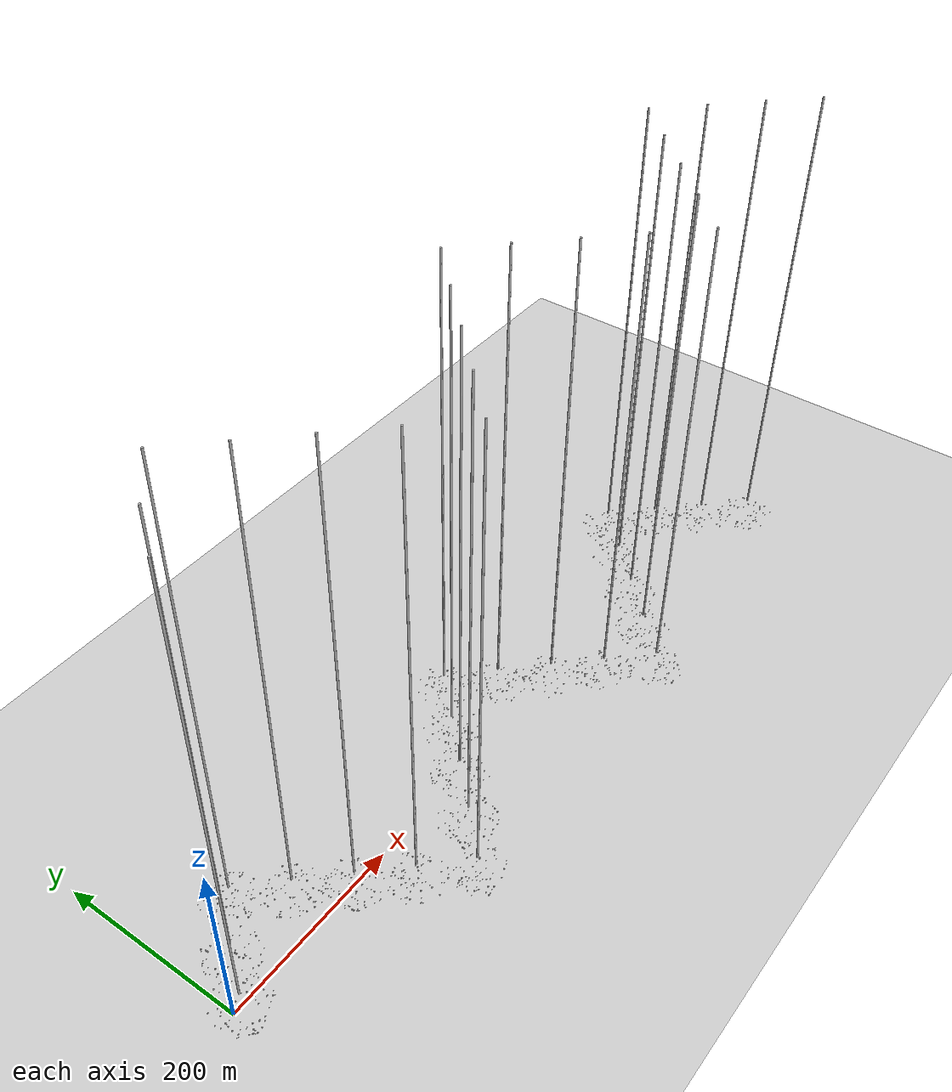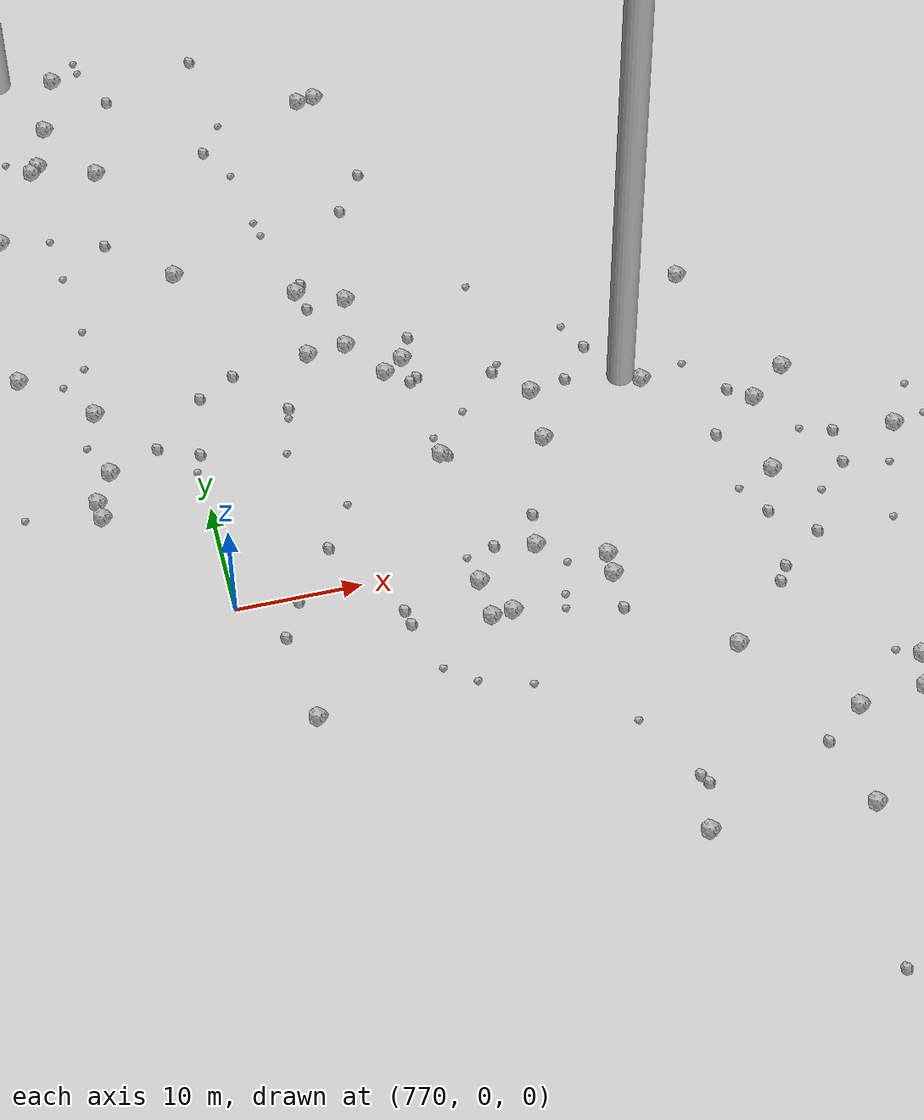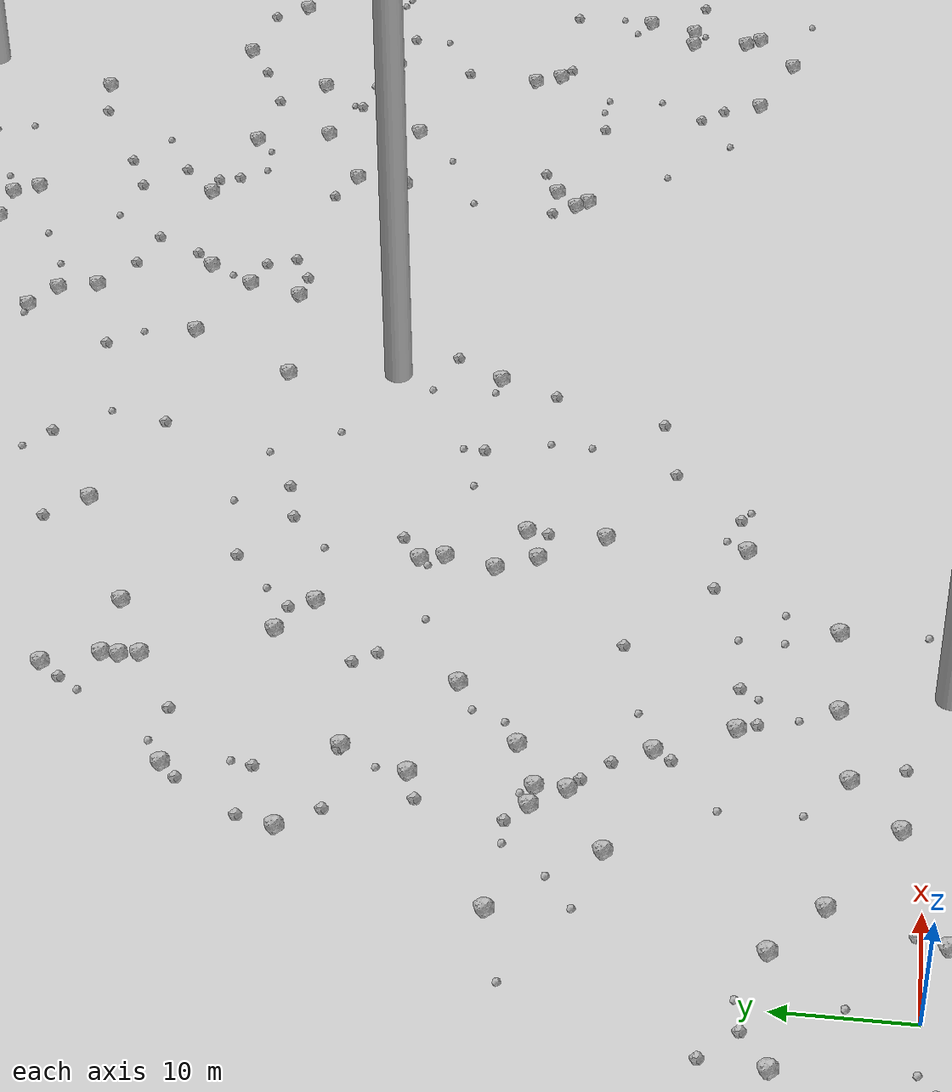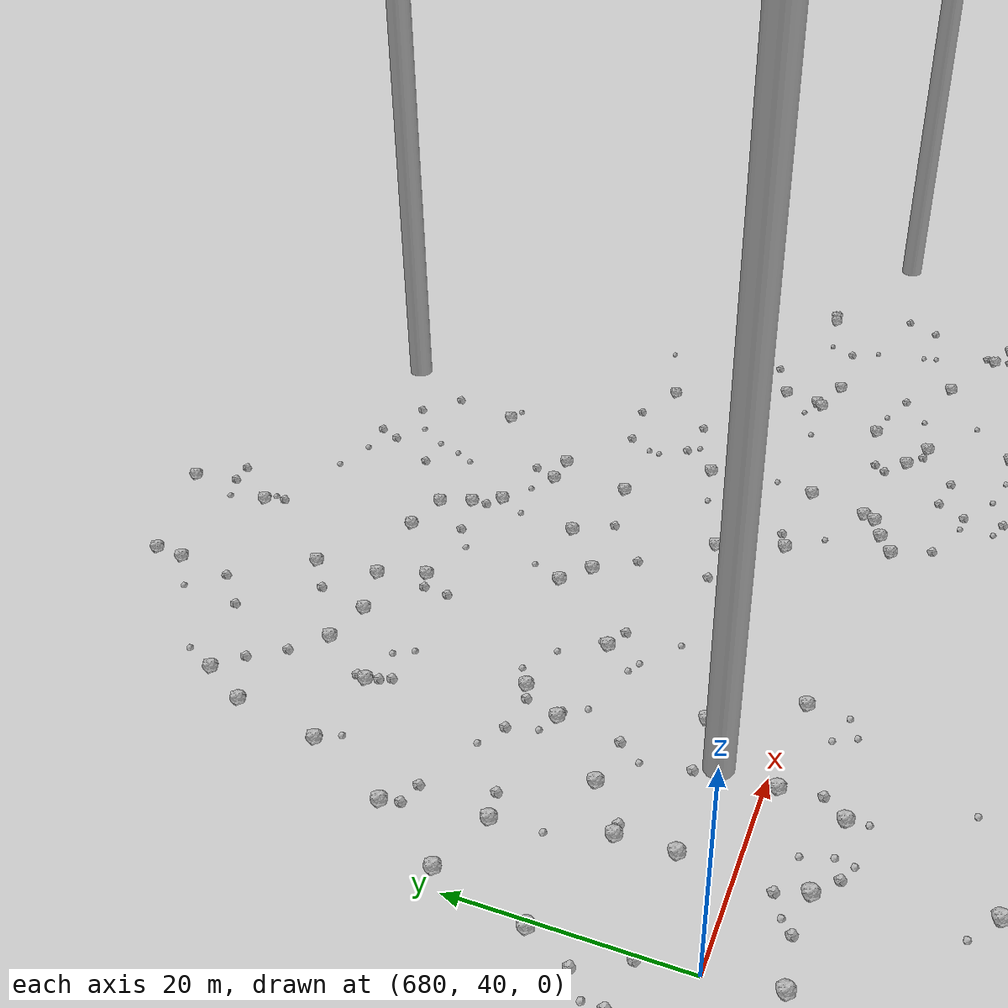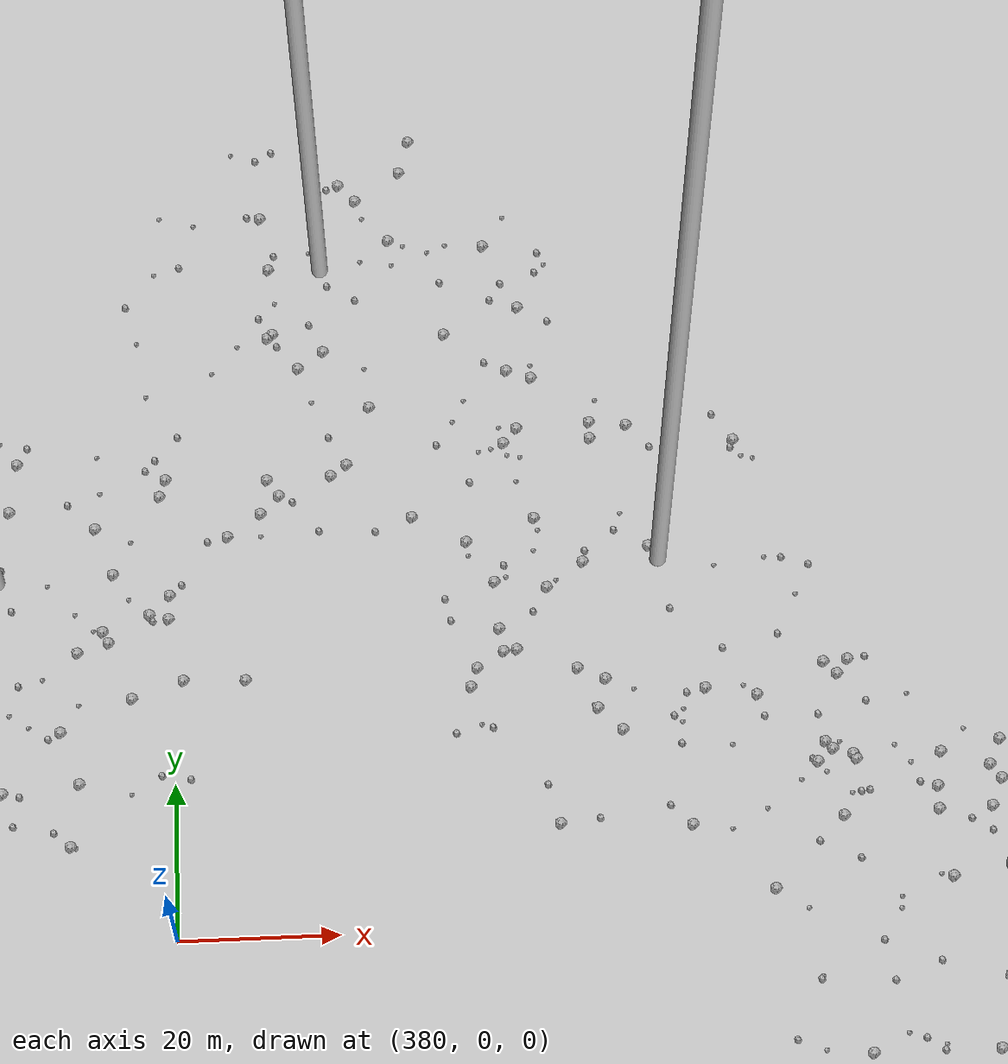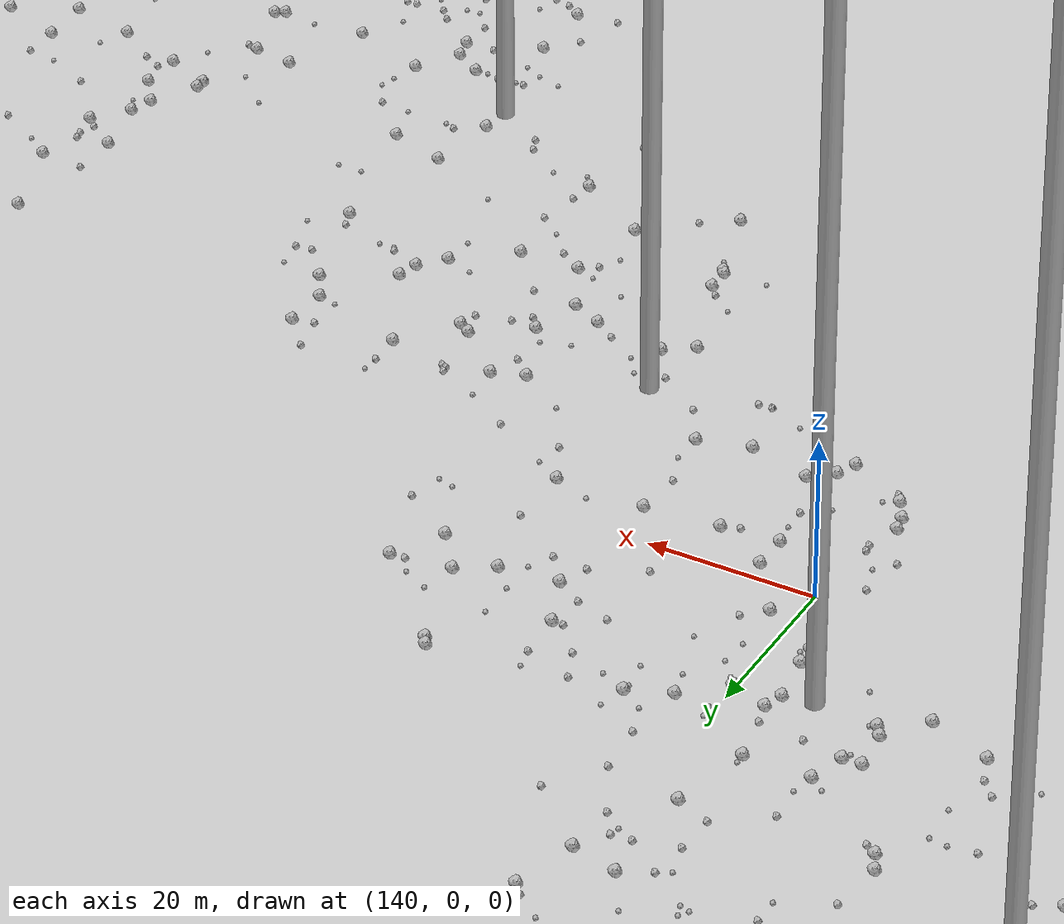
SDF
<sdf version="1.6">
 <world name="default">
  <include><uri>model://custom_ground</uri></include>
  <include><uri>model://sun</uri></include>
  <spherical_coordinates>
   <surface_model>EARTH_WGS84</surface_model>
   <latitude_deg>38.161479</latitude_deg>
   <longitude_deg>-122.454630</longitude_deg>
   <elevation>488.0</elevation>
   <heading_deg>90</heading_deg>
  </spherical_coordinates>
  <model name="rock1_0_0">
   <include><uri>model://rock1</uri><pose>-11.503411078473125 -9.660300492870213 0.5 0 0 0</pose></include>
  </model>
  <model name="rock1_0_1">
   <include><uri>model://rock1</uri><pose>6.808349927093094 -1.7704275221813823 0.5 0 0 0</pose></include>
  </model>
  <model name="rock1_0_2">
   <include><uri>model://rock1</uri><pose>-10.134170801342757 -0.4737587298295587 0.5 0 0 0</pose></include>
  </model>
  <model name="rock1_0_3">
   <include><uri>model://rock1</uri><pose>17.401818476116453 1.543593528536956 0.5 0 0 0</pose></include>
  </model>
  <model name="rock1_0_4">
   <include><uri>model://rock1</uri><pose>3.5994806406390687 -18.9408677183257 0.5 0 0 0</pose></include>
  </model>
  <model name="rock1_0_5">
   <include><uri>model://rock1</uri><pose>6.677490581675897 29.695834067963858 0.5 0 0 0</pose></include>
  </model>
  <model name="rock1_0_6">
   <include><uri>model://rock1</uri><pose>9.474659829688278 6.565295986912531 0.5 0 0 0</pose></include>
  </model>
  <model name="rock1_0_7">
   <include><uri>model://rock1</uri><pose>0.3806872126282492 -28.086174527003447 0.5 0 0 0</pose></include>
  </model>
  <model name="rock1_0_8">
   <include><uri>model://rock1</uri><pose>-12.239818995272461 17.769852893372594 0.5 0 0 0</pose></include>
  </model>
  <model name="rock1_0_9">
   <include><uri>model://rock1</uri><pose>5.008054746975777 10.317719458864111 0.5 0 0 0</pose></include>
  </model>
  <model name="rock1_0_10">
   <include><uri>model://rock1</uri><pose>21.9578537041507 5.310865710735911 0.5 0 0 0</pose></include>
  </model>
  <model name="rock1_0_11">
   <include><uri>model://rock1</uri><pose>5.983462245148534 -27.553769954747914 0.5 0 0 0</pose></include>
  </model>
  <model name="rock1_0_12">
   <include><uri>model://rock1</uri><pose>31.984097426111923 -5.098819459210745 0.5 0 0 0</pose></include>
  </model>
  <model name="rock1_0_13">
   <include><uri>model://rock1</uri><pose>23.454351879285824 19.47904448850656 0.5 0 0 0</pose></include>
  </model>
  <model name="rock1_0_14">
   <include><uri>model://rock1</uri><pose>13.03617988805356 22.158231088864447 0.5 0 0 0</pose></include>
  </model>
  <model name="rock1_0_15">
   <include><uri>model://rock1</uri><pose>29.124516692812108 6.280925601246665 0.5 0 0 0</pose></include>
  </model>
  <model name="rock1_0_16">
   <include><uri>model://rock1</uri><pose>-10.62726112887405 -4.4197847797269745 0.5 0 0 0</pose></include>
  </model>
  <model name="rock1_0_17">
   <include><uri>model://rock1</uri><pose>0.15618251322850085 -22.95410317538272 0.5 0 0 0</pose></include>
  </model>
  <model name="rock1_0_18">
   <include><uri>model://rock1</uri><pose>8.774329427639827 -21.936178321890896 0.5 0 0 0</pose></include>
  </model>
  <model name="rock1_0_19">
   <include><uri>model://rock1</uri><pose>-2.373637926613636 -25.588514092489792 0.5 0 0 0</pose></include>
  </model>
  <model name="rock1_0_20">
   <include><uri>model://rock1</uri><pose>-10.829205733613982 -16.27119311059975 0.5 0 0 0</pose></include>
  </model>
  <model name="rock1_0_21">
   <include><uri>model://rock1</uri><pose>-5.08818100552007 9.76590193204099 0.5 0 0 0</pose></include>
  </model>
  <model name="rock1_0_22">
   <include><uri>model://rock1</uri><pose>32.77220983545316 -15.253588261637447 0.5 0 0 0</pose></include>
  </model>
  <model name="rock1_0_23">
   <include><uri>model://rock1</uri><pose>37.663647092061204 6.499365665041921 0.5 0 0 0</pose></include>
  </model>
  <model name="rock1_0_24">
   <include><uri>model://rock1</uri><pose>14.789605048984896 -22.777207140836314 0.5 0 0 0</pose></include>
  </model>
  <model name="rock1_0_25">
   <include><uri>model://rock1</uri><pose>19.57527410946119 -10.459441940534056 0.5 0 0 0</pose></include>
  </model>
  <model name="rock1_0_26">
   <include><uri>model://rock1</uri><pose>29.857244306953632 -11.345402981057585 0.5 0 0 0</pose></include>
  </model>
  <model name="rock2_0_0">
   <include><uri>model://rock2</uri><pose>7.506592603519117 0.3789382166240145 0.3 0 0 0</pose></include>
  </model>
  <model name="rock2_0_1">
   <include><uri>model://rock2</uri><pose>-1.3073763337491648 -9.467474156459247 0.3 0 0 0</pose></include>
  </model>
  <model name="rock2_0_2">
   <include><uri>model://rock2</uri><pose>11.574661464621709 -25.25878786911317 0.3 0 0 0</pose></include>
  </model>
  <model name="rock2_0_3">
   <include><uri>model://rock2</uri><pose>-15.474965974398323 -0.6377787677178688 0.3 0 0 0</pose></include>
  </model>
  <model name="rock2_0_4">
   <include><uri>model://rock2</uri><pose>36.80788637197735 -12.299611934888066 0.3 0 0 0</pose></include>
  </model>
  <model name="rock2_0_5">
   <include><uri>model://rock2</uri><pose>-2.1293451896396967 11.793655478348136 0.3 0 0 0</pose></include>
  </model>
  <model name="rock2_0_6">
   <include><uri>model://rock2</uri><pose>15.148885677630915 29.355349583254032 0.3 0 0 0</pose></include>
  </model>
  <model name="rock2_0_7">
   <include><uri>model://rock2</uri><pose>-4.709841804030148 14.391380273555193 0.3 0 0 0</pose></include>
  </model>
  <model name="rock2_0_8">
   <include><uri>model://rock2</uri><pose>-5.213226914021675 -23.292225696776327 0.3 0 0 0</pose></include>
  </model>
  <model name="rock2_0_9">
   <include><uri>model://rock2</uri><pose>26.932148505989055 12.139084874442446 0.3 0 0 0</pose></include>
  </model>
  <model name="rock2_0_10">
   <include><uri>model://rock2</uri><pose>10.160772608531254 -21.01878023422382 0.3 0 0 0</pose></include>
  </model>
  <model name="rock2_0_11">
   <include><uri>model://rock2</uri><pose>-10.10794693248496 -1.85438342412915 0.3 0 0 0</pose></include>
  </model>
  <model name="rock2_0_12">
   <include><uri>model://rock2</uri><pose>-6.402508650600485 -14.419589471392309 0.3 0 0 0</pose></include>
  </model>
  <model name="rock2_0_13">
   <include><uri>model://rock2</uri><pose>-17.017426957287235 5.3815782254709745 0.3 0 0 0</pose></include>
  </model>
  <model name="rock2_0_14">
   <include><uri>model://rock2</uri><pose>32.09095685511008 -4.413528821215959 0.3 0 0 0</pose></include>
  </model>
  <model name="rock2_0_15">
   <include><uri>model://rock2</uri><pose>-13.819009661945172 -17.09812893178816 0.3 0 0 0</pose></include>
  </model>
  <model name="rock2_0_16">
   <include><uri>model://rock2</uri><pose>23.458522960821988 1.2799180067881046 0.3 0 0 0</pose></include>
  </model>
  <model name="rock2_0_17">
   <include><uri>model://rock2</uri><pose>22.49868650994523 18.119978991949694 0.3 0 0 0</pose></include>
  </model>
  <model name="rock2_0_18">
   <include><uri>model://rock2</uri><pose>22.828435195400147 -19.96755013961594 0.3 0 0 0</pose></include>
  </model>
  <model name="rock2_0_19">
   <include><uri>model://rock2</uri><pose>-3.1056618990476856 -24.839360749465882 0.3 0 0 0</pose></include>
  </model>
  <model name="rock2_0_20">
   <include><uri>model://rock2</uri><pose>21.296962061469102 -6.0602880825055365 0.3 0 0 0</pose></include>
  </model>
  <model name="rock2_0_21">
   <include><uri>model://rock2</uri><pose>30.654215134548714 13.616436668726308 0.3 0 0 0</pose></include>
  </model>
  <model name="rock2_0_22">
   <include><uri>model://rock2</uri><pose>-1.1668534136644872 -17.371006051542214 0.3 0 0 0</pose></include>
  </model>
  <model name="rock2_0_23">
   <include><uri>model://rock2</uri><pose>-6.162815046459876 -0.9952128229895436 0.3 0 0 0</pose></include>
  </model>
  <model name="rock2_0_24">
   <include><uri>model://rock2</uri><pose>-8.046582216253086 7.375637597247888 0.3 0 0 0</pose></include>
  </model>
  <model name="rock2_0_25">
   <include><uri>model://rock2</uri><pose>21.82583405031025 22.370557802401187 0.3 0 0 0</pose></include>
  </model>
  <model name="rock2_0_26">
   <include><uri>model://rock2</uri><pose>-1.6056949748204659 -27.221956590350786 0.3 0 0 0</pose></include>
  </model>
  <model name="rock3_0_0">
   <include><uri>model://rock3</uri><pose>34.470726801782305 -16.437246407982627 0.2 0 0 0</pose></include>
  </model>
  <model name="rock3_0_1">
   <include><uri>model://rock3</uri><pose>-10.980638690125762 -15.6598244857679 0.2 0 0 0</pose></include>
  </model>
  <model name="rock3_0_2">
   <include><uri>model://rock3</uri><pose>17.902852508132256 14.470614232793196 0.2 0 0 0</pose></include>
  </model>
  <model name="rock3_0_3">
   <include><uri>model://rock3</uri><pose>-2.972319277470014 -17.699764294786107 0.2 0 0 0</pose></include>
  </model>
  <model name="rock3_0_4">
   <include><uri>model://rock3</uri><pose>-4.423579276449026 0.12311385302733768 0.2 0 0 0</pose></include>
  </model>
  <model name="rock3_0_5">
   <include><uri>model://rock3</uri><pose>-12.424084793233735 -17.811882213629545 0.2 0 0 0</pose></include>
  </model>
  <model name="rock3_0_6">
   <include><uri>model://rock3</uri><pose>29.016789925448343 -11.337628120696394 0.2 0 0 0</pose></include>
  </model>
  <model name="rock3_0_7">
   <include><uri>model://rock3</uri><pose>0.08573101645805181 -24.243018043543874 0.2 0 0 0</pose></include>
  </model>
  <model name="rock3_0_8">
   <include><uri>model://rock3</uri><pose>0.3796125201164031 -25.163173117195466 0.2 0 0 0</pose></include>
  </model>
  <model name="rock3_0_9">
   <include><uri>model://rock3</uri><pose>0.6067639971124414 12.24506692824297 0.2 0 0 0</pose></include>
  </model>
  <model name="rock3_0_10">
   <include><uri>model://rock3</uri><pose>-1.5354512920490464 -27.284853155469584 0.2 0 0 0</pose></include>
  </model>
  <model name="rock3_0_11">
   <include><uri>model://rock3</uri><pose>19.306863367335943 -25.542468194768706 0.2 0 0 0</pose></include>
  </model>
  <model name="rock3_0_12">
   <include><uri>model://rock3</uri><pose>32.42602514787719 -16.562854043391873 0.2 0 0 0</pose></include>
  </model>
  <model name="rock3_0_13">
   <include><uri>model://rock3</uri><pose>22.743887284939852 -3.1388545490114623 0.2 0 0 0</pose></include>
  </model>
  <model name="rock3_0_14">
   <include><uri>model://rock3</uri><pose>29.73918971054303 12.157767661677887 0.2 0 0 0</pose></include>
  </model>
  <model name="rock3_0_15">
   <include><uri>model://rock3</uri><pose>37.53803378950139 -3.566510321975379 0.2 0 0 0</pose></include>
  </model>
  <model name="rock3_0_16">
   <include><uri>model://rock3</uri><pose>0.29286847239961133 28.045547376521228 0.2 0 0 0</pose></include>
  </model>
  <model name="rock3_0_17">
   <include><uri>model://rock3</uri><pose>37.959668049075205 -0.2747411294695574 0.2 0 0 0</pose></include>
  </model>
  <model name="rock3_0_18">
   <include><uri>model://rock3</uri><pose>27.79824937924952 9.10217722344737 0.2 0 0 0</pose></include>
  </model>
  <model name="rock3_0_19">
   <include><uri>model://rock3</uri><pose>36.093688250655866 10.51580675617798 0.2 0 0 0</pose></include>
  </model>
  <model name="rock3_0_20">
   <include><uri>model://rock3</uri><pose>36.36002269180527 -11.967524491704303 0.2 0 0 0</pose></include>
  </model>
  <model name="rock3_0_21">
   <include><uri>model://rock3</uri><pose>7.430602331220271 23.782892976666837 0.2 0 0 0</pose></include>
  </model>
  <model name="rock3_0_22">
   <include><uri>model://rock3</uri><pose>18.114867054613967 8.393563600190248 0.2 0 0 0</pose></include>
  </model>
  <model name="rock3_0_23">
   <include><uri>model://rock3</uri><pose>10.24323265187029 25.87463859093269 0.2 0 0 0</pose></include>
  </model>
  <model name="rock3_0_24">
   <include><uri>model://rock3</uri><pose>30.05705710012235 -13.630353307926658 0.2 0 0 0</pose></include>
  </model>
  <model name="rock3_0_25">
   <include><uri>model://rock3</uri><pose>27.879021536054324 -17.38446357654453 0.2 0 0 0</pose></include>
  </model>
  <model name="rock3_0_26">
   <include><uri>model://rock3</uri><pose>0.6463341015446815 4.929650174626879 0.2 0 0 0</pose></include>
  </model>
  <model name="rock1_1_0">
   <include><uri>model://rock1</uri><pose>18.787552891962633 25.23421930920893 0.5 0 0 0</pose></include>
  </model>
  <model name="rock1_1_1">
   <include><uri>model://rock1</uri><pose>43.14469769429502 37.311337300206056 0.5 0 0 0</pose></include>
  </model>
  <model name="rock1_1_2">
   <include><uri>model://rock1</uri><pose>28.999553777762145 60.06811305657012 0.5 0 0 0</pose></include>
  </model>
  <model name="rock1_1_3">
   <include><uri>model://rock1</uri><pose>21.301040212206793 41.98839558815839 0.5 0 0 0</pose></include>
  </model>
  <model name="rock1_1_4">
   <include><uri>model://rock1</uri><pose>26.321725601563276 13.620188611779655 0.5 0 0 0</pose></include>
  </model>
  <model name="rock1_1_5">
   <include><uri>model://rock1</uri><pose>46.789034189961725 25.039684753112795 0.5 0 0 0</pose></include>
  </model>
  <model name="rock1_1_6">
   <include><uri>model://rock1</uri><pose>35.02595496144026 61.22189947312864 0.5 0 0 0</pose></include>
  </model>
  <model name="rock1_1_7">
   <include><uri>model://rock1</uri><pose>28.90437869177163 34.40016002450952 0.5 0 0 0</pose></include>
  </model>
  <model name="rock1_1_8">
   <include><uri>model://rock1</uri><pose>22.934697403670725 29.303302089645324 0.5 0 0 0</pose></include>
  </model>
  <model name="rock1_1_9">
   <include><uri>model://rock1</uri><pose>46.84745832238529 31.28587583025769 0.5 0 0 0</pose></include>
  </model>
  <model name="rock1_1_10">
   <include><uri>model://rock1</uri><pose>36.72791677232151 46.43232295049448 0.5 0 0 0</pose></include>
  </model>
  <model name="rock1_1_11">
   <include><uri>model://rock1</uri><pose>29.011447010276072 61.40265718024332 0.5 0 0 0</pose></include>
  </model>
  <model name="rock1_1_12">
   <include><uri>model://rock1</uri><pose>18.041659902069334 54.56972984229456 0.5 0 0 0</pose></include>
  </model>
  <model name="rock1_1_13">
   <include><uri>model://rock1</uri><pose>33.16255629119774 48.96653213693583 0.5 0 0 0</pose></include>
  </model>
  <model name="rock1_1_14">
   <include><uri>model://rock1</uri><pose>29.275315552382565 58.53073378839553 0.5 0 0 0</pose></include>
  </model>
  <model name="rock1_1_15">
   <include><uri>model://rock1</uri><pose>66.27602130904485 35.652885414885006 0.5 0 0 0</pose></include>
  </model>
  <model name="rock1_1_16">
   <include><uri>model://rock1</uri><pose>42.612891188348584 39.24206946085769 0.5 0 0 0</pose></include>
  </model>
  <model name="rock1_1_17">
   <include><uri>model://rock1</uri><pose>27.491606782651118 65.69480561122298 0.5 0 0 0</pose></include>
  </model>
  <model name="rock1_1_18">
   <include><uri>model://rock1</uri><pose>18.80358948359204 27.61631546172059 0.5 0 0 0</pose></include>
  </model>
  <model name="rock1_1_19">
   <include><uri>model://rock1</uri><pose>46.44661516251625 13.962932336339575 0.5 0 0 0</pose></include>
  </model>
  <model name="rock1_1_20">
   <include><uri>model://rock1</uri><pose>16.896292341719192 27.797227797017186 0.5 0 0 0</pose></include>
  </model>
  <model name="rock1_1_21">
   <include><uri>model://rock1</uri><pose>42.19095567041761 33.26875705040425 0.5 0 0 0</pose></include>
  </model>
  <model name="rock1_1_22">
   <include><uri>model://rock1</uri><pose>65.05611040866737 53.51664447538225 0.5 0 0 0</pose></include>
  </model>
  <model name="rock1_1_23">
   <include><uri>model://rock1</uri><pose>19.134379594071476 36.78232397177692 0.5 0 0 0</pose></include>
  </model>
  <model name="rock1_1_24">
   <include><uri>model://rock1</uri><pose>43.74964599447217 30.091715690923266 0.5 0 0 0</pose></include>
  </model>
  <model name="rock1_1_25">
   <include><uri>model://rock1</uri><pose>46.943003926473736 66.45245534552991 0.5 0 0 0</pose></include>
  </model>
  <model name="rock1_1_26">
   <include><uri>model://rock1</uri><pose>12.747677609124628 45.30031278595702 0.5 0 0 0</pose></include>
  </model>
  <model name="rock2_1_0">
   <include><uri>model://rock2</uri><pose>34.380022282520635 22.575011937119832 0.3 0 0 0</pose></include>
  </model>
  <model name="rock2_1_1">
   <include><uri>model://rock2</uri><pose>46.454466345883496 49.82865826867751 0.3 0 0 0</pose></include>
  </model>
  <model name="rock2_1_2">
   <include><uri>model://rock2</uri><pose>41.307931542018 53.40621399671563 0.3 0 0 0</pose></include>
  </model>
  <model name="rock2_1_3">
   <include><uri>model://rock2</uri><pose>18.45877638336841 47.92831642073247 0.3 0 0 0</pose></include>
  </model>
  <model name="rock2_1_4">
   <include><uri>model://rock2</uri><pose>16.654694169544975 53.23704458714332 0.3 0 0 0</pose></include>
  </model>
  <model name="rock2_1_5">
   <include><uri>model://rock2</uri><pose>30.20608382755414 42.587855381223385 0.3 0 0 0</pose></include>
  </model>
  <model name="rock2_1_6">
   <include><uri>model://rock2</uri><pose>16.523064285230845 35.92522641997493 0.3 0 0 0</pose></include>
  </model>
  <model name="rock2_1_7">
   <include><uri>model://rock2</uri><pose>23.679149986635522 55.15538391370181 0.3 0 0 0</pose></include>
  </model>
  <model name="rock2_1_8">
   <include><uri>model://rock2</uri><pose>14.79231444607347 42.2840170217921 0.3 0 0 0</pose></include>
  </model>
  <model name="rock2_1_9">
   <include><uri>model://rock2</uri><pose>46.63703073414267 29.583708929904095 0.3 0 0 0</pose></include>
  </model>
  <model name="rock2_1_10">
   <include><uri>model://rock2</uri><pose>61.584716131132254 21.585464635358644 0.3 0 0 0</pose></include>
  </model>
  <model name="rock2_1_11">
   <include><uri>model://rock2</uri><pose>13.483469319135423 48.22656887566896 0.3 0 0 0</pose></include>
  </model>
  <model name="rock2_1_12">
   <include><uri>model://rock2</uri><pose>26.03845955722356 64.0066555005615 0.3 0 0 0</pose></include>
  </model>
  <model name="rock2_1_13">
   <include><uri>model://rock2</uri><pose>55.23015359116821 20.12516247255823 0.3 0 0 0</pose></include>
  </model>
  <model name="rock2_1_14">
   <include><uri>model://rock2</uri><pose>50.08735763155609 14.61972251865804 0.3 0 0 0</pose></include>
  </model>
  <model name="rock2_1_15">
   <include><uri>model://rock2</uri><pose>19.846983963353317 24.420585924353368 0.3 0 0 0</pose></include>
  </model>
  <model name="rock2_1_16">
   <include><uri>model://rock2</uri><pose>56.59545985731047 35.87581793419909 0.3 0 0 0</pose></include>
  </model>
  <model name="rock2_1_17">
   <include><uri>model://rock2</uri><pose>31.40392688063805 40.82532443414647 0.3 0 0 0</pose></include>
  </model>
  <model name="rock2_1_18">
   <include><uri>model://rock2</uri><pose>57.275725902462796 62.444130535081236 0.3 0 0 0</pose></include>
  </model>
  <model name="rock2_1_19">
   <include><uri>model://rock2</uri><pose>35.77995965424316 48.40182983217055 0.3 0 0 0</pose></include>
  </model>
  <model name="rock2_1_20">
   <include><uri>model://rock2</uri><pose>64.38605064698461 30.808564531330035 0.3 0 0 0</pose></include>
  </model>
  <model name="rock2_1_21">
   <include><uri>model://rock2</uri><pose>44.8952506648655 40.80020090072591 0.3 0 0 0</pose></include>
  </model>
  <model name="rock2_1_22">
   <include><uri>model://rock2</uri><pose>20.905534283890965 42.0923972733045 0.3 0 0 0</pose></include>
  </model>
  <model name="rock2_1_23">
   <include><uri>model://rock2</uri><pose>41.71337441089001 16.243346899056206 0.3 0 0 0</pose></include>
  </model>
  <model name="rock2_1_24">
   <include><uri>model://rock2</uri><pose>68.79295144687404 39.58255975277878 0.3 0 0 0</pose></include>
  </model>
  <model name="rock2_1_25">
   <include><uri>model://rock2</uri><pose>50.160562407187555 50.76404867416536 0.3 0 0 0</pose></include>
  </model>
  <model name="rock2_1_26">
   <include><uri>model://rock2</uri><pose>44.31731940492294 69.6055898977171 0.3 0 0 0</pose></include>
  </model>
  <model name="rock3_1_0">
   <include><uri>model://rock3</uri><pose>56.72911711524133 37.60545897407638 0.2 0 0 0</pose></include>
  </model>
  <model name="rock3_1_1">
   <include><uri>model://rock3</uri><pose>51.22195852323731 13.871265968124378 0.2 0 0 0</pose></include>
  </model>
  <model name="rock3_1_2">
   <include><uri>model://rock3</uri><pose>26.18684182970862 32.98694845584553 0.2 0 0 0</pose></include>
  </model>
  <model name="rock3_1_3">
   <include><uri>model://rock3</uri><pose>58.12425368359015 30.57404542218741 0.2 0 0 0</pose></include>
  </model>
  <model name="rock3_1_4">
   <include><uri>model://rock3</uri><pose>52.08181531965278 36.16733772028788 0.2 0 0 0</pose></include>
  </model>
  <model name="rock3_1_5">
   <include><uri>model://rock3</uri><pose>12.989702754605633 29.226099813956115 0.2 0 0 0</pose></include>
  </model>
  <model name="rock3_1_6">
   <include><uri>model://rock3</uri><pose>57.73500146896973 47.825327314863785 0.2 0 0 0</pose></include>
  </model>
  <model name="rock3_1_7">
   <include><uri>model://rock3</uri><pose>57.99804763339502 27.189795439622703 0.2 0 0 0</pose></include>
  </model>
  <model name="rock3_1_8">
   <include><uri>model://rock3</uri><pose>20.2220108612349 55.935844374251744 0.2 0 0 0</pose></include>
  </model>
  <model name="rock3_1_9">
   <include><uri>model://rock3</uri><pose>27.102928295930486 13.400372270446821 0.2 0 0 0</pose></include>
  </model>
  <model name="rock3_1_10">
   <include><uri>model://rock3</uri><pose>37.85072617294412 50.41353864392954 0.2 0 0 0</pose></include>
  </model>
  <model name="rock3_1_11">
   <include><uri>model://rock3</uri><pose>25.173233726804384 30.434940963882624 0.2 0 0 0</pose></include>
  </model>
  <model name="rock3_1_12">
   <include><uri>model://rock3</uri><pose>41.9703623419624 38.494416632327614 0.2 0 0 0</pose></include>
  </model>
  <model name="rock3_1_13">
   <include><uri>model://rock3</uri><pose>54.479101584261535 53.1786467954256 0.2 0 0 0</pose></include>
  </model>
  <model name="rock3_1_14">
   <include><uri>model://rock3</uri><pose>39.307563814310285 10.591107132321563 0.2 0 0 0</pose></include>
  </model>
  <model name="rock3_1_15">
   <include><uri>model://rock3</uri><pose>64.30048566153346 41.15280727415501 0.2 0 0 0</pose></include>
  </model>
  <model name="rock3_1_16">
   <include><uri>model://rock3</uri><pose>19.42695198298565 39.12272656682979 0.2 0 0 0</pose></include>
  </model>
  <model name="rock3_1_17">
   <include><uri>model://rock3</uri><pose>47.99390446106952 54.922016885053694 0.2 0 0 0</pose></include>
  </model>
  <model name="rock3_1_18">
   <include><uri>model://rock3</uri><pose>18.05124232447504 28.526454173910178 0.2 0 0 0</pose></include>
  </model>
  <model name="rock3_1_19">
   <include><uri>model://rock3</uri><pose>36.075770569266886 14.014829910211198 0.2 0 0 0</pose></include>
  </model>
  <model name="rock3_1_20">
   <include><uri>model://rock3</uri><pose>27.2358627959896 20.834438533311097 0.2 0 0 0</pose></include>
  </model>
  <model name="rock3_1_21">
   <include><uri>model://rock3</uri><pose>47.56342737634745 15.577588951934487 0.2 0 0 0</pose></include>
  </model>
  <model name="rock3_1_22">
   <include><uri>model://rock3</uri><pose>35.68022443924055 37.76759217819281 0.2 0 0 0</pose></include>
  </model>
  <model name="rock3_1_23">
   <include><uri>model://rock3</uri><pose>18.865217757836433 49.569270461199075 0.2 0 0 0</pose></include>
  </model>
  <model name="rock3_1_24">
   <include><uri>model://rock3</uri><pose>64.46845689679279 35.90952942472367 0.2 0 0 0</pose></include>
  </model>
  <model name="rock3_1_25">
   <include><uri>model://rock3</uri><pose>24.89842198916366 62.28867833576421 0.2 0 0 0</pose></include>
  </model>
  <model name="rock3_1_26">
   <include><uri>model://rock3</uri><pose>43.08320767656974 46.784844509434954 0.2 0 0 0</pose></include>
  </model>
  <model name="rock1_2_0">
   <include><uri>model://rock1</uri><pose>77.57138792685092 59.11054170348594 0.5 0 0 0</pose></include>
  </model>
  <model name="rock1_2_1">
   <include><uri>model://rock1</uri><pose>55.07176618686532 84.0017508753928 0.5 0 0 0</pose></include>
  </model>
  <model name="rock1_2_2">
   <include><uri>model://rock1</uri><pose>81.75976190290017 91.86062792325137 0.5 0 0 0</pose></include>
  </model>
  <model name="rock1_2_3">
   <include><uri>model://rock1</uri><pose>76.28877381677943 54.59392432467031 0.5 0 0 0</pose></include>
  </model>
  <model name="rock1_2_4">
   <include><uri>model://rock1</uri><pose>69.73966105655705 86.38311039744394 0.5 0 0 0</pose></include>
  </model>
  <model name="rock1_2_5">
   <include><uri>model://rock1</uri><pose>86.52011299087783 95.88299920368902 0.5 0 0 0</pose></include>
  </model>
  <model name="rock1_2_6">
   <include><uri>model://rock1</uri><pose>88.62024539892394 107.5216350090508 0.5 0 0 0</pose></include>
  </model>
  <model name="rock1_2_7">
   <include><uri>model://rock1</uri><pose>89.30366811192653 83.2770971503339 0.5 0 0 0</pose></include>
  </model>
  <model name="rock1_2_8">
   <include><uri>model://rock1</uri><pose>75.84157507560546 72.37312656279153 0.5 0 0 0</pose></include>
  </model>
  <model name="rock1_2_9">
   <include><uri>model://rock1</uri><pose>72.17696060259522 77.68540968199126 0.5 0 0 0</pose></include>
  </model>
  <model name="rock1_2_10">
   <include><uri>model://rock1</uri><pose>85.32840032862387 83.56901012752492 0.5 0 0 0</pose></include>
  </model>
  <model name="rock1_2_11">
   <include><uri>model://rock1</uri><pose>74.32375119959684 106.34097589887375 0.5 0 0 0</pose></include>
  </model>
  <model name="rock1_2_12">
   <include><uri>model://rock1</uri><pose>100.5599649525576 62.73325406190371 0.5 0 0 0</pose></include>
  </model>
  <model name="rock1_2_13">
   <include><uri>model://rock1</uri><pose>105.20700477783846 89.90658114721094 0.5 0 0 0</pose></include>
  </model>
  <model name="rock1_2_14">
   <include><uri>model://rock1</uri><pose>93.0717894937511 90.26510728648884 0.5 0 0 0</pose></include>
  </model>
  <model name="rock1_2_15">
   <include><uri>model://rock1</uri><pose>79.86585485771286 63.00486680847088 0.5 0 0 0</pose></include>
  </model>
  <model name="rock1_2_16">
   <include><uri>model://rock1</uri><pose>102.78089022198708 90.10339122581848 0.5 0 0 0</pose></include>
  </model>
  <model name="rock1_2_17">
   <include><uri>model://rock1</uri><pose>70.17739341260366 62.49953205500888 0.5 0 0 0</pose></include>
  </model>
  <model name="rock1_2_18">
   <include><uri>model://rock1</uri><pose>92.27485216334915 105.1687014576604 0.5 0 0 0</pose></include>
  </model>
  <model name="rock1_2_19">
   <include><uri>model://rock1</uri><pose>69.16496375377656 107.79549055215693 0.5 0 0 0</pose></include>
  </model>
  <model name="rock1_2_20">
   <include><uri>model://rock1</uri><pose>73.69323839062514 93.49387580045206 0.5 0 0 0</pose></include>
  </model>
  <model name="rock1_2_21">
   <include><uri>model://rock1</uri><pose>91.32851295892647 65.27544531387727 0.5 0 0 0</pose></include>
  </model>
  <model name="rock1_2_22">
   <include><uri>model://rock1</uri><pose>50.38102476144625 76.18794926896373 0.5 0 0 0</pose></include>
  </model>
  <model name="rock1_2_23">
   <include><uri>model://rock1</uri><pose>90.45885365210076 81.12476580461524 0.5 0 0 0</pose></include>
  </model>
  <model name="rock1_2_24">
   <include><uri>model://rock1</uri><pose>108.39320606468833 78.51711080450347 0.5 0 0 0</pose></include>
  </model>
  <model name="rock1_2_25">
   <include><uri>model://rock1</uri><pose>74.99790731501702 75.67839602264482 0.5 0 0 0</pose></include>
  </model>
  <model name="rock1_2_26">
   <include><uri>model://rock1</uri><pose>100.13318174797996 100.40169002148596 0.5 0 0 0</pose></include>
  </model>
  <model name="rock2_2_0">
   <include><uri>model://rock2</uri><pose>77.67926370765406 109.34905389932293 0.3 0 0 0</pose></include>
  </model>
  <model name="rock2_2_1">
   <include><uri>model://rock2</uri><pose>81.57454252439564 64.56726822811235 0.3 0 0 0</pose></include>
  </model>
  <model name="rock2_2_2">
   <include><uri>model://rock2</uri><pose>92.99917251271049 100.24979093627101 0.3 0 0 0</pose></include>
  </model>
  <model name="rock2_2_3">
   <include><uri>model://rock2</uri><pose>76.17853019381457 107.93878113444137 0.3 0 0 0</pose></include>
  </model>
  <model name="rock2_2_4">
   <include><uri>model://rock2</uri><pose>83.65754230493184 68.46553235157818 0.3 0 0 0</pose></include>
  </model>
  <model name="rock2_2_5">
   <include><uri>model://rock2</uri><pose>103.86595312799471 77.76365840318488 0.3 0 0 0</pose></include>
  </model>
  <model name="rock2_2_6">
   <include><uri>model://rock2</uri><pose>91.75646067817055 71.77923085307764 0.3 0 0 0</pose></include>
  </model>
  <model name="rock2_2_7">
   <include><uri>model://rock2</uri><pose>67.4822490889376 69.71949893036553 0.3 0 0 0</pose></include>
  </model>
  <model name="rock2_2_8">
   <include><uri>model://rock2</uri><pose>84.52832525253737 99.38532428943074 0.3 0 0 0</pose></include>
  </model>
  <model name="rock2_2_9">
   <include><uri>model://rock2</uri><pose>102.38211672630625 97.77990936203958 0.3 0 0 0</pose></include>
  </model>
  <model name="rock2_2_10">
   <include><uri>model://rock2</uri><pose>77.95390625441786 83.60890949645604 0.3 0 0 0</pose></include>
  </model>
  <model name="rock2_2_11">
   <include><uri>model://rock2</uri><pose>55.065690479002605 71.39785916042416 0.3 0 0 0</pose></include>
  </model>
  <model name="rock2_2_12">
   <include><uri>model://rock2</uri><pose>91.97758770157279 54.01742365872379 0.3 0 0 0</pose></include>
  </model>
  <model name="rock2_2_13">
   <include><uri>model://rock2</uri><pose>62.97102017334675 81.0960711613126 0.3 0 0 0</pose></include>
  </model>
  <model name="rock2_2_14">
   <include><uri>model://rock2</uri><pose>93.98226164279542 63.17176071318926 0.3 0 0 0</pose></include>
  </model>
  <model name="rock2_2_15">
   <include><uri>model://rock2</uri><pose>94.73065097525327 68.2213890587748 0.3 0 0 0</pose></include>
  </model>
  <model name="rock2_2_16">
   <include><uri>model://rock2</uri><pose>52.70302546387834 77.01753265723585 0.3 0 0 0</pose></include>
  </model>
  <model name="rock2_2_17">
   <include><uri>model://rock2</uri><pose>93.42774784098151 65.00535419018628 0.3 0 0 0</pose></include>
  </model>
  <model name="rock2_2_18">
   <include><uri>model://rock2</uri><pose>79.53677662163564 69.7089964885472 0.3 0 0 0</pose></include>
  </model>
  <model name="rock2_2_19">
   <include><uri>model://rock2</uri><pose>78.93505666752108 54.272628597770414 0.3 0 0 0</pose></include>
  </model>
  <model name="rock2_2_20">
   <include><uri>model://rock2</uri><pose>81.62740586764917 55.73512614851506 0.3 0 0 0</pose></include>
  </model>
  <model name="rock2_2_21">
   <include><uri>model://rock2</uri><pose>95.69284257199085 73.5491302007951 0.3 0 0 0</pose></include>
  </model>
  <model name="rock2_2_22">
   <include><uri>model://rock2</uri><pose>56.77628562074009 80.52562767059277 0.3 0 0 0</pose></include>
  </model>
  <model name="rock2_2_23">
   <include><uri>model://rock2</uri><pose>72.71096838231321 90.7619102020157 0.3 0 0 0</pose></include>
  </model>
  <model name="rock2_2_24">
   <include><uri>model://rock2</uri><pose>57.970047886692896 99.37296134055902 0.3 0 0 0</pose></include>
  </model>
  <model name="rock2_2_25">
   <include><uri>model://rock2</uri><pose>80.61476149311517 58.205717779301835 0.3 0 0 0</pose></include>
  </model>
  <model name="rock2_2_26">
   <include><uri>model://rock2</uri><pose>68.7690838385751 103.23118362925837 0.3 0 0 0</pose></include>
  </model>
  <model name="rock3_2_0">
   <include><uri>model://rock3</uri><pose>99.71688875533279 87.39561313092952 0.2 0 0 0</pose></include>
  </model>
  <model name="rock3_2_1">
   <include><uri>model://rock3</uri><pose>64.48575214447432 87.54543263508529 0.2 0 0 0</pose></include>
  </model>
  <model name="rock3_2_2">
   <include><uri>model://rock3</uri><pose>84.88411099570112 84.21914299023103 0.2 0 0 0</pose></include>
  </model>
  <model name="rock3_2_3">
   <include><uri>model://rock3</uri><pose>52.92069077313698 73.41420462286045 0.2 0 0 0</pose></include>
  </model>
  <model name="rock3_2_4">
   <include><uri>model://rock3</uri><pose>85.81389931452277 106.12027419554494 0.2 0 0 0</pose></include>
  </model>
  <model name="rock3_2_5">
   <include><uri>model://rock3</uri><pose>105.53185234394573 93.5219123133933 0.2 0 0 0</pose></include>
  </model>
  <model name="rock3_2_6">
   <include><uri>model://rock3</uri><pose>55.4538775789977 94.4122557408454 0.2 0 0 0</pose></include>
  </model>
  <model name="rock3_2_7">
   <include><uri>model://rock3</uri><pose>53.92239349369368 92.13111691426678 0.2 0 0 0</pose></include>
  </model>
  <model name="rock3_2_8">
   <include><uri>model://rock3</uri><pose>84.01857738399525 109.36917246676288 0.2 0 0 0</pose></include>
  </model>
  <model name="rock3_2_9">
   <include><uri>model://rock3</uri><pose>78.68012908853177 76.35795320634102 0.2 0 0 0</pose></include>
  </model>
  <model name="rock3_2_10">
   <include><uri>model://rock3</uri><pose>99.71503852849955 70.76053854010297 0.2 0 0 0</pose></include>
  </model>
  <model name="rock3_2_11">
   <include><uri>model://rock3</uri><pose>98.80629402083594 61.121283749425515 0.2 0 0 0</pose></include>
  </model>
  <model name="rock3_2_12">
   <include><uri>model://rock3</uri><pose>97.70380318428411 99.66037870119231 0.2 0 0 0</pose></include>
  </model>
  <model name="rock3_2_13">
   <include><uri>model://rock3</uri><pose>107.30083784890752 91.22570258974625 0.2 0 0 0</pose></include>
  </model>
  <model name="rock3_2_14">
   <include><uri>model://rock3</uri><pose>100.62774544212773 84.06775896655597 0.2 0 0 0</pose></include>
  </model>
  <model name="rock3_2_15">
   <include><uri>model://rock3</uri><pose>69.59916420333796 66.86144898840993 0.2 0 0 0</pose></include>
  </model>
  <model name="rock3_2_16">
   <include><uri>model://rock3</uri><pose>71.1191502891424 77.79746273959941 0.2 0 0 0</pose></include>
  </model>
  <model name="rock3_2_17">
   <include><uri>model://rock3</uri><pose>64.60877926531887 82.64547544792046 0.2 0 0 0</pose></include>
  </model>
  <model name="rock3_2_18">
   <include><uri>model://rock3</uri><pose>64.38037679839917 98.71454232201242 0.2 0 0 0</pose></include>
  </model>
  <model name="rock3_2_19">
   <include><uri>model://rock3</uri><pose>78.7478636479796 60.87812654979129 0.2 0 0 0</pose></include>
  </model>
  <model name="rock3_2_20">
   <include><uri>model://rock3</uri><pose>83.24889590699559 78.55995831750937 0.2 0 0 0</pose></include>
  </model>
  <model name="rock3_2_21">
   <include><uri>model://rock3</uri><pose>86.8089107997904 72.83023264568226 0.2 0 0 0</pose></include>
  </model>
  <model name="rock3_2_22">
   <include><uri>model://rock3</uri><pose>92.00570971360844 84.2853718287256 0.2 0 0 0</pose></include>
  </model>
  <model name="rock3_2_23">
   <include><uri>model://rock3</uri><pose>95.62326905822508 60.9217624688992 0.2 0 0 0</pose></include>
  </model>
  <model name="rock3_2_24">
   <include><uri>model://rock3</uri><pose>80.2770322629903 100.44188172631462 0.2 0 0 0</pose></include>
  </model>
  <model name="rock3_2_25">
   <include><uri>model://rock3</uri><pose>95.38718548577486 95.10002437267994 0.2 0 0 0</pose></include>
  </model>
  <model name="rock3_2_26">
   <include><uri>model://rock3</uri><pose>58.32630465894847 67.14725010325924 0.2 0 0 0</pose></include>
  </model>
  <model name="rock1_3_0">
   <include><uri>model://rock1</uri><pose>111.95075633100917 16.42692880231396 0.5 0 0 0</pose></include>
  </model>
  <model name="rock1_3_1">
   <include><uri>model://rock1</uri><pose>135.75688330910225 19.613256308872312 0.5 0 0 0</pose></include>
  </model>
  <model name="rock1_3_2">
   <include><uri>model://rock1</uri><pose>93.76628560712119 31.05786270440236 0.5 0 0 0</pose></include>
  </model>
  <model name="rock1_3_3">
   <include><uri>model://rock1</uri><pose>124.88500315439785 23.55118545364231 0.5 0 0 0</pose></include>
  </model>
  <model name="rock1_3_4">
   <include><uri>model://rock1</uri><pose>134.31900539377085 66.30500554315523 0.5 0 0 0</pose></include>
  </model>
  <model name="rock1_3_5">
   <include><uri>model://rock1</uri><pose>119.51580484238356 13.616418870552751 0.5 0 0 0</pose></include>
  </model>
  <model name="rock1_3_6">
   <include><uri>model://rock1</uri><pose>122.63053495631631 23.46056524399045 0.5 0 0 0</pose></include>
  </model>
  <model name="rock1_3_7">
   <include><uri>model://rock1</uri><pose>94.98038905930038 33.98123762663779 0.5 0 0 0</pose></include>
  </model>
  <model name="rock1_3_8">
   <include><uri>model://rock1</uri><pose>133.91261241929283 27.975974412789608 0.5 0 0 0</pose></include>
  </model>
  <model name="rock1_3_9">
   <include><uri>model://rock1</uri><pose>102.28785052841162 56.27443472829684 0.5 0 0 0</pose></include>
  </model>
  <model name="rock1_3_10">
   <include><uri>model://rock1</uri><pose>136.20399462063955 50.745206971955994 0.5 0 0 0</pose></include>
  </model>
  <model name="rock1_3_11">
   <include><uri>model://rock1</uri><pose>113.86316120224109 38.02948318470274 0.5 0 0 0</pose></include>
  </model>
  <model name="rock1_3_12">
   <include><uri>model://rock1</uri><pose>92.9232662299213 32.09812586149239 0.5 0 0 0</pose></include>
  </model>
  <model name="rock1_3_13">
   <include><uri>model://rock1</uri><pose>126.11388348319976 27.875889000377704 0.5 0 0 0</pose></include>
  </model>
  <model name="rock1_3_14">
   <include><uri>model://rock1</uri><pose>125.12498236523774 62.1560875794906 0.5 0 0 0</pose></include>
  </model>
  <model name="rock1_3_15">
   <include><uri>model://rock1</uri><pose>136.17019966896024 37.59773327759045 0.5 0 0 0</pose></include>
  </model>
  <model name="rock1_3_16">
   <include><uri>model://rock1</uri><pose>141.81968315555906 49.29199200614768 0.5 0 0 0</pose></include>
  </model>
  <model name="rock1_3_17">
   <include><uri>model://rock1</uri><pose>143.9105114358072 57.086607446632044 0.5 0 0 0</pose></include>
  </model>
  <model name="rock1_3_18">
   <include><uri>model://rock1</uri><pose>110.72689153255746 57.95073188711346 0.5 0 0 0</pose></include>
  </model>
  <model name="rock1_3_19">
   <include><uri>model://rock1</uri><pose>123.19754237390794 18.380839097179315 0.5 0 0 0</pose></include>
  </model>
  <model name="rock1_3_20">
   <include><uri>model://rock1</uri><pose>114.97424370220564 35.72636616014622 0.5 0 0 0</pose></include>
  </model>
  <model name="rock1_3_21">
   <include><uri>model://rock1</uri><pose>103.62334911772874 47.894902412998704 0.5 0 0 0</pose></include>
  </model>
  <model name="rock1_3_22">
   <include><uri>model://rock1</uri><pose>94.6652267330803 48.015297810835875 0.5 0 0 0</pose></include>
  </model>
  <model name="rock1_3_23">
   <include><uri>model://rock1</uri><pose>124.13247768037246 17.01937913910774 0.5 0 0 0</pose></include>
  </model>
  <model name="rock1_3_24">
   <include><uri>model://rock1</uri><pose>135.01326460569356 17.23437332981332 0.5 0 0 0</pose></include>
  </model>
  <model name="rock1_3_25">
   <include><uri>model://rock1</uri><pose>95.31960230074102 52.44189837746188 0.5 0 0 0</pose></include>
  </model>
  <model name="rock1_3_26">
   <include><uri>model://rock1</uri><pose>116.24732838059991 66.18607063216021 0.5 0 0 0</pose></include>
  </model>
  <model name="rock2_3_0">
   <include><uri>model://rock2</uri><pose>142.69393396429007 58.382615908034396 0.3 0 0 0</pose></include>
  </model>
  <model name="rock2_3_1">
   <include><uri>model://rock2</uri><pose>149.31350028433963 42.277170404852605 0.3 0 0 0</pose></include>
  </model>
  <model name="rock2_3_2">
   <include><uri>model://rock2</uri><pose>108.81431659552658 21.74590325076975 0.3 0 0 0</pose></include>
  </model>
  <model name="rock2_3_3">
   <include><uri>model://rock2</uri><pose>126.28061655001856 35.06241462702083 0.3 0 0 0</pose></include>
  </model>
  <model name="rock2_3_4">
   <include><uri>model://rock2</uri><pose>139.44114035013715 45.740469729137885 0.3 0 0 0</pose></include>
  </model>
  <model name="rock2_3_5">
   <include><uri>model://rock2</uri><pose>123.09069347406069 64.98631402215582 0.3 0 0 0</pose></include>
  </model>
  <model name="rock2_3_6">
   <include><uri>model://rock2</uri><pose>107.50140369448863 61.86479623227401 0.3 0 0 0</pose></include>
  </model>
  <model name="rock2_3_7">
   <include><uri>model://rock2</uri><pose>131.97520284523796 39.20605659835981 0.3 0 0 0</pose></include>
  </model>
  <model name="rock2_3_8">
   <include><uri>model://rock2</uri><pose>116.33726517276068 34.760355292635566 0.3 0 0 0</pose></include>
  </model>
  <model name="rock2_3_9">
   <include><uri>model://rock2</uri><pose>91.54750919132972 34.08892895414729 0.3 0 0 0</pose></include>
  </model>
  <model name="rock2_3_10">
   <include><uri>model://rock2</uri><pose>114.61812336885762 44.503835356795975 0.3 0 0 0</pose></include>
  </model>
  <model name="rock2_3_11">
   <include><uri>model://rock2</uri><pose>120.30179953846188 50.595093965179736 0.3 0 0 0</pose></include>
  </model>
  <model name="rock2_3_12">
   <include><uri>model://rock2</uri><pose>112.54028318072517 64.00541865653413 0.3 0 0 0</pose></include>
  </model>
  <model name="rock2_3_13">
   <include><uri>model://rock2</uri><pose>135.0231344724967 22.191007779559918 0.3 0 0 0</pose></include>
  </model>
  <model name="rock2_3_14">
   <include><uri>model://rock2</uri><pose>132.16516731906955 44.16800587345244 0.3 0 0 0</pose></include>
  </model>
  <model name="rock2_3_15">
   <include><uri>model://rock2</uri><pose>145.5165336053267 29.919129823234442 0.3 0 0 0</pose></include>
  </model>
  <model name="rock2_3_16">
   <include><uri>model://rock2</uri><pose>115.80670808944168 51.38689635979385 0.3 0 0 0</pose></include>
  </model>
  <model name="rock2_3_17">
   <include><uri>model://rock2</uri><pose>129.65531837543827 22.733241669862963 0.3 0 0 0</pose></include>
  </model>
  <model name="rock2_3_18">
   <include><uri>model://rock2</uri><pose>132.66706456976812 48.89064933004207 0.3 0 0 0</pose></include>
  </model>
  <model name="rock2_3_19">
   <include><uri>model://rock2</uri><pose>141.4310617734492 42.760063044356414 0.3 0 0 0</pose></include>
  </model>
  <model name="rock2_3_20">
   <include><uri>model://rock2</uri><pose>144.94017096745347 36.17123878561344 0.3 0 0 0</pose></include>
  </model>
  <model name="rock2_3_21">
   <include><uri>model://rock2</uri><pose>137.06784027719854 45.5244126477515 0.3 0 0 0</pose></include>
  </model>
  <model name="rock2_3_22">
   <include><uri>model://rock2</uri><pose>110.61856947707564 19.74876319832311 0.3 0 0 0</pose></include>
  </model>
  <model name="rock2_3_23">
   <include><uri>model://rock2</uri><pose>97.86057745326976 35.2939230269056 0.3 0 0 0</pose></include>
  </model>
  <model name="rock2_3_24">
   <include><uri>model://rock2</uri><pose>131.49266984819587 60.697258450386514 0.3 0 0 0</pose></include>
  </model>
  <model name="rock2_3_25">
   <include><uri>model://rock2</uri><pose>106.06206810095107 30.60780920929853 0.3 0 0 0</pose></include>
  </model>
  <model name="rock2_3_26">
   <include><uri>model://rock2</uri><pose>107.42343232869402 53.9133273680251 0.3 0 0 0</pose></include>
  </model>
  <model name="rock3_3_0">
   <include><uri>model://rock3</uri><pose>107.67521376716323 54.63449652100896 0.2 0 0 0</pose></include>
  </model>
  <model name="rock3_3_1">
   <include><uri>model://rock3</uri><pose>109.2787981180007 30.94388104943586 0.2 0 0 0</pose></include>
  </model>
  <model name="rock3_3_2">
   <include><uri>model://rock3</uri><pose>131.89703702654182 58.47731707150055 0.2 0 0 0</pose></include>
  </model>
  <model name="rock3_3_3">
   <include><uri>model://rock3</uri><pose>120.33146748042266 47.253940682443414 0.2 0 0 0</pose></include>
  </model>
  <model name="rock3_3_4">
   <include><uri>model://rock3</uri><pose>92.48308005939766 41.32796881541126 0.2 0 0 0</pose></include>
  </model>
  <model name="rock3_3_5">
   <include><uri>model://rock3</uri><pose>124.36696954143093 22.39243080468346 0.2 0 0 0</pose></include>
  </model>
  <model name="rock3_3_6">
   <include><uri>model://rock3</uri><pose>127.41663074559894 12.02033658822363 0.2 0 0 0</pose></include>
  </model>
  <model name="rock3_3_7">
   <include><uri>model://rock3</uri><pose>111.48073912854206 53.33036146062221 0.2 0 0 0</pose></include>
  </model>
  <model name="rock3_3_8">
   <include><uri>model://rock3</uri><pose>104.65021596281446 18.779002431659706 0.2 0 0 0</pose></include>
  </model>
  <model name="rock3_3_9">
   <include><uri>model://rock3</uri><pose>111.37307259181328 30.65568486344715 0.2 0 0 0</pose></include>
  </model>
  <model name="rock3_3_10">
   <include><uri>model://rock3</uri><pose>128.05837940410444 52.101998590084314 0.2 0 0 0</pose></include>
  </model>
  <model name="rock3_3_11">
   <include><uri>model://rock3</uri><pose>131.18370397389782 47.897864151333046 0.2 0 0 0</pose></include>
  </model>
  <model name="rock3_3_12">
   <include><uri>model://rock3</uri><pose>140.7793835267036 22.239939044975735 0.2 0 0 0</pose></include>
  </model>
  <model name="rock3_3_13">
   <include><uri>model://rock3</uri><pose>139.59740498718844 60.65359333271115 0.2 0 0 0</pose></include>
  </model>
  <model name="rock3_3_14">
   <include><uri>model://rock3</uri><pose>98.760318535873 24.171925789632645 0.2 0 0 0</pose></include>
  </model>
  <model name="rock3_3_15">
   <include><uri>model://rock3</uri><pose>140.49885402635172 23.899640915349114 0.2 0 0 0</pose></include>
  </model>
  <model name="rock3_3_16">
   <include><uri>model://rock3</uri><pose>127.56427857105331 53.540861976742065 0.2 0 0 0</pose></include>
  </model>
  <model name="rock3_3_17">
   <include><uri>model://rock3</uri><pose>126.8635190296024 52.490921671134856 0.2 0 0 0</pose></include>
  </model>
  <model name="rock3_3_18">
   <include><uri>model://rock3</uri><pose>139.19693921247034 44.40645025572377 0.2 0 0 0</pose></include>
  </model>
  <model name="rock3_3_19">
   <include><uri>model://rock3</uri><pose>124.24250193581983 29.069555369764654 0.2 0 0 0</pose></include>
  </model>
  <model name="rock3_3_20">
   <include><uri>model://rock3</uri><pose>124.8739786712157 17.188249223981188 0.2 0 0 0</pose></include>
  </model>
  <model name="rock3_3_21">
   <include><uri>model://rock3</uri><pose>99.2145806145997 44.16199325760235 0.2 0 0 0</pose></include>
  </model>
  <model name="rock3_3_22">
   <include><uri>model://rock3</uri><pose>111.69442548521972 25.656845526513305 0.2 0 0 0</pose></include>
  </model>
  <model name="rock3_3_23">
   <include><uri>model://rock3</uri><pose>133.86432490119242 29.080492423479324 0.2 0 0 0</pose></include>
  </model>
  <model name="rock3_3_24">
   <include><uri>model://rock3</uri><pose>132.98351531084649 55.76104133061774 0.2 0 0 0</pose></include>
  </model>
  <model name="rock3_3_25">
   <include><uri>model://rock3</uri><pose>123.34906910389535 17.832327081394624 0.2 0 0 0</pose></include>
  </model>
  <model name="rock3_3_26">
   <include><uri>model://rock3</uri><pose>126.68208874345868 30.52623319291911 0.2 0 0 0</pose></include>
  </model>
  <model name="rock1_4_0">
   <include><uri>model://rock1</uri><pose>148.09606873275436 -20.941046944501323 0.5 0 0 0</pose></include>
  </model>
  <model name="rock1_4_1">
   <include><uri>model://rock1</uri><pose>175.76934464038203 14.439776242397869 0.5 0 0 0</pose></include>
  </model>
  <model name="rock1_4_2">
   <include><uri>model://rock1</uri><pose>147.7224261701025 -2.2297733673685336 0.5 0 0 0</pose></include>
  </model>
  <model name="rock1_4_3">
   <include><uri>model://rock1</uri><pose>164.61304550795126 11.04770894212529 0.5 0 0 0</pose></include>
  </model>
  <model name="rock1_4_4">
   <include><uri>model://rock1</uri><pose>147.03829152832333 -23.38984754523529 0.5 0 0 0</pose></include>
  </model>
  <model name="rock1_4_5">
   <include><uri>model://rock1</uri><pose>138.2307622237045 -16.896039935437976 0.5 0 0 0</pose></include>
  </model>
  <model name="rock1_4_6">
   <include><uri>model://rock1</uri><pose>154.50725624465935 -6.070314438077187 0.5 0 0 0</pose></include>
  </model>
  <model name="rock1_4_7">
   <include><uri>model://rock1</uri><pose>142.90952169209166 4.700583778614224 0.5 0 0 0</pose></include>
  </model>
  <model name="rock1_4_8">
   <include><uri>model://rock1</uri><pose>171.6411876749701 11.898643131105132 0.5 0 0 0</pose></include>
  </model>
  <model name="rock1_4_9">
   <include><uri>model://rock1</uri><pose>149.77039038682304 24.270211237793653 0.5 0 0 0</pose></include>
  </model>
  <model name="rock1_4_10">
   <include><uri>model://rock1</uri><pose>139.75100983587893 -19.486433066346144 0.5 0 0 0</pose></include>
  </model>
  <model name="rock1_4_11">
   <include><uri>model://rock1</uri><pose>182.8721927128612 15.407626858667463 0.5 0 0 0</pose></include>
  </model>
  <model name="rock1_4_12">
   <include><uri>model://rock1</uri><pose>161.97920397444392 17.490138116673336 0.5 0 0 0</pose></include>
  </model>
  <model name="rock1_4_13">
   <include><uri>model://rock1</uri><pose>147.68676336685954 -6.75486438762346 0.5 0 0 0</pose></include>
  </model>
  <model name="rock1_4_14">
   <include><uri>model://rock1</uri><pose>164.44908413134738 -19.103818024946456 0.5 0 0 0</pose></include>
  </model>
  <model name="rock1_4_15">
   <include><uri>model://rock1</uri><pose>136.11216026496842 8.672598508917176 0.5 0 0 0</pose></include>
  </model>
  <model name="rock1_4_16">
   <include><uri>model://rock1</uri><pose>158.33228013390516 -20.812996693186655 0.5 0 0 0</pose></include>
  </model>
  <model name="rock1_4_17">
   <include><uri>model://rock1</uri><pose>174.13934007661985 -5.3205125699804725 0.5 0 0 0</pose></include>
  </model>
  <model name="rock1_4_18">
   <include><uri>model://rock1</uri><pose>172.17783570038932 26.350269929800533 0.5 0 0 0</pose></include>
  </model>
  <model name="rock1_4_19">
   <include><uri>model://rock1</uri><pose>150.71858421228853 -18.71610211237482 0.5 0 0 0</pose></include>
  </model>
  <model name="rock1_4_20">
   <include><uri>model://rock1</uri><pose>171.50398697080394 27.430445662760576 0.5 0 0 0</pose></include>
  </model>
  <model name="rock1_4_21">
   <include><uri>model://rock1</uri><pose>140.27507973030052 18.04349745505798 0.5 0 0 0</pose></include>
  </model>
  <model name="rock1_4_22">
   <include><uri>model://rock1</uri><pose>135.94875231601276 11.235731662892277 0.5 0 0 0</pose></include>
  </model>
  <model name="rock1_4_23">
   <include><uri>model://rock1</uri><pose>179.52905715396435 9.445029290232661 0.5 0 0 0</pose></include>
  </model>
  <model name="rock1_4_24">
   <include><uri>model://rock1</uri><pose>144.837846307878 22.23055322699173 0.5 0 0 0</pose></include>
  </model>
  <model name="rock1_4_25">
   <include><uri>model://rock1</uri><pose>137.79833512621738 -14.858172081430673 0.5 0 0 0</pose></include>
  </model>
  <model name="rock1_4_26">
   <include><uri>model://rock1</uri><pose>163.42589335631914 -5.263296445026711 0.5 0 0 0</pose></include>
  </model>
  <model name="rock2_4_0">
   <include><uri>model://rock2</uri><pose>162.9554420642417 -11.17009836789859 0.3 0 0 0</pose></include>
  </model>
  <model name="rock2_4_1">
   <include><uri>model://rock2</uri><pose>134.91666179185108 -9.193151981828908 0.3 0 0 0</pose></include>
  </model>
  <model name="rock2_4_2">
   <include><uri>model://rock2</uri><pose>161.24693212742673 13.069410459797332 0.3 0 0 0</pose></include>
  </model>
  <model name="rock2_4_3">
   <include><uri>model://rock2</uri><pose>159.96747194811425 -28.657091943860735 0.3 0 0 0</pose></include>
  </model>
  <model name="rock2_4_4">
   <include><uri>model://rock2</uri><pose>138.88386497806036 -9.777426357752692 0.3 0 0 0</pose></include>
  </model>
  <model name="rock2_4_5">
   <include><uri>model://rock2</uri><pose>181.09235579825838 15.20299326159337 0.3 0 0 0</pose></include>
  </model>
  <model name="rock2_4_6">
   <include><uri>model://rock2</uri><pose>157.19506074265433 4.6874559013309 0.3 0 0 0</pose></include>
  </model>
  <model name="rock2_4_7">
   <include><uri>model://rock2</uri><pose>157.3944931205748 21.211113029324878 0.3 0 0 0</pose></include>
  </model>
  <model name="rock2_4_8">
   <include><uri>model://rock2</uri><pose>145.2812655523105 6.950697375317645 0.3 0 0 0</pose></include>
  </model>
  <model name="rock2_4_9">
   <include><uri>model://rock2</uri><pose>186.2138090664964 4.959432157765761 0.3 0 0 0</pose></include>
  </model>
  <model name="rock2_4_10">
   <include><uri>model://rock2</uri><pose>161.5855067530617 23.19405250660958 0.3 0 0 0</pose></include>
  </model>
  <model name="rock2_4_11">
   <include><uri>model://rock2</uri><pose>160.6176818048054 17.431095394624116 0.3 0 0 0</pose></include>
  </model>
  <model name="rock2_4_12">
   <include><uri>model://rock2</uri><pose>152.44953038641978 -6.908509982873163 0.3 0 0 0</pose></include>
  </model>
  <model name="rock2_4_13">
   <include><uri>model://rock2</uri><pose>155.77803133173757 25.077668936403718 0.3 0 0 0</pose></include>
  </model>
  <model name="rock2_4_14">
   <include><uri>model://rock2</uri><pose>157.02194604827895 14.402243974229265 0.3 0 0 0</pose></include>
  </model>
  <model name="rock2_4_15">
   <include><uri>model://rock2</uri><pose>148.19689439310426 -12.521902260031581 0.3 0 0 0</pose></include>
  </model>
  <model name="rock2_4_16">
   <include><uri>model://rock2</uri><pose>167.3849703869364 -24.111556716979763 0.3 0 0 0</pose></include>
  </model>
  <model name="rock2_4_17">
   <include><uri>model://rock2</uri><pose>176.7597586569116 -10.658325858394246 0.3 0 0 0</pose></include>
  </model>
  <model name="rock2_4_18">
   <include><uri>model://rock2</uri><pose>163.20493820622355 7.607683892473091 0.3 0 0 0</pose></include>
  </model>
  <model name="rock2_4_19">
   <include><uri>model://rock2</uri><pose>174.19933794719276 2.444014641251812 0.3 0 0 0</pose></include>
  </model>
  <model name="rock2_4_20">
   <include><uri>model://rock2</uri><pose>159.9547432800787 -28.69454292187455 0.3 0 0 0</pose></include>
  </model>
  <model name="rock2_4_21">
   <include><uri>model://rock2</uri><pose>161.58161447920088 -28.544338473003698 0.3 0 0 0</pose></include>
  </model>
  <model name="rock2_4_22">
   <include><uri>model://rock2</uri><pose>140.4587096761689 -20.682221665617647 0.3 0 0 0</pose></include>
  </model>
  <model name="rock2_4_23">
   <include><uri>model://rock2</uri><pose>135.6780511225148 -3.489398288272124 0.3 0 0 0</pose></include>
  </model>
  <model name="rock2_4_24">
   <include><uri>model://rock2</uri><pose>139.03969549464497 -10.85063214842052 0.3 0 0 0</pose></include>
  </model>
  <model name="rock2_4_25">
   <include><uri>model://rock2</uri><pose>167.424637640761 7.339378832580607 0.3 0 0 0</pose></include>
  </model>
  <model name="rock2_4_26">
   <include><uri>model://rock2</uri><pose>184.51929684856725 -11.408559648074473 0.3 0 0 0</pose></include>
  </model>
  <model name="rock3_4_0">
   <include><uri>model://rock3</uri><pose>147.75364483838462 12.400109397166126 0.2 0 0 0</pose></include>
  </model>
  <model name="rock3_4_1">
   <include><uri>model://rock3</uri><pose>146.88855854097267 26.023706753696345 0.2 0 0 0</pose></include>
  </model>
  <model name="rock3_4_2">
   <include><uri>model://rock3</uri><pose>141.40635956097086 -18.768018634134794 0.2 0 0 0</pose></include>
  </model>
  <model name="rock3_4_3">
   <include><uri>model://rock3</uri><pose>177.34104585287022 -7.3573903803777405 0.2 0 0 0</pose></include>
  </model>
  <model name="rock3_4_4">
   <include><uri>model://rock3</uri><pose>136.8053766231342 -7.22549866626294 0.2 0 0 0</pose></include>
  </model>
  <model name="rock3_4_5">
   <include><uri>model://rock3</uri><pose>141.10455575083233 16.777560946135374 0.2 0 0 0</pose></include>
  </model>
  <model name="rock3_4_6">
   <include><uri>model://rock3</uri><pose>168.911723281734 10.059359131439521 0.2 0 0 0</pose></include>
  </model>
  <model name="rock3_4_7">
   <include><uri>model://rock3</uri><pose>136.83630809035304 9.415731345525046 0.2 0 0 0</pose></include>
  </model>
  <model name="rock3_4_8">
   <include><uri>model://rock3</uri><pose>176.6698865669875 18.624425123132923 0.2 0 0 0</pose></include>
  </model>
  <model name="rock3_4_9">
   <include><uri>model://rock3</uri><pose>169.59794188240372 -3.84189419592596 0.2 0 0 0</pose></include>
  </model>
  <model name="rock3_4_10">
   <include><uri>model://rock3</uri><pose>145.68320338518575 18.72923536327542 0.2 0 0 0</pose></include>
  </model>
  <model name="rock3_4_11">
   <include><uri>model://rock3</uri><pose>148.14072047913106 -9.712065902944218 0.2 0 0 0</pose></include>
  </model>
  <model name="rock3_4_12">
   <include><uri>model://rock3</uri><pose>150.1752885780997 19.59315936447331 0.2 0 0 0</pose></include>
  </model>
  <model name="rock3_4_13">
   <include><uri>model://rock3</uri><pose>164.5639071927842 -15.394766814917173 0.2 0 0 0</pose></include>
  </model>
  <model name="rock3_4_14">
   <include><uri>model://rock3</uri><pose>179.76985421626472 17.10730205224791 0.2 0 0 0</pose></include>
  </model>
  <model name="rock3_4_15">
   <include><uri>model://rock3</uri><pose>152.96440150127816 22.617945069275322 0.2 0 0 0</pose></include>
  </model>
  <model name="rock3_4_16">
   <include><uri>model://rock3</uri><pose>168.89160701417538 19.257896275257124 0.2 0 0 0</pose></include>
  </model>
  <model name="rock3_4_17">
   <include><uri>model://rock3</uri><pose>149.6421751552349 23.138678343151888 0.2 0 0 0</pose></include>
  </model>
  <model name="rock3_4_18">
   <include><uri>model://rock3</uri><pose>145.45194241425312 -14.813829153451266 0.2 0 0 0</pose></include>
  </model>
  <model name="rock3_4_19">
   <include><uri>model://rock3</uri><pose>185.23133985996697 0.6996713220055213 0.2 0 0 0</pose></include>
  </model>
  <model name="rock3_4_20">
   <include><uri>model://rock3</uri><pose>183.27883588223625 1.2703239933125303 0.2 0 0 0</pose></include>
  </model>
  <model name="rock3_4_21">
   <include><uri>model://rock3</uri><pose>142.6633666667685 11.091983077073053 0.2 0 0 0</pose></include>
  </model>
  <model name="rock3_4_22">
   <include><uri>model://rock3</uri><pose>155.5388008666758 -26.834558270496007 0.2 0 0 0</pose></include>
  </model>
  <model name="rock3_4_23">
   <include><uri>model://rock3</uri><pose>150.58935885546293 27.386281662072363 0.2 0 0 0</pose></include>
  </model>
  <model name="rock3_4_24">
   <include><uri>model://rock3</uri><pose>142.93469894901526 14.561081654490785 0.2 0 0 0</pose></include>
  </model>
  <model name="rock3_4_25">
   <include><uri>model://rock3</uri><pose>161.0702921160701 25.631356975746264 0.2 0 0 0</pose></include>
  </model>
  <model name="rock3_4_26">
   <include><uri>model://rock3</uri><pose>169.0012829548806 14.550507277878935 0.2 0 0 0</pose></include>
  </model>
  <model name="rock1_5_0">
   <include><uri>model://rock1</uri><pose>199.5515613021563 -42.46084772625758 0.5 0 0 0</pose></include>
  </model>
  <model name="rock1_5_1">
   <include><uri>model://rock1</uri><pose>198.20169111671632 -26.331346719776093 0.5 0 0 0</pose></include>
  </model>
  <model name="rock1_5_2">
   <include><uri>model://rock1</uri><pose>180.68140667007717 -60.48467334704439 0.5 0 0 0</pose></include>
  </model>
  <model name="rock1_5_3">
   <include><uri>model://rock1</uri><pose>196.6530485367917 -25.31865395718468 0.5 0 0 0</pose></include>
  </model>
  <model name="rock1_5_4">
   <include><uri>model://rock1</uri><pose>217.12989095513853 -27.06455181237076 0.5 0 0 0</pose></include>
  </model>
  <model name="rock1_5_5">
   <include><uri>model://rock1</uri><pose>186.68611453854797 -20.917840409979952 0.5 0 0 0</pose></include>
  </model>
  <model name="rock1_5_6">
   <include><uri>model://rock1</uri><pose>177.15531001404113 -46.861391468561344 0.5 0 0 0</pose></include>
  </model>
  <model name="rock1_5_7">
   <include><uri>model://rock1</uri><pose>172.76904532062306 -35.04734439205317 0.5 0 0 0</pose></include>
  </model>
  <model name="rock1_5_8">
   <include><uri>model://rock1</uri><pose>188.75322161439954 -35.92013088471884 0.5 0 0 0</pose></include>
  </model>
  <model name="rock1_5_9">
   <include><uri>model://rock1</uri><pose>208.63217382811115 -34.256672484134185 0.5 0 0 0</pose></include>
  </model>
  <model name="rock1_5_10">
   <include><uri>model://rock1</uri><pose>184.90790723810147 -34.07379541853231 0.5 0 0 0</pose></include>
  </model>
  <model name="rock1_5_11">
   <include><uri>model://rock1</uri><pose>176.07042956834132 -32.6797693238154 0.5 0 0 0</pose></include>
  </model>
  <model name="rock1_5_12">
   <include><uri>model://rock1</uri><pose>215.2299187571511 -17.933738129412625 0.5 0 0 0</pose></include>
  </model>
  <model name="rock1_5_13">
   <include><uri>model://rock1</uri><pose>217.79790428971936 -55.07788709397644 0.5 0 0 0</pose></include>
  </model>
  <model name="rock1_5_14">
   <include><uri>model://rock1</uri><pose>197.5173320205926 -68.8255262133683 0.5 0 0 0</pose></include>
  </model>
  <model name="rock1_5_15">
   <include><uri>model://rock1</uri><pose>220.7733007826073 -39.90148695618555 0.5 0 0 0</pose></include>
  </model>
  <model name="rock1_5_16">
   <include><uri>model://rock1</uri><pose>192.17736229035023 -42.65160734270566 0.5 0 0 0</pose></include>
  </model>
  <model name="rock1_5_17">
   <include><uri>model://rock1</uri><pose>177.5514938431552 -50.301657823633576 0.5 0 0 0</pose></include>
  </model>
  <model name="rock1_5_18">
   <include><uri>model://rock1</uri><pose>206.07290504771046 -37.18374982719343 0.5 0 0 0</pose></include>
  </model>
  <model name="rock1_5_19">
   <include><uri>model://rock1</uri><pose>209.28274629694812 -31.613919656617846 0.5 0 0 0</pose></include>
  </model>
  <model name="rock1_5_20">
   <include><uri>model://rock1</uri><pose>199.46031426442946 -58.42923982736671 0.5 0 0 0</pose></include>
  </model>
  <model name="rock1_5_21">
   <include><uri>model://rock1</uri><pose>214.9118452748072 -23.44199810799894 0.5 0 0 0</pose></include>
  </model>
  <model name="rock1_5_22">
   <include><uri>model://rock1</uri><pose>190.52820923088225 -19.547435204284703 0.5 0 0 0</pose></include>
  </model>
  <model name="rock1_5_23">
   <include><uri>model://rock1</uri><pose>190.35923568814 -52.76960798743355 0.5 0 0 0</pose></include>
  </model>
  <model name="rock1_5_24">
   <include><uri>model://rock1</uri><pose>190.40725369587776 -29.676793876811388 0.5 0 0 0</pose></include>
  </model>
  <model name="rock1_5_25">
   <include><uri>model://rock1</uri><pose>203.18471228211132 -19.741803309473617 0.5 0 0 0</pose></include>
  </model>
  <model name="rock1_5_26">
   <include><uri>model://rock1</uri><pose>177.24121768254196 -49.843791529000406 0.5 0 0 0</pose></include>
  </model>
  <model name="rock2_5_0">
   <include><uri>model://rock2</uri><pose>211.6785059406126 -14.049412040474067 0.3 0 0 0</pose></include>
  </model>
  <model name="rock2_5_1">
   <include><uri>model://rock2</uri><pose>219.59382002702543 -61.891183379153006 0.3 0 0 0</pose></include>
  </model>
  <model name="rock2_5_2">
   <include><uri>model://rock2</uri><pose>182.14401457013983 -32.28178124759449 0.3 0 0 0</pose></include>
  </model>
  <model name="rock2_5_3">
   <include><uri>model://rock2</uri><pose>195.11100244799192 -44.65834089566938 0.3 0 0 0</pose></include>
  </model>
  <model name="rock2_5_4">
   <include><uri>model://rock2</uri><pose>209.0774269047971 -62.395184055044425 0.3 0 0 0</pose></include>
  </model>
  <model name="rock2_5_5">
   <include><uri>model://rock2</uri><pose>195.21309050055865 -17.33655380297221 0.3 0 0 0</pose></include>
  </model>
  <model name="rock2_5_6">
   <include><uri>model://rock2</uri><pose>197.58473227799712 -28.680474043284825 0.3 0 0 0</pose></include>
  </model>
  <model name="rock2_5_7">
   <include><uri>model://rock2</uri><pose>184.62546054301492 -57.848820736257565 0.3 0 0 0</pose></include>
  </model>
  <model name="rock2_5_8">
   <include><uri>model://rock2</uri><pose>220.65776522862447 -31.3515214709384 0.3 0 0 0</pose></include>
  </model>
  <model name="rock2_5_9">
   <include><uri>model://rock2</uri><pose>175.96867900649775 -45.44791371427603 0.3 0 0 0</pose></include>
  </model>
  <model name="rock2_5_10">
   <include><uri>model://rock2</uri><pose>212.34806962105796 -35.7546442160938 0.3 0 0 0</pose></include>
  </model>
  <model name="rock2_5_11">
   <include><uri>model://rock2</uri><pose>189.1082337140997 -23.315171051766 0.3 0 0 0</pose></include>
  </model>
  <model name="rock2_5_12">
   <include><uri>model://rock2</uri><pose>194.32463503360222 -36.28020414475874 0.3 0 0 0</pose></include>
  </model>
  <model name="rock2_5_13">
   <include><uri>model://rock2</uri><pose>190.20695019745347 -44.151257601202786 0.3 0 0 0</pose></include>
  </model>
  <model name="rock2_5_14">
   <include><uri>model://rock2</uri><pose>202.96585297066255 -15.700213000279483 0.3 0 0 0</pose></include>
  </model>
  <model name="rock2_5_15">
   <include><uri>model://rock2</uri><pose>212.65420381008332 -18.579043231830184 0.3 0 0 0</pose></include>
  </model>
  <model name="rock2_5_16">
   <include><uri>model://rock2</uri><pose>209.89893873773136 -64.31821174898214 0.3 0 0 0</pose></include>
  </model>
  <model name="rock2_5_17">
   <include><uri>model://rock2</uri><pose>200.7436496836263 -50.16589643745169 0.3 0 0 0</pose></include>
  </model>
  <model name="rock2_5_18">
   <include><uri>model://rock2</uri><pose>195.95084781656507 -18.374439547747045 0.3 0 0 0</pose></include>
  </model>
  <model name="rock2_5_19">
   <include><uri>model://rock2</uri><pose>195.35868624636015 -18.093113608689087 0.3 0 0 0</pose></include>
  </model>
  <model name="rock2_5_20">
   <include><uri>model://rock2</uri><pose>173.00160082601477 -28.1066952590661 0.3 0 0 0</pose></include>
  </model>
  <model name="rock2_5_21">
   <include><uri>model://rock2</uri><pose>219.9969002778473 -37.77435365408047 0.3 0 0 0</pose></include>
  </model>
  <model name="rock2_5_22">
   <include><uri>model://rock2</uri><pose>222.664171509473 -31.101926421130024 0.3 0 0 0</pose></include>
  </model>
  <model name="rock2_5_23">
   <include><uri>model://rock2</uri><pose>183.98866988520405 -45.08432344537671 0.3 0 0 0</pose></include>
  </model>
  <model name="rock2_5_24">
   <include><uri>model://rock2</uri><pose>193.51744964879936 -29.774117241434332 0.3 0 0 0</pose></include>
  </model>
  <model name="rock2_5_25">
   <include><uri>model://rock2</uri><pose>199.8452429194485 -55.34569103806319 0.3 0 0 0</pose></include>
  </model>
  <model name="rock2_5_26">
   <include><uri>model://rock2</uri><pose>191.7226126133954 -31.469125076855597 0.3 0 0 0</pose></include>
  </model>
  <model name="rock3_5_0">
   <include><uri>model://rock3</uri><pose>227.35568309081265 -48.57377600595602 0.2 0 0 0</pose></include>
  </model>
  <model name="rock3_5_1">
   <include><uri>model://rock3</uri><pose>189.76192335579964 -41.899019594148015 0.2 0 0 0</pose></include>
  </model>
  <model name="rock3_5_2">
   <include><uri>model://rock3</uri><pose>178.28504226907233 -29.868025634824505 0.2 0 0 0</pose></include>
  </model>
  <model name="rock3_5_3">
   <include><uri>model://rock3</uri><pose>185.29724357858453 -28.80299417633359 0.2 0 0 0</pose></include>
  </model>
  <model name="rock3_5_4">
   <include><uri>model://rock3</uri><pose>178.35217408227655 -52.131934069017795 0.2 0 0 0</pose></include>
  </model>
  <model name="rock3_5_5">
   <include><uri>model://rock3</uri><pose>200.70083072354382 -60.37925942547956 0.2 0 0 0</pose></include>
  </model>
  <model name="rock3_5_6">
   <include><uri>model://rock3</uri><pose>204.62963061985909 -59.32975644031941 0.2 0 0 0</pose></include>
  </model>
  <model name="rock3_5_7">
   <include><uri>model://rock3</uri><pose>224.31230047332645 -48.572038133030745 0.2 0 0 0</pose></include>
  </model>
  <model name="rock3_5_8">
   <include><uri>model://rock3</uri><pose>180.74105929609692 -17.22887315506607 0.2 0 0 0</pose></include>
  </model>
  <model name="rock3_5_9">
   <include><uri>model://rock3</uri><pose>185.1508220680205 -40.11113164685926 0.2 0 0 0</pose></include>
  </model>
  <model name="rock3_5_10">
   <include><uri>model://rock3</uri><pose>202.64979730663111 -36.205085680232415 0.2 0 0 0</pose></include>
  </model>
  <model name="rock3_5_11">
   <include><uri>model://rock3</uri><pose>181.28220006262998 -61.74592164246617 0.2 0 0 0</pose></include>
  </model>
  <model name="rock3_5_12">
   <include><uri>model://rock3</uri><pose>188.85863486907314 -46.724635494073844 0.2 0 0 0</pose></include>
  </model>
  <model name="rock3_5_13">
   <include><uri>model://rock3</uri><pose>205.79940207288908 -41.310347596735866 0.2 0 0 0</pose></include>
  </model>
  <model name="rock3_5_14">
   <include><uri>model://rock3</uri><pose>203.10008713271304 -13.64340734076162 0.2 0 0 0</pose></include>
  </model>
  <model name="rock3_5_15">
   <include><uri>model://rock3</uri><pose>176.54673733666675 -27.41798290004511 0.2 0 0 0</pose></include>
  </model>
  <model name="rock3_5_16">
   <include><uri>model://rock3</uri><pose>190.10891453011322 -15.041390609015949 0.2 0 0 0</pose></include>
  </model>
  <model name="rock3_5_17">
   <include><uri>model://rock3</uri><pose>224.332106559301 -36.48878373527586 0.2 0 0 0</pose></include>
  </model>
  <model name="rock3_5_18">
   <include><uri>model://rock3</uri><pose>212.64740355019276 -23.100217597907495 0.2 0 0 0</pose></include>
  </model>
  <model name="rock3_5_19">
   <include><uri>model://rock3</uri><pose>173.22047640288062 -43.33807713358007 0.2 0 0 0</pose></include>
  </model>
  <model name="rock3_5_20">
   <include><uri>model://rock3</uri><pose>214.56602702459998 -36.31466615510054 0.2 0 0 0</pose></include>
  </model>
  <model name="rock3_5_21">
   <include><uri>model://rock3</uri><pose>188.676924075724 -27.670278822351513 0.2 0 0 0</pose></include>
  </model>
  <model name="rock3_5_22">
   <include><uri>model://rock3</uri><pose>212.77060404612763 -36.518688017091264 0.2 0 0 0</pose></include>
  </model>
  <model name="rock3_5_23">
   <include><uri>model://rock3</uri><pose>197.86838829346522 -47.9327715187966 0.2 0 0 0</pose></include>
  </model>
  <model name="rock3_5_24">
   <include><uri>model://rock3</uri><pose>171.88458935806386 -50.235310215516385 0.2 0 0 0</pose></include>
  </model>
  <model name="rock3_5_25">
   <include><uri>model://rock3</uri><pose>208.40352374265183 -50.54208905778284 0.2 0 0 0</pose></include>
  </model>
  <model name="rock3_5_26">
   <include><uri>model://rock3</uri><pose>222.1473309323805 -27.731720965455608 0.2 0 0 0</pose></include>
  </model>
  <model name="rock1_6_0">
   <include><uri>model://rock1</uri><pose>219.2561798108702 -82.85114029740126 0.5 0 0 0</pose></include>
  </model>
  <model name="rock1_6_1">
   <include><uri>model://rock1</uri><pose>267.5091498006648 -79.84403689184329 0.5 0 0 0</pose></include>
  </model>
  <model name="rock1_6_2">
   <include><uri>model://rock1</uri><pose>255.10421320433267 -99.68128383708239 0.5 0 0 0</pose></include>
  </model>
  <model name="rock1_6_3">
   <include><uri>model://rock1</uri><pose>264.36312105824544 -75.04738126008193 0.5 0 0 0</pose></include>
  </model>
  <model name="rock1_6_4">
   <include><uri>model://rock1</uri><pose>227.92059356343984 -79.4252810091453 0.5 0 0 0</pose></include>
  </model>
  <model name="rock1_6_5">
   <include><uri>model://rock1</uri><pose>250.96199883392356 -56.30636465934431 0.5 0 0 0</pose></include>
  </model>
  <model name="rock1_6_6">
   <include><uri>model://rock1</uri><pose>230.9368001038629 -98.91593464175199 0.5 0 0 0</pose></include>
  </model>
  <model name="rock1_6_7">
   <include><uri>model://rock1</uri><pose>227.26570264156052 -76.64811953581321 0.5 0 0 0</pose></include>
  </model>
  <model name="rock1_6_8">
   <include><uri>model://rock1</uri><pose>266.4522849448338 -78.60377006887094 0.5 0 0 0</pose></include>
  </model>
  <model name="rock1_6_9">
   <include><uri>model://rock1</uri><pose>269.0252962871779 -79.70378176701232 0.5 0 0 0</pose></include>
  </model>
  <model name="rock1_6_10">
   <include><uri>model://rock1</uri><pose>223.86118805280745 -104.7903381365075 0.5 0 0 0</pose></include>
  </model>
  <model name="rock1_6_11">
   <include><uri>model://rock1</uri><pose>250.66661418631287 -74.90190741702307 0.5 0 0 0</pose></include>
  </model>
  <model name="rock1_6_12">
   <include><uri>model://rock1</uri><pose>250.93137189926586 -55.01457364092122 0.5 0 0 0</pose></include>
  </model>
  <model name="rock1_6_13">
   <include><uri>model://rock1</uri><pose>220.16617907038923 -74.00278508147969 0.5 0 0 0</pose></include>
  </model>
  <model name="rock1_6_14">
   <include><uri>model://rock1</uri><pose>230.53272771783236 -71.6578283256238 0.5 0 0 0</pose></include>
  </model>
  <model name="rock1_6_15">
   <include><uri>model://rock1</uri><pose>245.94563415886773 -103.09486216992505 0.5 0 0 0</pose></include>
  </model>
  <model name="rock1_6_16">
   <include><uri>model://rock1</uri><pose>251.82968121210172 -74.22835693820338 0.5 0 0 0</pose></include>
  </model>
  <model name="rock1_6_17">
   <include><uri>model://rock1</uri><pose>244.1922701050807 -65.07296471172947 0.5 0 0 0</pose></include>
  </model>
  <model name="rock1_6_18">
   <include><uri>model://rock1</uri><pose>216.40269928502508 -64.02947430774748 0.5 0 0 0</pose></include>
  </model>
  <model name="rock1_6_19">
   <include><uri>model://rock1</uri><pose>249.21577744977168 -65.89065592306495 0.5 0 0 0</pose></include>
  </model>
  <model name="rock1_6_20">
   <include><uri>model://rock1</uri><pose>236.2680040922088 -93.29913063506636 0.5 0 0 0</pose></include>
  </model>
  <model name="rock1_6_21">
   <include><uri>model://rock1</uri><pose>240.0145855075768 -75.16236836157341 0.5 0 0 0</pose></include>
  </model>
  <model name="rock1_6_22">
   <include><uri>model://rock1</uri><pose>234.11505624461202 -103.0815898604584 0.5 0 0 0</pose></include>
  </model>
  <model name="rock1_6_23">
   <include><uri>model://rock1</uri><pose>238.58664878690172 -95.806217017123 0.5 0 0 0</pose></include>
  </model>
  <model name="rock1_6_24">
   <include><uri>model://rock1</uri><pose>224.7616819052243 -57.31364744036273 0.5 0 0 0</pose></include>
  </model>
  <model name="rock1_6_25">
   <include><uri>model://rock1</uri><pose>223.74480100689615 -74.36561801413946 0.5 0 0 0</pose></include>
  </model>
  <model name="rock1_6_26">
   <include><uri>model://rock1</uri><pose>219.44405053916233 -91.66828183075995 0.5 0 0 0</pose></include>
  </model>
  <model name="rock2_6_0">
   <include><uri>model://rock2</uri><pose>261.9511775213633 -83.42408203825482 0.3 0 0 0</pose></include>
  </model>
  <model name="rock2_6_1">
   <include><uri>model://rock2</uri><pose>259.9029492324478 -58.06525473660586 0.3 0 0 0</pose></include>
  </model>
  <model name="rock2_6_2">
   <include><uri>model://rock2</uri><pose>221.34192126144956 -93.1044047923266 0.3 0 0 0</pose></include>
  </model>
  <model name="rock2_6_3">
   <include><uri>model://rock2</uri><pose>232.8172516476189 -83.1924348897634 0.3 0 0 0</pose></include>
  </model>
  <model name="rock2_6_4">
   <include><uri>model://rock2</uri><pose>230.97645352502641 -89.52469154073071 0.3 0 0 0</pose></include>
  </model>
  <model name="rock2_6_5">
   <include><uri>model://rock2</uri><pose>216.04409134857616 -86.3579015866826 0.3 0 0 0</pose></include>
  </model>
  <model name="rock2_6_6">
   <include><uri>model://rock2</uri><pose>237.80718554911084 -84.52750404405171 0.3 0 0 0</pose></include>
  </model>
  <model name="rock2_6_7">
   <include><uri>model://rock2</uri><pose>234.37348540645732 -90.13035534432206 0.3 0 0 0</pose></include>
  </model>
  <model name="rock2_6_8">
   <include><uri>model://rock2</uri><pose>226.37641629687064 -104.52722739794694 0.3 0 0 0</pose></include>
  </model>
  <model name="rock2_6_9">
   <include><uri>model://rock2</uri><pose>234.17918556026927 -84.75292139805433 0.3 0 0 0</pose></include>
  </model>
  <model name="rock2_6_10">
   <include><uri>model://rock2</uri><pose>259.48631165358694 -87.49115361068175 0.3 0 0 0</pose></include>
  </model>
  <model name="rock2_6_11">
   <include><uri>model://rock2</uri><pose>266.1310531789912 -87.19609946496118 0.3 0 0 0</pose></include>
  </model>
  <model name="rock2_6_12">
   <include><uri>model://rock2</uri><pose>245.7043706980786 -86.0938757237054 0.3 0 0 0</pose></include>
  </model>
  <model name="rock2_6_13">
   <include><uri>model://rock2</uri><pose>230.74164573442636 -103.51103852101228 0.3 0 0 0</pose></include>
  </model>
  <model name="rock2_6_14">
   <include><uri>model://rock2</uri><pose>229.9062698069641 -62.88934172185167 0.3 0 0 0</pose></include>
  </model>
  <model name="rock2_6_15">
   <include><uri>model://rock2</uri><pose>214.29977611298833 -92.46986345245843 0.3 0 0 0</pose></include>
  </model>
  <model name="rock2_6_16">
   <include><uri>model://rock2</uri><pose>263.7441177390403 -96.07170176870382 0.3 0 0 0</pose></include>
  </model>
  <model name="rock2_6_17">
   <include><uri>model://rock2</uri><pose>261.01091654506854 -98.26408467454759 0.3 0 0 0</pose></include>
  </model>
  <model name="rock2_6_18">
   <include><uri>model://rock2</uri><pose>223.44702695644523 -93.66788839918189 0.3 0 0 0</pose></include>
  </model>
  <model name="rock2_6_19">
   <include><uri>model://rock2</uri><pose>236.5911550006378 -93.0100979214385 0.3 0 0 0</pose></include>
  </model>
  <model name="rock2_6_20">
   <include><uri>model://rock2</uri><pose>239.08085557215333 -84.457088528919 0.3 0 0 0</pose></include>
  </model>
  <model name="rock2_6_21">
   <include><uri>model://rock2</uri><pose>224.79961455053422 -101.0788188290776 0.3 0 0 0</pose></include>
  </model>
  <model name="rock2_6_22">
   <include><uri>model://rock2</uri><pose>227.7548844254508 -83.60744819837556 0.3 0 0 0</pose></include>
  </model>
  <model name="rock2_6_23">
   <include><uri>model://rock2</uri><pose>244.88224507470372 -94.36624020676395 0.3 0 0 0</pose></include>
  </model>
  <model name="rock2_6_24">
   <include><uri>model://rock2</uri><pose>217.20985940549545 -74.39969380348228 0.3 0 0 0</pose></include>
  </model>
  <model name="rock2_6_25">
   <include><uri>model://rock2</uri><pose>250.5970078594504 -66.39020396586857 0.3 0 0 0</pose></include>
  </model>
  <model name="rock2_6_26">
   <include><uri>model://rock2</uri><pose>224.26829562618423 -79.630346378002 0.3 0 0 0</pose></include>
  </model>
  <model name="rock3_6_0">
   <include><uri>model://rock3</uri><pose>222.20984336920063 -74.65277627048519 0.2 0 0 0</pose></include>
  </model>
  <model name="rock3_6_1">
   <include><uri>model://rock3</uri><pose>224.16059544346473 -90.84260160602588 0.2 0 0 0</pose></include>
  </model>
  <model name="rock3_6_2">
   <include><uri>model://rock3</uri><pose>252.81207145456625 -80.63044646554314 0.2 0 0 0</pose></include>
  </model>
  <model name="rock3_6_3">
   <include><uri>model://rock3</uri><pose>220.9227897230988 -62.534193603009214 0.2 0 0 0</pose></include>
  </model>
  <model name="rock3_6_4">
   <include><uri>model://rock3</uri><pose>225.1015052535423 -102.76697524386846 0.2 0 0 0</pose></include>
  </model>
  <model name="rock3_6_5">
   <include><uri>model://rock3</uri><pose>254.9567868374015 -91.37744906118108 0.2 0 0 0</pose></include>
  </model>
  <model name="rock3_6_6">
   <include><uri>model://rock3</uri><pose>246.26703363917517 -74.5069256490815 0.2 0 0 0</pose></include>
  </model>
  <model name="rock3_6_7">
   <include><uri>model://rock3</uri><pose>266.8477698229196 -81.44791468613842 0.2 0 0 0</pose></include>
  </model>
  <model name="rock3_6_8">
   <include><uri>model://rock3</uri><pose>230.029813571613 -86.47233306196381 0.2 0 0 0</pose></include>
  </model>
  <model name="rock3_6_9">
   <include><uri>model://rock3</uri><pose>218.7738331377453 -78.25847510474802 0.2 0 0 0</pose></include>
  </model>
  <model name="rock3_6_10">
   <include><uri>model://rock3</uri><pose>242.70040409533067 -55.779758616663436 0.2 0 0 0</pose></include>
  </model>
  <model name="rock3_6_11">
   <include><uri>model://rock3</uri><pose>237.2519679671511 -95.22800173292134 0.2 0 0 0</pose></include>
  </model>
  <model name="rock3_6_12">
   <include><uri>model://rock3</uri><pose>216.45222895403242 -77.12550054062189 0.2 0 0 0</pose></include>
  </model>
  <model name="rock3_6_13">
   <include><uri>model://rock3</uri><pose>226.1955578475414 -62.644500557641855 0.2 0 0 0</pose></include>
  </model>
  <model name="rock3_6_14">
   <include><uri>model://rock3</uri><pose>251.92222268277936 -82.6867950840356 0.2 0 0 0</pose></include>
  </model>
  <model name="rock3_6_15">
   <include><uri>model://rock3</uri><pose>254.04545587064734 -62.57141534415389 0.2 0 0 0</pose></include>
  </model>
  <model name="rock3_6_16">
   <include><uri>model://rock3</uri><pose>231.4834978622474 -68.34864972096246 0.2 0 0 0</pose></include>
  </model>
  <model name="rock3_6_17">
   <include><uri>model://rock3</uri><pose>218.27507205280497 -74.56204319392961 0.2 0 0 0</pose></include>
  </model>
  <model name="rock3_6_18">
   <include><uri>model://rock3</uri><pose>247.1574153528317 -60.01959592386092 0.2 0 0 0</pose></include>
  </model>
  <model name="rock3_6_19">
   <include><uri>model://rock3</uri><pose>231.7309685905298 -86.34343125032099 0.2 0 0 0</pose></include>
  </model>
  <model name="rock3_6_20">
   <include><uri>model://rock3</uri><pose>266.30417320611093 -70.0681009972991 0.2 0 0 0</pose></include>
  </model>
  <model name="rock3_6_21">
   <include><uri>model://rock3</uri><pose>235.7611017152252 -86.97511584329753 0.2 0 0 0</pose></include>
  </model>
  <model name="rock3_6_22">
   <include><uri>model://rock3</uri><pose>237.17013374269757 -80.22452592300695 0.2 0 0 0</pose></include>
  </model>
  <model name="rock3_6_23">
   <include><uri>model://rock3</uri><pose>213.49417247908343 -76.33700361641948 0.2 0 0 0</pose></include>
  </model>
  <model name="rock3_6_24">
   <include><uri>model://rock3</uri><pose>220.7794374853625 -76.57713655297931 0.2 0 0 0</pose></include>
  </model>
  <model name="rock3_6_25">
   <include><uri>model://rock3</uri><pose>250.9133649409539 -57.153259594429095 0.2 0 0 0</pose></include>
  </model>
  <model name="rock3_6_26">
   <include><uri>model://rock3</uri><pose>231.99667267709555 -66.36522468503074 0.2 0 0 0</pose></include>
  </model>
  <model name="rock1_7_0">
   <include><uri>model://rock1</uri><pose>276.2598945375943 -24.42951326120567 0.5 0 0 0</pose></include>
  </model>
  <model name="rock1_7_1">
   <include><uri>model://rock1</uri><pose>256.73436528580453 -53.3372057050607 0.5 0 0 0</pose></include>
  </model>
  <model name="rock1_7_2">
   <include><uri>model://rock1</uri><pose>272.8313458520332 -56.93577444821736 0.5 0 0 0</pose></include>
  </model>
  <model name="rock1_7_3">
   <include><uri>model://rock1</uri><pose>273.01683063363396 -63.37643852644184 0.5 0 0 0</pose></include>
  </model>
  <model name="rock1_7_4">
   <include><uri>model://rock1</uri><pose>309.6824525307841 -38.15578534622032 0.5 0 0 0</pose></include>
  </model>
  <model name="rock1_7_5">
   <include><uri>model://rock1</uri><pose>258.888145095505 -33.66999040352589 0.5 0 0 0</pose></include>
  </model>
  <model name="rock1_7_6">
   <include><uri>model://rock1</uri><pose>275.9311645444571 -22.04586490483603 0.5 0 0 0</pose></include>
  </model>
  <model name="rock1_7_7">
   <include><uri>model://rock1</uri><pose>254.97183685196052 -46.808521065186 0.5 0 0 0</pose></include>
  </model>
  <model name="rock1_7_8">
   <include><uri>model://rock1</uri><pose>306.69889585069996 -38.02422029643611 0.5 0 0 0</pose></include>
  </model>
  <model name="rock1_7_9">
   <include><uri>model://rock1</uri><pose>305.4247438368104 -53.0234679257917 0.5 0 0 0</pose></include>
  </model>
  <model name="rock1_7_10">
   <include><uri>model://rock1</uri><pose>254.07450926767993 -49.64588686066726 0.5 0 0 0</pose></include>
  </model>
  <model name="rock1_7_11">
   <include><uri>model://rock1</uri><pose>258.2311779375227 -42.839050515543995 0.5 0 0 0</pose></include>
  </model>
  <model name="rock1_7_12">
   <include><uri>model://rock1</uri><pose>280.5146916252098 -59.68589574323584 0.5 0 0 0</pose></include>
  </model>
  <model name="rock1_7_13">
   <include><uri>model://rock1</uri><pose>272.2767712154863 -33.4739494383023 0.5 0 0 0</pose></include>
  </model>
  <model name="rock1_7_14">
   <include><uri>model://rock1</uri><pose>288.30849200413326 -47.26049076542884 0.5 0 0 0</pose></include>
  </model>
  <model name="rock1_7_15">
   <include><uri>model://rock1</uri><pose>303.8524615520334 -57.22030314490271 0.5 0 0 0</pose></include>
  </model>
  <model name="rock1_7_16">
   <include><uri>model://rock1</uri><pose>279.47802814606166 -67.99219908394713 0.5 0 0 0</pose></include>
  </model>
  <model name="rock1_7_17">
   <include><uri>model://rock1</uri><pose>305.9963184180706 -41.81513352712405 0.5 0 0 0</pose></include>
  </model>
  <model name="rock1_7_18">
   <include><uri>model://rock1</uri><pose>264.9138774701702 -61.53725865992561 0.5 0 0 0</pose></include>
  </model>
  <model name="rock1_7_19">
   <include><uri>model://rock1</uri><pose>284.8273984968296 -65.60479933157515 0.5 0 0 0</pose></include>
  </model>
  <model name="rock1_7_20">
   <include><uri>model://rock1</uri><pose>256.5194747118337 -58.58593139522783 0.5 0 0 0</pose></include>
  </model>
  <model name="rock1_7_21">
   <include><uri>model://rock1</uri><pose>302.5263232626991 -33.429384905423625 0.5 0 0 0</pose></include>
  </model>
  <model name="rock1_7_22">
   <include><uri>model://rock1</uri><pose>253.32787959059294 -39.16820047105349 0.5 0 0 0</pose></include>
  </model>
  <model name="rock1_7_23">
   <include><uri>model://rock1</uri><pose>300.1472999809625 -34.74817402797663 0.5 0 0 0</pose></include>
  </model>
  <model name="rock1_7_24">
   <include><uri>model://rock1</uri><pose>255.30284032057716 -22.98189872337241 0.5 0 0 0</pose></include>
  </model>
  <model name="rock1_7_25">
   <include><uri>model://rock1</uri><pose>293.36951878143077 -55.879543835132225 0.5 0 0 0</pose></include>
  </model>
  <model name="rock1_7_26">
   <include><uri>model://rock1</uri><pose>297.1354879644441 -63.666693863149256 0.5 0 0 0</pose></include>
  </model>
  <model name="rock2_7_0">
   <include><uri>model://rock2</uri><pose>257.6120074871972 -56.858137476933344 0.3 0 0 0</pose></include>
  </model>
  <model name="rock2_7_1">
   <include><uri>model://rock2</uri><pose>272.312257469779 -68.94017625202846 0.3 0 0 0</pose></include>
  </model>
  <model name="rock2_7_2">
   <include><uri>model://rock2</uri><pose>307.1341614538978 -30.006790252811285 0.3 0 0 0</pose></include>
  </model>
  <model name="rock2_7_3">
   <include><uri>model://rock2</uri><pose>272.87875382394964 -52.47183471610534 0.3 0 0 0</pose></include>
  </model>
  <model name="rock2_7_4">
   <include><uri>model://rock2</uri><pose>274.985606429774 -15.215828562359178 0.3 0 0 0</pose></include>
  </model>
  <model name="rock2_7_5">
   <include><uri>model://rock2</uri><pose>292.4460185575179 -65.44628896166401 0.3 0 0 0</pose></include>
  </model>
  <model name="rock2_7_6">
   <include><uri>model://rock2</uri><pose>263.27151619268096 -24.929404302122272 0.3 0 0 0</pose></include>
  </model>
  <model name="rock2_7_7">
   <include><uri>model://rock2</uri><pose>291.0753286418902 -47.17134468851371 0.3 0 0 0</pose></include>
  </model>
  <model name="rock2_7_8">
   <include><uri>model://rock2</uri><pose>257.28954171060116 -38.6293589839406 0.3 0 0 0</pose></include>
  </model>
  <model name="rock2_7_9">
   <include><uri>model://rock2</uri><pose>293.95170141415497 -42.299477193217385 0.3 0 0 0</pose></include>
  </model>
  <model name="rock2_7_10">
   <include><uri>model://rock2</uri><pose>276.2093016774728 -68.95506011428076 0.3 0 0 0</pose></include>
  </model>
  <model name="rock2_7_11">
   <include><uri>model://rock2</uri><pose>293.9014333991447 -15.928239144345099 0.3 0 0 0</pose></include>
  </model>
  <model name="rock2_7_12">
   <include><uri>model://rock2</uri><pose>291.23674748106254 -40.17465414657139 0.3 0 0 0</pose></include>
  </model>
  <model name="rock2_7_13">
   <include><uri>model://rock2</uri><pose>253.41357411640902 -33.33512318570392 0.3 0 0 0</pose></include>
  </model>
  <model name="rock2_7_14">
   <include><uri>model://rock2</uri><pose>309.0573641356038 -33.253561794973905 0.3 0 0 0</pose></include>
  </model>
  <model name="rock2_7_15">
   <include><uri>model://rock2</uri><pose>288.55238143238705 -33.72914582225844 0.3 0 0 0</pose></include>
  </model>
  <model name="rock2_7_16">
   <include><uri>model://rock2</uri><pose>299.27977868264344 -21.802070307049924 0.3 0 0 0</pose></include>
  </model>
  <model name="rock2_7_17">
   <include><uri>model://rock2</uri><pose>279.9810895147843 -35.43286479208011 0.3 0 0 0</pose></include>
  </model>
  <model name="rock2_7_18">
   <include><uri>model://rock2</uri><pose>256.8797373137292 -41.64897672351306 0.3 0 0 0</pose></include>
  </model>
  <model name="rock2_7_19">
   <include><uri>model://rock2</uri><pose>289.5691846096604 -24.03306852085928 0.3 0 0 0</pose></include>
  </model>
  <model name="rock2_7_20">
   <include><uri>model://rock2</uri><pose>295.50239609966974 -27.248831511107454 0.3 0 0 0</pose></include>
  </model>
  <model name="rock2_7_21">
   <include><uri>model://rock2</uri><pose>280.46037987197553 -27.09165614468099 0.3 0 0 0</pose></include>
  </model>
  <model name="rock2_7_22">
   <include><uri>model://rock2</uri><pose>263.70660657201506 -49.424212717160835 0.3 0 0 0</pose></include>
  </model>
  <model name="rock2_7_23">
   <include><uri>model://rock2</uri><pose>267.06026286647113 -38.78426630952909 0.3 0 0 0</pose></include>
  </model>
  <model name="rock2_7_24">
   <include><uri>model://rock2</uri><pose>257.5475777680908 -39.701369546853506 0.3 0 0 0</pose></include>
  </model>
  <model name="rock2_7_25">
   <include><uri>model://rock2</uri><pose>299.12222032771825 -54.836230786185894 0.3 0 0 0</pose></include>
  </model>
  <model name="rock2_7_26">
   <include><uri>model://rock2</uri><pose>281.16704586004 -35.513151371476425 0.3 0 0 0</pose></include>
  </model>
  <model name="rock3_7_0">
   <include><uri>model://rock3</uri><pose>269.2281428909697 -52.026308377796795 0.2 0 0 0</pose></include>
  </model>
  <model name="rock3_7_1">
   <include><uri>model://rock3</uri><pose>290.9222823607966 -14.74329961401773 0.2 0 0 0</pose></include>
  </model>
  <model name="rock3_7_2">
   <include><uri>model://rock3</uri><pose>293.9219052054602 -58.94929389107424 0.2 0 0 0</pose></include>
  </model>
  <model name="rock3_7_3">
   <include><uri>model://rock3</uri><pose>290.08885686065526 -61.524145028971404 0.2 0 0 0</pose></include>
  </model>
  <model name="rock3_7_4">
   <include><uri>model://rock3</uri><pose>291.64591036833895 -43.43572598404779 0.2 0 0 0</pose></include>
  </model>
  <model name="rock3_7_5">
   <include><uri>model://rock3</uri><pose>266.61671417570994 -58.219493481174716 0.2 0 0 0</pose></include>
  </model>
  <model name="rock3_7_6">
   <include><uri>model://rock3</uri><pose>306.8869338718907 -49.575952084750014 0.2 0 0 0</pose></include>
  </model>
  <model name="rock3_7_7">
   <include><uri>model://rock3</uri><pose>268.5656486165638 -16.576849746230828 0.2 0 0 0</pose></include>
  </model>
  <model name="rock3_7_8">
   <include><uri>model://rock3</uri><pose>285.44336662741404 -12.460190950866497 0.2 0 0 0</pose></include>
  </model>
  <model name="rock3_7_9">
   <include><uri>model://rock3</uri><pose>279.74962843792446 -43.77077249401208 0.2 0 0 0</pose></include>
  </model>
  <model name="rock3_7_10">
   <include><uri>model://rock3</uri><pose>270.0388534763658 -16.230040437002067 0.2 0 0 0</pose></include>
  </model>
  <model name="rock3_7_11">
   <include><uri>model://rock3</uri><pose>296.2597415700766 -24.56624251187673 0.2 0 0 0</pose></include>
  </model>
  <model name="rock3_7_12">
   <include><uri>model://rock3</uri><pose>256.08081121157386 -49.023880865195466 0.2 0 0 0</pose></include>
  </model>
  <model name="rock3_7_13">
   <include><uri>model://rock3</uri><pose>294.61505966142914 -26.767849250066256 0.2 0 0 0</pose></include>
  </model>
  <model name="rock3_7_14">
   <include><uri>model://rock3</uri><pose>294.46788558792673 -29.752495690841563 0.2 0 0 0</pose></include>
  </model>
  <model name="rock3_7_15">
   <include><uri>model://rock3</uri><pose>274.02990599830645 -26.167674781622758 0.2 0 0 0</pose></include>
  </model>
  <model name="rock3_7_16">
   <include><uri>model://rock3</uri><pose>274.038098471062 -32.484314984296105 0.2 0 0 0</pose></include>
  </model>
  <model name="rock3_7_17">
   <include><uri>model://rock3</uri><pose>268.6179103807721 -12.807039533548377 0.2 0 0 0</pose></include>
  </model>
  <model name="rock3_7_18">
   <include><uri>model://rock3</uri><pose>301.962493861432 -57.47039673956051 0.2 0 0 0</pose></include>
  </model>
  <model name="rock3_7_19">
   <include><uri>model://rock3</uri><pose>278.88909986215856 -67.23059045802542 0.2 0 0 0</pose></include>
  </model>
  <model name="rock3_7_20">
   <include><uri>model://rock3</uri><pose>300.6613499250934 -20.799787089962066 0.2 0 0 0</pose></include>
  </model>
  <model name="rock3_7_21">
   <include><uri>model://rock3</uri><pose>263.565643833524 -29.747064211768063 0.2 0 0 0</pose></include>
  </model>
  <model name="rock3_7_22">
   <include><uri>model://rock3</uri><pose>272.1124840635942 -35.6939790974045 0.2 0 0 0</pose></include>
  </model>
  <model name="rock3_7_23">
   <include><uri>model://rock3</uri><pose>283.2411152620262 -34.767852482766784 0.2 0 0 0</pose></include>
  </model>
  <model name="rock3_7_24">
   <include><uri>model://rock3</uri><pose>292.7792513857897 -59.80767441014374 0.2 0 0 0</pose></include>
  </model>
  <model name="rock3_7_25">
   <include><uri>model://rock3</uri><pose>261.91402494771927 -36.01537040917565 0.2 0 0 0</pose></include>
  </model>
  <model name="rock3_7_26">
   <include><uri>model://rock3</uri><pose>292.782308552617 -50.74896350463142 0.2 0 0 0</pose></include>
  </model>
  <model name="rock1_8_0">
   <include><uri>model://rock1</uri><pose>336.2727995068808 -18.290829687058267 0.5 0 0 0</pose></include>
  </model>
  <model name="rock1_8_1">
   <include><uri>model://rock1</uri><pose>334.43452040086976 -12.548523034953998 0.5 0 0 0</pose></include>
  </model>
  <model name="rock1_8_2">
   <include><uri>model://rock1</uri><pose>294.7537631046827 1.0516366571396318 0.5 0 0 0</pose></include>
  </model>
  <model name="rock1_8_3">
   <include><uri>model://rock1</uri><pose>310.20276291903014 -20.25507205987672 0.5 0 0 0</pose></include>
  </model>
  <model name="rock1_8_4">
   <include><uri>model://rock1</uri><pose>317.1936163819916 5.363295040682473 0.5 0 0 0</pose></include>
  </model>
  <model name="rock1_8_5">
   <include><uri>model://rock1</uri><pose>307.90134416539934 -24.124418544849586 0.5 0 0 0</pose></include>
  </model>
  <model name="rock1_8_6">
   <include><uri>model://rock1</uri><pose>312.6273647187178 -25.97280719657884 0.5 0 0 0</pose></include>
  </model>
  <model name="rock1_8_7">
   <include><uri>model://rock1</uri><pose>307.5020998317875 11.466447877763535 0.5 0 0 0</pose></include>
  </model>
  <model name="rock1_8_8">
   <include><uri>model://rock1</uri><pose>319.3468862711502 -14.762599294620015 0.5 0 0 0</pose></include>
  </model>
  <model name="rock1_8_9">
   <include><uri>model://rock1</uri><pose>306.3958221091803 1.9877472315787337 0.5 0 0 0</pose></include>
  </model>
  <model name="rock1_8_10">
   <include><uri>model://rock1</uri><pose>344.0437984106869 -4.917947984021353 0.5 0 0 0</pose></include>
  </model>
  <model name="rock1_8_11">
   <include><uri>model://rock1</uri><pose>304.6730207668247 14.499140768944415 0.5 0 0 0</pose></include>
  </model>
  <model name="rock1_8_12">
   <include><uri>model://rock1</uri><pose>291.4310726975156 -7.779200077554542 0.5 0 0 0</pose></include>
  </model>
  <model name="rock1_8_13">
   <include><uri>model://rock1</uri><pose>291.8868722886966 -10.22096552344874 0.5 0 0 0</pose></include>
  </model>
  <model name="rock1_8_14">
   <include><uri>model://rock1</uri><pose>293.350947799069 13.41819007690318 0.5 0 0 0</pose></include>
  </model>
  <model name="rock1_8_15">
   <include><uri>model://rock1</uri><pose>302.739074573156 -1.7857541308000826 0.5 0 0 0</pose></include>
  </model>
  <model name="rock1_8_16">
   <include><uri>model://rock1</uri><pose>302.2652287217246 22.20480896334786 0.5 0 0 0</pose></include>
  </model>
  <model name="rock1_8_17">
   <include><uri>model://rock1</uri><pose>298.3789691322452 18.492246988287064 0.5 0 0 0</pose></include>
  </model>
  <model name="rock1_8_18">
   <include><uri>model://rock1</uri><pose>333.60127987132535 4.261753247741787 0.5 0 0 0</pose></include>
  </model>
  <model name="rock1_8_19">
   <include><uri>model://rock1</uri><pose>335.06255380691306 -9.587290368619165 0.5 0 0 0</pose></include>
  </model>
  <model name="rock1_8_20">
   <include><uri>model://rock1</uri><pose>305.53093416870973 -17.40641723471334 0.5 0 0 0</pose></include>
  </model>
  <model name="rock1_8_21">
   <include><uri>model://rock1</uri><pose>335.12000406821556 -9.903216581268989 0.5 0 0 0</pose></include>
  </model>
  <model name="rock1_8_22">
   <include><uri>model://rock1</uri><pose>305.2474955982054 5.008928062550972 0.5 0 0 0</pose></include>
  </model>
  <model name="rock1_8_23">
   <include><uri>model://rock1</uri><pose>324.7829824882892 -13.922589601897577 0.5 0 0 0</pose></include>
  </model>
  <model name="rock1_8_24">
   <include><uri>model://rock1</uri><pose>323.2147857695842 20.116373827085873 0.5 0 0 0</pose></include>
  </model>
  <model name="rock1_8_25">
   <include><uri>model://rock1</uri><pose>310.4498486783208 17.395900634350618 0.5 0 0 0</pose></include>
  </model>
  <model name="rock1_8_26">
   <include><uri>model://rock1</uri><pose>333.3953890128945 -11.62372655318676 0.5 0 0 0</pose></include>
  </model>
  <model name="rock2_8_0">
   <include><uri>model://rock2</uri><pose>342.8361970025438 -9.992885795279538 0.3 0 0 0</pose></include>
  </model>
  <model name="rock2_8_1">
   <include><uri>model://rock2</uri><pose>320.16796446612875 4.672241722740239 0.3 0 0 0</pose></include>
  </model>
  <model name="rock2_8_2">
   <include><uri>model://rock2</uri><pose>338.88391685294687 19.596873428873664 0.3 0 0 0</pose></include>
  </model>
  <model name="rock2_8_3">
   <include><uri>model://rock2</uri><pose>337.2534936267422 8.41939781264665 0.3 0 0 0</pose></include>
  </model>
  <model name="rock2_8_4">
   <include><uri>model://rock2</uri><pose>323.7899206621754 -18.67628227147968 0.3 0 0 0</pose></include>
  </model>
  <model name="rock2_8_5">
   <include><uri>model://rock2</uri><pose>336.98909116301155 -1.2263250222936044 0.3 0 0 0</pose></include>
  </model>
  <model name="rock2_8_6">
   <include><uri>model://rock2</uri><pose>334.05831887073253 -25.975329871795683 0.3 0 0 0</pose></include>
  </model>
  <model name="rock2_8_7">
   <include><uri>model://rock2</uri><pose>317.2771168491986 29.65452398075947 0.3 0 0 0</pose></include>
  </model>
  <model name="rock2_8_8">
   <include><uri>model://rock2</uri><pose>340.9367351096281 0.7316764552969985 0.3 0 0 0</pose></include>
  </model>
  <model name="rock2_8_9">
   <include><uri>model://rock2</uri><pose>328.0097503298806 -3.0803334719389888 0.3 0 0 0</pose></include>
  </model>
  <model name="rock2_8_10">
   <include><uri>model://rock2</uri><pose>296.75780682274967 15.367595406959147 0.3 0 0 0</pose></include>
  </model>
  <model name="rock2_8_11">
   <include><uri>model://rock2</uri><pose>310.34370625191167 10.011295242115601 0.3 0 0 0</pose></include>
  </model>
  <model name="rock2_8_12">
   <include><uri>model://rock2</uri><pose>307.0129277241142 14.374782175612502 0.3 0 0 0</pose></include>
  </model>
  <model name="rock2_8_13">
   <include><uri>model://rock2</uri><pose>303.19006799247154 -8.404636456161512 0.3 0 0 0</pose></include>
  </model>
  <model name="rock2_8_14">
   <include><uri>model://rock2</uri><pose>310.35068159201256 20.80156572512518 0.3 0 0 0</pose></include>
  </model>
  <model name="rock2_8_15">
   <include><uri>model://rock2</uri><pose>320.30254593893767 -10.668636907623764 0.3 0 0 0</pose></include>
  </model>
  <model name="rock2_8_16">
   <include><uri>model://rock2</uri><pose>320.04083022356053 25.82695490469466 0.3 0 0 0</pose></include>
  </model>
  <model name="rock2_8_17">
   <include><uri>model://rock2</uri><pose>298.0904067898253 -2.386307009309906 0.3 0 0 0</pose></include>
  </model>
  <model name="rock2_8_18">
   <include><uri>model://rock2</uri><pose>339.36751007192066 19.186012491971468 0.3 0 0 0</pose></include>
  </model>
  <model name="rock2_8_19">
   <include><uri>model://rock2</uri><pose>341.6987852894111 -14.700070310005657 0.3 0 0 0</pose></include>
  </model>
  <model name="rock2_8_20">
   <include><uri>model://rock2</uri><pose>326.60679783769285 -24.309259762357094 0.3 0 0 0</pose></include>
  </model>
  <model name="rock2_8_21">
   <include><uri>model://rock2</uri><pose>330.0388755551551 10.080954056844284 0.3 0 0 0</pose></include>
  </model>
  <model name="rock2_8_22">
   <include><uri>model://rock2</uri><pose>332.2113101193791 -4.89613098618555 0.3 0 0 0</pose></include>
  </model>
  <model name="rock2_8_23">
   <include><uri>model://rock2</uri><pose>316.8432562443277 23.27033164530932 0.3 0 0 0</pose></include>
  </model>
  <model name="rock2_8_24">
   <include><uri>model://rock2</uri><pose>324.6027065231085 -8.96760878414688 0.3 0 0 0</pose></include>
  </model>
  <model name="rock2_8_25">
   <include><uri>model://rock2</uri><pose>300.40083448806064 0.8402643267933421 0.3 0 0 0</pose></include>
  </model>
  <model name="rock2_8_26">
   <include><uri>model://rock2</uri><pose>331.2198482208113 27.59151257476536 0.3 0 0 0</pose></include>
  </model>
  <model name="rock3_8_0">
   <include><uri>model://rock3</uri><pose>328.75361590448205 17.911941072317994 0.2 0 0 0</pose></include>
  </model>
  <model name="rock3_8_1">
   <include><uri>model://rock3</uri><pose>304.4571729725848 2.3490356779577155 0.2 0 0 0</pose></include>
  </model>
  <model name="rock3_8_2">
   <include><uri>model://rock3</uri><pose>345.22786442788885 -3.7042940932311517 0.2 0 0 0</pose></include>
  </model>
  <model name="rock3_8_3">
   <include><uri>model://rock3</uri><pose>294.79640268957365 11.707408596379224 0.2 0 0 0</pose></include>
  </model>
  <model name="rock3_8_4">
   <include><uri>model://rock3</uri><pose>341.69893522834 -7.059660085417569 0.2 0 0 0</pose></include>
  </model>
  <model name="rock3_8_5">
   <include><uri>model://rock3</uri><pose>297.91432078380717 11.5862636845144 0.2 0 0 0</pose></include>
  </model>
  <model name="rock3_8_6">
   <include><uri>model://rock3</uri><pose>335.8986470561347 12.020057465870124 0.2 0 0 0</pose></include>
  </model>
  <model name="rock3_8_7">
   <include><uri>model://rock3</uri><pose>335.8031945853701 -10.311258472211705 0.2 0 0 0</pose></include>
  </model>
  <model name="rock3_8_8">
   <include><uri>model://rock3</uri><pose>332.3758768028252 26.586341980992223 0.2 0 0 0</pose></include>
  </model>
  <model name="rock3_8_9">
   <include><uri>model://rock3</uri><pose>300.6239327587746 18.512135579237437 0.2 0 0 0</pose></include>
  </model>
  <model name="rock3_8_10">
   <include><uri>model://rock3</uri><pose>342.27796543304004 -4.206793345953741 0.2 0 0 0</pose></include>
  </model>
  <model name="rock3_8_11">
   <include><uri>model://rock3</uri><pose>298.8418697666866 -0.9353958940543308 0.2 0 0 0</pose></include>
  </model>
  <model name="rock3_8_12">
   <include><uri>model://rock3</uri><pose>340.7176100329735 2.7699523119533467 0.2 0 0 0</pose></include>
  </model>
  <model name="rock3_8_13">
   <include><uri>model://rock3</uri><pose>339.2095891607478 -3.077625149849961 0.2 0 0 0</pose></include>
  </model>
  <model name="rock3_8_14">
   <include><uri>model://rock3</uri><pose>313.3522029174539 -20.806624734133813 0.2 0 0 0</pose></include>
  </model>
  <model name="rock3_8_15">
   <include><uri>model://rock3</uri><pose>318.1410649693417 16.4449985298957 0.2 0 0 0</pose></include>
  </model>
  <model name="rock3_8_16">
   <include><uri>model://rock3</uri><pose>305.97112901323084 -12.41676821482206 0.2 0 0 0</pose></include>
  </model>
  <model name="rock3_8_17">
   <include><uri>model://rock3</uri><pose>309.28430421680116 -18.224399888903168 0.2 0 0 0</pose></include>
  </model>
  <model name="rock3_8_18">
   <include><uri>model://rock3</uri><pose>345.40046946752653 -10.823203815961463 0.2 0 0 0</pose></include>
  </model>
  <model name="rock3_8_19">
   <include><uri>model://rock3</uri><pose>326.7264844842784 5.31761013749076 0.2 0 0 0</pose></include>
  </model>
  <model name="rock3_8_20">
   <include><uri>model://rock3</uri><pose>296.14927577882526 15.480051947839428 0.2 0 0 0</pose></include>
  </model>
  <model name="rock3_8_21">
   <include><uri>model://rock3</uri><pose>325.4960428178358 -10.500883520922553 0.2 0 0 0</pose></include>
  </model>
  <model name="rock3_8_22">
   <include><uri>model://rock3</uri><pose>312.6913660937845 5.844235644100223 0.2 0 0 0</pose></include>
  </model>
  <model name="rock3_8_23">
   <include><uri>model://rock3</uri><pose>294.85271155824296 4.294778252856354 0.2 0 0 0</pose></include>
  </model>
  <model name="rock3_8_24">
   <include><uri>model://rock3</uri><pose>331.00973556809566 -6.815441995900109 0.2 0 0 0</pose></include>
  </model>
  <model name="rock3_8_25">
   <include><uri>model://rock3</uri><pose>331.3587686890266 -13.406851056923689 0.2 0 0 0</pose></include>
  </model>
  <model name="rock3_8_26">
   <include><uri>model://rock3</uri><pose>328.1451471192482 -19.294086630773382 0.2 0 0 0</pose></include>
  </model>
  <model name="rock1_9_0">
   <include><uri>model://rock1</uri><pose>376.96064227039477 42.298257470357996 0.5 0 0 0</pose></include>
  </model>
  <model name="rock1_9_1">
   <include><uri>model://rock1</uri><pose>368.1050527836162 20.397390043498714 0.5 0 0 0</pose></include>
  </model>
  <model name="rock1_9_2">
   <include><uri>model://rock1</uri><pose>371.06482053267314 40.270258495842086 0.5 0 0 0</pose></include>
  </model>
  <model name="rock1_9_3">
   <include><uri>model://rock1</uri><pose>356.31601518380074 25.274789653396446 0.5 0 0 0</pose></include>
  </model>
  <model name="rock1_9_4">
   <include><uri>model://rock1</uri><pose>381.11879906913504 33.44574984769289 0.5 0 0 0</pose></include>
  </model>
  <model name="rock1_9_5">
   <include><uri>model://rock1</uri><pose>351.1778573044441 37.513737471226236 0.5 0 0 0</pose></include>
  </model>
  <model name="rock1_9_6">
   <include><uri>model://rock1</uri><pose>379.5276506754417 44.78626475510427 0.5 0 0 0</pose></include>
  </model>
  <model name="rock1_9_7">
   <include><uri>model://rock1</uri><pose>353.27793917046125 58.80235323570178 0.5 0 0 0</pose></include>
  </model>
  <model name="rock1_9_8">
   <include><uri>model://rock1</uri><pose>374.68352474956794 31.280827345383273 0.5 0 0 0</pose></include>
  </model>
  <model name="rock1_9_9">
   <include><uri>model://rock1</uri><pose>379.3548488311306 41.67654364272212 0.5 0 0 0</pose></include>
  </model>
  <model name="rock1_9_10">
   <include><uri>model://rock1</uri><pose>370.18451760847205 54.122882657176625 0.5 0 0 0</pose></include>
  </model>
  <model name="rock1_9_11">
   <include><uri>model://rock1</uri><pose>367.00234458259035 12.362666760676976 0.5 0 0 0</pose></include>
  </model>
  <model name="rock1_9_12">
   <include><uri>model://rock1</uri><pose>342.40665196000896 34.501084357264126 0.5 0 0 0</pose></include>
  </model>
  <model name="rock1_9_13">
   <include><uri>model://rock1</uri><pose>351.4580019992581 20.309201179713853 0.5 0 0 0</pose></include>
  </model>
  <model name="rock1_9_14">
   <include><uri>model://rock1</uri><pose>342.93961821361125 50.75194186346599 0.5 0 0 0</pose></include>
  </model>
  <model name="rock1_9_15">
   <include><uri>model://rock1</uri><pose>360.29961797716237 63.248090711020936 0.5 0 0 0</pose></include>
  </model>
  <model name="rock1_9_16">
   <include><uri>model://rock1</uri><pose>350.1114615734532 42.49745002038519 0.5 0 0 0</pose></include>
  </model>
  <model name="rock1_9_17">
   <include><uri>model://rock1</uri><pose>358.55215370780434 19.485528049334405 0.5 0 0 0</pose></include>
  </model>
  <model name="rock1_9_18">
   <include><uri>model://rock1</uri><pose>388.8641807112989 33.19193203925269 0.5 0 0 0</pose></include>
  </model>
  <model name="rock1_9_19">
   <include><uri>model://rock1</uri><pose>372.40536594072097 47.859348073429906 0.5 0 0 0</pose></include>
  </model>
  <model name="rock1_9_20">
   <include><uri>model://rock1</uri><pose>386.90781445346045 52.394440717014355 0.5 0 0 0</pose></include>
  </model>
  <model name="rock1_9_21">
   <include><uri>model://rock1</uri><pose>359.32130426829804 56.76169248356579 0.5 0 0 0</pose></include>
  </model>
  <model name="rock1_9_22">
   <include><uri>model://rock1</uri><pose>365.76481842471475 27.21227233831473 0.5 0 0 0</pose></include>
  </model>
  <model name="rock1_9_23">
   <include><uri>model://rock1</uri><pose>371.7972010518578 38.76441280805312 0.5 0 0 0</pose></include>
  </model>
  <model name="rock1_9_24">
   <include><uri>model://rock1</uri><pose>378.3527889410641 58.203761868833354 0.5 0 0 0</pose></include>
  </model>
  <model name="rock1_9_25">
   <include><uri>model://rock1</uri><pose>346.99687165178 25.181251963382312 0.5 0 0 0</pose></include>
  </model>
  <model name="rock1_9_26">
   <include><uri>model://rock1</uri><pose>367.8809945546526 37.57818818016597 0.5 0 0 0</pose></include>
  </model>
  <model name="rock2_9_0">
   <include><uri>model://rock2</uri><pose>345.93255258697843 42.469469837734664 0.3 0 0 0</pose></include>
  </model>
  <model name="rock2_9_1">
   <include><uri>model://rock2</uri><pose>381.89868235596117 20.554747532463967 0.3 0 0 0</pose></include>
  </model>
  <model name="rock2_9_2">
   <include><uri>model://rock2</uri><pose>360.46923711753135 33.52437146778874 0.3 0 0 0</pose></include>
  </model>
  <model name="rock2_9_3">
   <include><uri>model://rock2</uri><pose>342.68537623718123 16.339758841194204 0.3 0 0 0</pose></include>
  </model>
  <model name="rock2_9_4">
   <include><uri>model://rock2</uri><pose>377.3167939197928 41.53783637194171 0.3 0 0 0</pose></include>
  </model>
  <model name="rock2_9_5">
   <include><uri>model://rock2</uri><pose>333.7658819612635 50.54237703918019 0.3 0 0 0</pose></include>
  </model>
  <model name="rock2_9_6">
   <include><uri>model://rock2</uri><pose>353.5919167047308 33.52500559466695 0.3 0 0 0</pose></include>
  </model>
  <model name="rock2_9_7">
   <include><uri>model://rock2</uri><pose>359.85718606838054 15.254943583670933 0.3 0 0 0</pose></include>
  </model>
  <model name="rock2_9_8">
   <include><uri>model://rock2</uri><pose>364.88738047420964 14.269722645880718 0.3 0 0 0</pose></include>
  </model>
  <model name="rock2_9_9">
   <include><uri>model://rock2</uri><pose>348.9894323799226 48.459140026094225 0.3 0 0 0</pose></include>
  </model>
  <model name="rock2_9_10">
   <include><uri>model://rock2</uri><pose>331.7832884777525 47.578868643759655 0.3 0 0 0</pose></include>
  </model>
  <model name="rock2_9_11">
   <include><uri>model://rock2</uri><pose>341.5920523441674 41.75789729804565 0.3 0 0 0</pose></include>
  </model>
  <model name="rock2_9_12">
   <include><uri>model://rock2</uri><pose>376.5415703888222 61.835685459215604 0.3 0 0 0</pose></include>
  </model>
  <model name="rock2_9_13">
   <include><uri>model://rock2</uri><pose>361.5332435527051 65.51347368053456 0.3 0 0 0</pose></include>
  </model>
  <model name="rock2_9_14">
   <include><uri>model://rock2</uri><pose>358.2828322974932 48.98754117946723 0.3 0 0 0</pose></include>
  </model>
  <model name="rock2_9_15">
   <include><uri>model://rock2</uri><pose>378.3086103533567 21.142286206074118 0.3 0 0 0</pose></include>
  </model>
  <model name="rock2_9_16">
   <include><uri>model://rock2</uri><pose>347.3782345019882 14.564253268212399 0.3 0 0 0</pose></include>
  </model>
  <model name="rock2_9_17">
   <include><uri>model://rock2</uri><pose>384.3537859561562 51.88993215873813 0.3 0 0 0</pose></include>
  </model>
  <model name="rock2_9_18">
   <include><uri>model://rock2</uri><pose>364.19159483707523 26.45834481474064 0.3 0 0 0</pose></include>
  </model>
  <model name="rock2_9_19">
   <include><uri>model://rock2</uri><pose>346.5379842137694 22.229199179354495 0.3 0 0 0</pose></include>
  </model>
  <model name="rock2_9_20">
   <include><uri>model://rock2</uri><pose>366.68047504905894 57.56920591686891 0.3 0 0 0</pose></include>
  </model>
  <model name="rock2_9_21">
   <include><uri>model://rock2</uri><pose>343.8134122085408 31.730061158173957 0.3 0 0 0</pose></include>
  </model>
  <model name="rock2_9_22">
   <include><uri>model://rock2</uri><pose>359.5975938589113 43.52315632238106 0.3 0 0 0</pose></include>
  </model>
  <model name="rock2_9_23">
   <include><uri>model://rock2</uri><pose>344.0656867295358 63.62268844033286 0.3 0 0 0</pose></include>
  </model>
  <model name="rock2_9_24">
   <include><uri>model://rock2</uri><pose>338.8866134122132 26.22541385390737 0.3 0 0 0</pose></include>
  </model>
  <model name="rock2_9_25">
   <include><uri>model://rock2</uri><pose>360.6414164115868 19.075652093079505 0.3 0 0 0</pose></include>
  </model>
  <model name="rock2_9_26">
   <include><uri>model://rock2</uri><pose>381.0421046730626 46.22307994033968 0.3 0 0 0</pose></include>
  </model>
  <model name="rock3_9_0">
   <include><uri>model://rock3</uri><pose>367.99393849765124 30.72328537359364 0.2 0 0 0</pose></include>
  </model>
  <model name="rock3_9_1">
   <include><uri>model://rock3</uri><pose>353.9704589914622 38.46619713231641 0.2 0 0 0</pose></include>
  </model>
  <model name="rock3_9_2">
   <include><uri>model://rock3</uri><pose>374.53162968096774 18.835560433694653 0.2 0 0 0</pose></include>
  </model>
  <model name="rock3_9_3">
   <include><uri>model://rock3</uri><pose>367.5725283375781 12.185150532832939 0.2 0 0 0</pose></include>
  </model>
  <model name="rock3_9_4">
   <include><uri>model://rock3</uri><pose>359.353042918486 29.647970645969256 0.2 0 0 0</pose></include>
  </model>
  <model name="rock3_9_5">
   <include><uri>model://rock3</uri><pose>344.3215191437746 46.9994228048969 0.2 0 0 0</pose></include>
  </model>
  <model name="rock3_9_6">
   <include><uri>model://rock3</uri><pose>374.6274251388197 52.209417085039085 0.2 0 0 0</pose></include>
  </model>
  <model name="rock3_9_7">
   <include><uri>model://rock3</uri><pose>364.08371125587865 46.6864090845935 0.2 0 0 0</pose></include>
  </model>
  <model name="rock3_9_8">
   <include><uri>model://rock3</uri><pose>369.87849759439916 40.46961004723725 0.2 0 0 0</pose></include>
  </model>
  <model name="rock3_9_9">
   <include><uri>model://rock3</uri><pose>370.76933231426455 58.944440104109816 0.2 0 0 0</pose></include>
  </model>
  <model name="rock3_9_10">
   <include><uri>model://rock3</uri><pose>346.46079779185027 15.666306222421982 0.2 0 0 0</pose></include>
  </model>
  <model name="rock3_9_11">
   <include><uri>model://rock3</uri><pose>336.186967930245 22.5814135696115 0.2 0 0 0</pose></include>
  </model>
  <model name="rock3_9_12">
   <include><uri>model://rock3</uri><pose>367.56354359586425 42.704821941326486 0.2 0 0 0</pose></include>
  </model>
  <model name="rock3_9_13">
   <include><uri>model://rock3</uri><pose>342.30399878068266 30.70118944420895 0.2 0 0 0</pose></include>
  </model>
  <model name="rock3_9_14">
   <include><uri>model://rock3</uri><pose>361.76139449720296 28.015304892390002 0.2 0 0 0</pose></include>
  </model>
  <model name="rock3_9_15">
   <include><uri>model://rock3</uri><pose>358.05780308489494 66.195979924666 0.2 0 0 0</pose></include>
  </model>
  <model name="rock3_9_16">
   <include><uri>model://rock3</uri><pose>370.39340288645883 63.924827313838406 0.2 0 0 0</pose></include>
  </model>
  <model name="rock3_9_17">
   <include><uri>model://rock3</uri><pose>352.6907731287005 47.35881250455051 0.2 0 0 0</pose></include>
  </model>
  <model name="rock3_9_18">
   <include><uri>model://rock3</uri><pose>363.4757415667891 34.25376483337149 0.2 0 0 0</pose></include>
  </model>
  <model name="rock3_9_19">
   <include><uri>model://rock3</uri><pose>333.63075874645256 27.428931965021867 0.2 0 0 0</pose></include>
  </model>
  <model name="rock3_9_20">
   <include><uri>model://rock3</uri><pose>353.2216790559278 36.80086899964313 0.2 0 0 0</pose></include>
  </model>
  <model name="rock3_9_21">
   <include><uri>model://rock3</uri><pose>354.4922832239258 42.023894620111776 0.2 0 0 0</pose></include>
  </model>
  <model name="rock3_9_22">
   <include><uri>model://rock3</uri><pose>374.3035568627256 44.49940057564184 0.2 0 0 0</pose></include>
  </model>
  <model name="rock3_9_23">
   <include><uri>model://rock3</uri><pose>355.1579711306207 26.029748567847534 0.2 0 0 0</pose></include>
  </model>
  <model name="rock3_9_24">
   <include><uri>model://rock3</uri><pose>354.13320158252606 40.68150680069271 0.2 0 0 0</pose></include>
  </model>
  <model name="rock3_9_25">
   <include><uri>model://rock3</uri><pose>355.0912765298079 15.752280093276486 0.2 0 0 0</pose></include>
  </model>
  <model name="rock3_9_26">
   <include><uri>model://rock3</uri><pose>346.88297947547085 39.79345837527735 0.2 0 0 0</pose></include>
  </model>
  <model name="rock1_10_0">
   <include><uri>model://rock1</uri><pose>393.52329496457793 57.712650924422356 0.5 0 0 0</pose></include>
  </model>
  <model name="rock1_10_1">
   <include><uri>model://rock1</uri><pose>391.148490423827 55.354077297285485 0.5 0 0 0</pose></include>
  </model>
  <model name="rock1_10_2">
   <include><uri>model://rock1</uri><pose>405.28837354417874 69.4592496922542 0.5 0 0 0</pose></include>
  </model>
  <model name="rock1_10_3">
   <include><uri>model://rock1</uri><pose>424.78919203187326 82.68012300510343 0.5 0 0 0</pose></include>
  </model>
  <model name="rock1_10_4">
   <include><uri>model://rock1</uri><pose>379.16084357377997 60.43974533101251 0.5 0 0 0</pose></include>
  </model>
  <model name="rock1_10_5">
   <include><uri>model://rock1</uri><pose>415.1817620207022 79.23217585166334 0.5 0 0 0</pose></include>
  </model>
  <model name="rock1_10_6">
   <include><uri>model://rock1</uri><pose>410.2872567086715 54.15966966112207 0.5 0 0 0</pose></include>
  </model>
  <model name="rock1_10_7">
   <include><uri>model://rock1</uri><pose>396.33083172376473 75.18668019199318 0.5 0 0 0</pose></include>
  </model>
  <model name="rock1_10_8">
   <include><uri>model://rock1</uri><pose>426.1486896740579 72.73292004675469 0.5 0 0 0</pose></include>
  </model>
  <model name="rock1_10_9">
   <include><uri>model://rock1</uri><pose>391.8220419143447 96.57956149421321 0.5 0 0 0</pose></include>
  </model>
  <model name="rock1_10_10">
   <include><uri>model://rock1</uri><pose>404.26566766986036 98.62294644158703 0.5 0 0 0</pose></include>
  </model>
  <model name="rock1_10_11">
   <include><uri>model://rock1</uri><pose>402.11517308631454 100.95573067604471 0.5 0 0 0</pose></include>
  </model>
  <model name="rock1_10_12">
   <include><uri>model://rock1</uri><pose>402.21428636411156 61.64285980657517 0.5 0 0 0</pose></include>
  </model>
  <model name="rock1_10_13">
   <include><uri>model://rock1</uri><pose>422.24782063023616 63.82345267024074 0.5 0 0 0</pose></include>
  </model>
  <model name="rock1_10_14">
   <include><uri>model://rock1</uri><pose>392.4816447965623 79.5522932895553 0.5 0 0 0</pose></include>
  </model>
  <model name="rock1_10_15">
   <include><uri>model://rock1</uri><pose>392.0436054656964 59.93615691858784 0.5 0 0 0</pose></include>
  </model>
  <model name="rock1_10_16">
   <include><uri>model://rock1</uri><pose>410.0898018825709 102.51281783863635 0.5 0 0 0</pose></include>
  </model>
  <model name="rock1_10_17">
   <include><uri>model://rock1</uri><pose>411.4382456528225 106.95069341112195 0.5 0 0 0</pose></include>
  </model>
  <model name="rock1_10_18">
   <include><uri>model://rock1</uri><pose>400.16321795578745 60.19560561456608 0.5 0 0 0</pose></include>
  </model>
  <model name="rock1_10_19">
   <include><uri>model://rock1</uri><pose>393.1383543002539 80.08572153840139 0.5 0 0 0</pose></include>
  </model>
  <model name="rock1_10_20">
   <include><uri>model://rock1</uri><pose>399.6032724667357 77.42210738235178 0.5 0 0 0</pose></include>
  </model>
  <model name="rock1_10_21">
   <include><uri>model://rock1</uri><pose>408.4171166601246 92.80889344358954 0.5 0 0 0</pose></include>
  </model>
  <model name="rock1_10_22">
   <include><uri>model://rock1</uri><pose>420.6496201882443 91.52333325638132 0.5 0 0 0</pose></include>
  </model>
  <model name="rock1_10_23">
   <include><uri>model://rock1</uri><pose>423.03923766160403 73.84280678018233 0.5 0 0 0</pose></include>
  </model>
  <model name="rock1_10_24">
   <include><uri>model://rock1</uri><pose>399.21497224489906 92.4038545705921 0.5 0 0 0</pose></include>
  </model>
  <model name="rock1_10_25">
   <include><uri>model://rock1</uri><pose>392.77784591343794 89.23432976640862 0.5 0 0 0</pose></include>
  </model>
  <model name="rock1_10_26">
   <include><uri>model://rock1</uri><pose>424.0087221425341 65.79134250877647 0.5 0 0 0</pose></include>
  </model>
  <model name="rock2_10_0">
   <include><uri>model://rock2</uri><pose>405.6020712415639 52.45634960470204 0.3 0 0 0</pose></include>
  </model>
  <model name="rock2_10_1">
   <include><uri>model://rock2</uri><pose>390.10884350866274 96.92641017637946 0.3 0 0 0</pose></include>
  </model>
  <model name="rock2_10_2">
   <include><uri>model://rock2</uri><pose>374.1931214709191 84.68858689445744 0.3 0 0 0</pose></include>
  </model>
  <model name="rock2_10_3">
   <include><uri>model://rock2</uri><pose>395.1984071514436 56.90428989833351 0.3 0 0 0</pose></include>
  </model>
  <model name="rock2_10_4">
   <include><uri>model://rock2</uri><pose>377.79629786675565 63.25863462551216 0.3 0 0 0</pose></include>
  </model>
  <model name="rock2_10_5">
   <include><uri>model://rock2</uri><pose>391.369994398225 82.45303791446545 0.3 0 0 0</pose></include>
  </model>
  <model name="rock2_10_6">
   <include><uri>model://rock2</uri><pose>400.5574533958289 100.51962378168776 0.3 0 0 0</pose></include>
  </model>
  <model name="rock2_10_7">
   <include><uri>model://rock2</uri><pose>397.86010833138414 81.30399442050434 0.3 0 0 0</pose></include>
  </model>
  <model name="rock2_10_8">
   <include><uri>model://rock2</uri><pose>393.42801301419473 106.17698460904369 0.3 0 0 0</pose></include>
  </model>
  <model name="rock2_10_9">
   <include><uri>model://rock2</uri><pose>398.48364024018537 52.806578482273125 0.3 0 0 0</pose></include>
  </model>
  <model name="rock2_10_10">
   <include><uri>model://rock2</uri><pose>413.7020190368303 63.963834026741154 0.3 0 0 0</pose></include>
  </model>
  <model name="rock2_10_11">
   <include><uri>model://rock2</uri><pose>393.49011933348794 91.24828378862176 0.3 0 0 0</pose></include>
  </model>
  <model name="rock2_10_12">
   <include><uri>model://rock2</uri><pose>420.19620426360495 75.17658736088765 0.3 0 0 0</pose></include>
  </model>
  <model name="rock2_10_13">
   <include><uri>model://rock2</uri><pose>399.9630256898855 65.56366250344631 0.3 0 0 0</pose></include>
  </model>
  <model name="rock2_10_14">
   <include><uri>model://rock2</uri><pose>400.28729081829334 86.73132079877719 0.3 0 0 0</pose></include>
  </model>
  <model name="rock2_10_15">
   <include><uri>model://rock2</uri><pose>417.7647088222833 58.70830686711539 0.3 0 0 0</pose></include>
  </model>
  <model name="rock2_10_16">
   <include><uri>model://rock2</uri><pose>427.64573776732004 90.40632673419702 0.3 0 0 0</pose></include>
  </model>
  <model name="rock2_10_17">
   <include><uri>model://rock2</uri><pose>391.31824286895113 105.02789290048034 0.3 0 0 0</pose></include>
  </model>
  <model name="rock2_10_18">
   <include><uri>model://rock2</uri><pose>381.15629346085774 90.07985014132434 0.3 0 0 0</pose></include>
  </model>
  <model name="rock2_10_19">
   <include><uri>model://rock2</uri><pose>393.6490314756966 78.43623491189257 0.3 0 0 0</pose></include>
  </model>
  <model name="rock2_10_20">
   <include><uri>model://rock2</uri><pose>403.85991203188297 84.5883386481596 0.3 0 0 0</pose></include>
  </model>
  <model name="rock2_10_21">
   <include><uri>model://rock2</uri><pose>421.24330633059594 83.92947358924923 0.3 0 0 0</pose></include>
  </model>
  <model name="rock2_10_22">
   <include><uri>model://rock2</uri><pose>422.7113142283062 86.22763532503402 0.3 0 0 0</pose></include>
  </model>
  <model name="rock2_10_23">
   <include><uri>model://rock2</uri><pose>427.19049921277974 87.66810791309211 0.3 0 0 0</pose></include>
  </model>
  <model name="rock2_10_24">
   <include><uri>model://rock2</uri><pose>414.87468268125053 86.67144823931245 0.3 0 0 0</pose></include>
  </model>
  <model name="rock2_10_25">
   <include><uri>model://rock2</uri><pose>428.5486265006695 80.6933037585381 0.3 0 0 0</pose></include>
  </model>
  <model name="rock2_10_26">
   <include><uri>model://rock2</uri><pose>380.6758437463862 66.32762716259528 0.3 0 0 0</pose></include>
  </model>
  <model name="rock3_10_0">
   <include><uri>model://rock3</uri><pose>404.78000320607276 74.89751455058322 0.2 0 0 0</pose></include>
  </model>
  <model name="rock3_10_1">
   <include><uri>model://rock3</uri><pose>415.73000008618646 91.9328900339988 0.2 0 0 0</pose></include>
  </model>
  <model name="rock3_10_2">
   <include><uri>model://rock3</uri><pose>377.89046410094704 89.18636309500839 0.2 0 0 0</pose></include>
  </model>
  <model name="rock3_10_3">
   <include><uri>model://rock3</uri><pose>419.02707643934326 62.81193885055047 0.2 0 0 0</pose></include>
  </model>
  <model name="rock3_10_4">
   <include><uri>model://rock3</uri><pose>385.2250993845158 74.9529122251883 0.2 0 0 0</pose></include>
  </model>
  <model name="rock3_10_5">
   <include><uri>model://rock3</uri><pose>404.67211753025396 90.00703986173559 0.2 0 0 0</pose></include>
  </model>
  <model name="rock3_10_6">
   <include><uri>model://rock3</uri><pose>415.8416822465824 67.06552993018485 0.2 0 0 0</pose></include>
  </model>
  <model name="rock3_10_7">
   <include><uri>model://rock3</uri><pose>421.74043710668155 66.06214121391125 0.2 0 0 0</pose></include>
  </model>
  <model name="rock3_10_8">
   <include><uri>model://rock3</uri><pose>417.3665601002023 69.94291494553926 0.2 0 0 0</pose></include>
  </model>
  <model name="rock3_10_9">
   <include><uri>model://rock3</uri><pose>426.11415280575807 74.51735492823383 0.2 0 0 0</pose></include>
  </model>
  <model name="rock3_10_10">
   <include><uri>model://rock3</uri><pose>408.71174316783356 89.36155369647207 0.2 0 0 0</pose></include>
  </model>
  <model name="rock3_10_11">
   <include><uri>model://rock3</uri><pose>388.53037744572566 78.58255652696721 0.2 0 0 0</pose></include>
  </model>
  <model name="rock3_10_12">
   <include><uri>model://rock3</uri><pose>375.5886560655615 79.52704094326344 0.2 0 0 0</pose></include>
  </model>
  <model name="rock3_10_13">
   <include><uri>model://rock3</uri><pose>420.641481283648 63.150835600204715 0.2 0 0 0</pose></include>
  </model>
  <model name="rock3_10_14">
   <include><uri>model://rock3</uri><pose>428.43820423814145 88.69463647150292 0.2 0 0 0</pose></include>
  </model>
  <model name="rock3_10_15">
   <include><uri>model://rock3</uri><pose>410.2766613560602 92.07420964287087 0.2 0 0 0</pose></include>
  </model>
  <model name="rock3_10_16">
   <include><uri>model://rock3</uri><pose>388.1393282882011 105.98077804438236 0.2 0 0 0</pose></include>
  </model>
  <model name="rock3_10_17">
   <include><uri>model://rock3</uri><pose>413.37851310407103 91.00558650284881 0.2 0 0 0</pose></include>
  </model>
  <model name="rock3_10_18">
   <include><uri>model://rock3</uri><pose>378.67708180108843 97.17286305227861 0.2 0 0 0</pose></include>
  </model>
  <model name="rock3_10_19">
   <include><uri>model://rock3</uri><pose>397.9248231712937 70.48372185489734 0.2 0 0 0</pose></include>
  </model>
  <model name="rock3_10_20">
   <include><uri>model://rock3</uri><pose>393.461406907412 84.51608713309531 0.2 0 0 0</pose></include>
  </model>
  <model name="rock3_10_21">
   <include><uri>model://rock3</uri><pose>391.0952711290871 52.394219397310145 0.2 0 0 0</pose></include>
  </model>
  <model name="rock3_10_22">
   <include><uri>model://rock3</uri><pose>405.0549916617549 96.15519269006737 0.2 0 0 0</pose></include>
  </model>
  <model name="rock3_10_23">
   <include><uri>model://rock3</uri><pose>423.32526524109676 95.63759470665252 0.2 0 0 0</pose></include>
  </model>
  <model name="rock3_10_24">
   <include><uri>model://rock3</uri><pose>398.0294651817167 91.50507665227224 0.2 0 0 0</pose></include>
  </model>
  <model name="rock3_10_25">
   <include><uri>model://rock3</uri><pose>383.09870936911756 95.93691812140474 0.2 0 0 0</pose></include>
  </model>
  <model name="rock3_10_26">
   <include><uri>model://rock3</uri><pose>376.7122071959745 72.02278256347765 0.2 0 0 0</pose></include>
  </model>
  <model name="rock1_11_0">
   <include><uri>model://rock1</uri><pose>425.72554288410765 53.44832547637542 0.5 0 0 0</pose></include>
  </model>
  <model name="rock1_11_1">
   <include><uri>model://rock1</uri><pose>422.8559335391164 35.92850827233107 0.5 0 0 0</pose></include>
  </model>
  <model name="rock1_11_2">
   <include><uri>model://rock1</uri><pose>464.07981936519565 33.036707434607116 0.5 0 0 0</pose></include>
  </model>
  <model name="rock1_11_3">
   <include><uri>model://rock1</uri><pose>462.6588891989357 31.17693750619287 0.5 0 0 0</pose></include>
  </model>
  <model name="rock1_11_4">
   <include><uri>model://rock1</uri><pose>417.06458025086465 50.54966023529138 0.5 0 0 0</pose></include>
  </model>
  <model name="rock1_11_5">
   <include><uri>model://rock1</uri><pose>451.53631014608766 63.18230369035781 0.5 0 0 0</pose></include>
  </model>
  <model name="rock1_11_6">
   <include><uri>model://rock1</uri><pose>459.5504707470549 19.73870929143717 0.5 0 0 0</pose></include>
  </model>
  <model name="rock1_11_7">
   <include><uri>model://rock1</uri><pose>461.0613838617626 32.796086898959175 0.5 0 0 0</pose></include>
  </model>
  <model name="rock1_11_8">
   <include><uri>model://rock1</uri><pose>432.6501458374508 27.812665894706566 0.5 0 0 0</pose></include>
  </model>
  <model name="rock1_11_9">
   <include><uri>model://rock1</uri><pose>433.32088263385083 66.27940828030026 0.5 0 0 0</pose></include>
  </model>
  <model name="rock1_11_10">
   <include><uri>model://rock1</uri><pose>440.0009910549595 49.140585663459845 0.5 0 0 0</pose></include>
  </model>
  <model name="rock1_11_11">
   <include><uri>model://rock1</uri><pose>420.3987767569845 45.018433241003464 0.5 0 0 0</pose></include>
  </model>
  <model name="rock1_11_12">
   <include><uri>model://rock1</uri><pose>433.75484199026073 31.62410165124917 0.5 0 0 0</pose></include>
  </model>
  <model name="rock1_11_13">
   <include><uri>model://rock1</uri><pose>417.8237198297176 33.63591903943859 0.5 0 0 0</pose></include>
  </model>
  <model name="rock1_11_14">
   <include><uri>model://rock1</uri><pose>433.2944590673043 64.07458392631929 0.5 0 0 0</pose></include>
  </model>
  <model name="rock1_11_15">
   <include><uri>model://rock1</uri><pose>443.62136777930726 12.256082219504323 0.5 0 0 0</pose></include>
  </model>
  <model name="rock1_11_16">
   <include><uri>model://rock1</uri><pose>416.95517634312034 31.182686374281815 0.5 0 0 0</pose></include>
  </model>
  <model name="rock1_11_17">
   <include><uri>model://rock1</uri><pose>438.0013081291411 65.7425945765116 0.5 0 0 0</pose></include>
  </model>
  <model name="rock1_11_18">
   <include><uri>model://rock1</uri><pose>435.6377603576089 24.88501043915622 0.5 0 0 0</pose></include>
  </model>
  <model name="rock1_11_19">
   <include><uri>model://rock1</uri><pose>446.1453897467492 29.93074490751011 0.5 0 0 0</pose></include>
  </model>
  <model name="rock1_11_20">
   <include><uri>model://rock1</uri><pose>421.2184651162706 35.743815617853215 0.5 0 0 0</pose></include>
  </model>
  <model name="rock1_11_21">
   <include><uri>model://rock1</uri><pose>420.77584154840054 38.759386686237654 0.5 0 0 0</pose></include>
  </model>
  <model name="rock1_11_22">
   <include><uri>model://rock1</uri><pose>426.9648736640714 44.065747635532766 0.5 0 0 0</pose></include>
  </model>
  <model name="rock1_11_23">
   <include><uri>model://rock1</uri><pose>430.31337571713215 33.16144342144216 0.5 0 0 0</pose></include>
  </model>
  <model name="rock1_11_24">
   <include><uri>model://rock1</uri><pose>431.6022189654353 47.313853183523726 0.5 0 0 0</pose></include>
  </model>
  <model name="rock1_11_25">
   <include><uri>model://rock1</uri><pose>452.53550578837127 28.806584787723658 0.5 0 0 0</pose></include>
  </model>
  <model name="rock1_11_26">
   <include><uri>model://rock1</uri><pose>427.3699000063046 13.017284111131183 0.5 0 0 0</pose></include>
  </model>
  <model name="rock2_11_0">
   <include><uri>model://rock2</uri><pose>453.3048688280565 26.0390339619232 0.3 0 0 0</pose></include>
  </model>
  <model name="rock2_11_1">
   <include><uri>model://rock2</uri><pose>442.0747927661462 26.48906050939503 0.3 0 0 0</pose></include>
  </model>
  <model name="rock2_11_2">
   <include><uri>model://rock2</uri><pose>419.50858094177494 25.822726607362583 0.3 0 0 0</pose></include>
  </model>
  <model name="rock2_11_3">
   <include><uri>model://rock2</uri><pose>448.56596604779685 35.18089487299198 0.3 0 0 0</pose></include>
  </model>
  <model name="rock2_11_4">
   <include><uri>model://rock2</uri><pose>460.03874233405725 45.92778440595569 0.3 0 0 0</pose></include>
  </model>
  <model name="rock2_11_5">
   <include><uri>model://rock2</uri><pose>431.9253269959879 48.84234229736396 0.3 0 0 0</pose></include>
  </model>
  <model name="rock2_11_6">
   <include><uri>model://rock2</uri><pose>442.27791570706336 40.71111695273261 0.3 0 0 0</pose></include>
  </model>
  <model name="rock2_11_7">
   <include><uri>model://rock2</uri><pose>414.91304346348517 25.238002813891605 0.3 0 0 0</pose></include>
  </model>
  <model name="rock2_11_8">
   <include><uri>model://rock2</uri><pose>458.89302762762287 20.199665892307735 0.3 0 0 0</pose></include>
  </model>
  <model name="rock2_11_9">
   <include><uri>model://rock2</uri><pose>455.55359464248113 36.80026371896952 0.3 0 0 0</pose></include>
  </model>
  <model name="rock2_11_10">
   <include><uri>model://rock2</uri><pose>451.10928076949926 62.195398670826336 0.3 0 0 0</pose></include>
  </model>
  <model name="rock2_11_11">
   <include><uri>model://rock2</uri><pose>414.7115678452473 40.12072081592402 0.3 0 0 0</pose></include>
  </model>
  <model name="rock2_11_12">
   <include><uri>model://rock2</uri><pose>466.01864917487 27.56701430575497 0.3 0 0 0</pose></include>
  </model>
  <model name="rock2_11_13">
   <include><uri>model://rock2</uri><pose>448.98841391179053 66.83355046082923 0.3 0 0 0</pose></include>
  </model>
  <model name="rock2_11_14">
   <include><uri>model://rock2</uri><pose>442.83067784250454 22.856206903093174 0.3 0 0 0</pose></include>
  </model>
  <model name="rock2_11_15">
   <include><uri>model://rock2</uri><pose>435.72025757757143 51.51534408769617 0.3 0 0 0</pose></include>
  </model>
  <model name="rock2_11_16">
   <include><uri>model://rock2</uri><pose>440.995693597841 14.897246277744731 0.3 0 0 0</pose></include>
  </model>
  <model name="rock2_11_17">
   <include><uri>model://rock2</uri><pose>425.0966877044222 40.93902893408254 0.3 0 0 0</pose></include>
  </model>
  <model name="rock2_11_18">
   <include><uri>model://rock2</uri><pose>432.2510234857613 13.585194427089334 0.3 0 0 0</pose></include>
  </model>
  <model name="rock2_11_19">
   <include><uri>model://rock2</uri><pose>440.81608424989 62.685402003274184 0.3 0 0 0</pose></include>
  </model>
  <model name="rock2_11_20">
   <include><uri>model://rock2</uri><pose>421.6465845705274 47.27686335506375 0.3 0 0 0</pose></include>
  </model>
  <model name="rock2_11_21">
   <include><uri>model://rock2</uri><pose>414.09574788561304 43.0255970475067 0.3 0 0 0</pose></include>
  </model>
  <model name="rock2_11_22">
   <include><uri>model://rock2</uri><pose>456.64233071122896 47.00019770843656 0.3 0 0 0</pose></include>
  </model>
  <model name="rock2_11_23">
   <include><uri>model://rock2</uri><pose>459.9400198966274 25.99055103245712 0.3 0 0 0</pose></include>
  </model>
  <model name="rock2_11_24">
   <include><uri>model://rock2</uri><pose>466.24008229508803 33.38509483621452 0.3 0 0 0</pose></include>
  </model>
  <model name="rock2_11_25">
   <include><uri>model://rock2</uri><pose>443.76573372200477 29.473270677354897 0.3 0 0 0</pose></include>
  </model>
  <model name="rock2_11_26">
   <include><uri>model://rock2</uri><pose>425.99724894401714 18.15503505018407 0.3 0 0 0</pose></include>
  </model>
  <model name="rock3_11_0">
   <include><uri>model://rock3</uri><pose>452.9150969136862 13.993491129743788 0.2 0 0 0</pose></include>
  </model>
  <model name="rock3_11_1">
   <include><uri>model://rock3</uri><pose>453.88526195783686 60.64124390817136 0.2 0 0 0</pose></include>
  </model>
  <model name="rock3_11_2">
   <include><uri>model://rock3</uri><pose>418.0909144403475 26.2776243222118 0.2 0 0 0</pose></include>
  </model>
  <model name="rock3_11_3">
   <include><uri>model://rock3</uri><pose>432.17984444165313 28.327851937338682 0.2 0 0 0</pose></include>
  </model>
  <model name="rock3_11_4">
   <include><uri>model://rock3</uri><pose>443.2554311891686 27.34376988862374 0.2 0 0 0</pose></include>
  </model>
  <model name="rock3_11_5">
   <include><uri>model://rock3</uri><pose>462.3526554946353 22.28869962161853 0.2 0 0 0</pose></include>
  </model>
  <model name="rock3_11_6">
   <include><uri>model://rock3</uri><pose>443.08170298091073 25.660840016808873 0.2 0 0 0</pose></include>
  </model>
  <model name="rock3_11_7">
   <include><uri>model://rock3</uri><pose>460.5543718993514 18.451827453262258 0.2 0 0 0</pose></include>
  </model>
  <model name="rock3_11_8">
   <include><uri>model://rock3</uri><pose>437.2111002333909 30.206370647303682 0.2 0 0 0</pose></include>
  </model>
  <model name="rock3_11_9">
   <include><uri>model://rock3</uri><pose>448.483499965036 11.52603012862468 0.2 0 0 0</pose></include>
  </model>
  <model name="rock3_11_10">
   <include><uri>model://rock3</uri><pose>421.84021299331977 45.69696127772469 0.2 0 0 0</pose></include>
  </model>
  <model name="rock3_11_11">
   <include><uri>model://rock3</uri><pose>423.68320235614596 58.571889311295465 0.2 0 0 0</pose></include>
  </model>
  <model name="rock3_11_12">
   <include><uri>model://rock3</uri><pose>434.1761138924479 69.36866969410164 0.2 0 0 0</pose></include>
  </model>
  <model name="rock3_11_13">
   <include><uri>model://rock3</uri><pose>426.1049700894233 51.85889572826676 0.2 0 0 0</pose></include>
  </model>
  <model name="rock3_11_14">
   <include><uri>model://rock3</uri><pose>425.4500851196286 49.135709396246575 0.2 0 0 0</pose></include>
  </model>
  <model name="rock3_11_15">
   <include><uri>model://rock3</uri><pose>428.1528816877056 45.014833806050596 0.2 0 0 0</pose></include>
  </model>
  <model name="rock3_11_16">
   <include><uri>model://rock3</uri><pose>458.1297783168752 42.01352350584619 0.2 0 0 0</pose></include>
  </model>
  <model name="rock3_11_17">
   <include><uri>model://rock3</uri><pose>450.8902120567934 30.133570708646523 0.2 0 0 0</pose></include>
  </model>
  <model name="rock3_11_18">
   <include><uri>model://rock3</uri><pose>424.29427924980405 61.88780108508616 0.2 0 0 0</pose></include>
  </model>
  <model name="rock3_11_19">
   <include><uri>model://rock3</uri><pose>436.60605833112646 53.73734437665481 0.2 0 0 0</pose></include>
  </model>
  <model name="rock3_11_20">
   <include><uri>model://rock3</uri><pose>452.43902819946254 60.99917836306675 0.2 0 0 0</pose></include>
  </model>
  <model name="rock3_11_21">
   <include><uri>model://rock3</uri><pose>454.48551540018843 47.10276205107108 0.2 0 0 0</pose></include>
  </model>
  <model name="rock3_11_22">
   <include><uri>model://rock3</uri><pose>417.2178472474793 48.72465128219731 0.2 0 0 0</pose></include>
  </model>
  <model name="rock3_11_23">
   <include><uri>model://rock3</uri><pose>422.6560015359144 62.23014517621819 0.2 0 0 0</pose></include>
  </model>
  <model name="rock3_11_24">
   <include><uri>model://rock3</uri><pose>448.1306188208216 46.25000292898865 0.2 0 0 0</pose></include>
  </model>
  <model name="rock3_11_25">
   <include><uri>model://rock3</uri><pose>449.10799046394123 22.414631535173402 0.2 0 0 0</pose></include>
  </model>
  <model name="rock3_11_26">
   <include><uri>model://rock3</uri><pose>442.1181852696403 58.202849557938535 0.2 0 0 0</pose></include>
  </model>
  <model name="rock1_12_0">
   <include><uri>model://rock1</uri><pose>501.21649670295335 -19.671743258547096 0.5 0 0 0</pose></include>
  </model>
  <model name="rock1_12_1">
   <include><uri>model://rock1</uri><pose>480.7959483526222 18.59006456886773 0.5 0 0 0</pose></include>
  </model>
  <model name="rock1_12_2">
   <include><uri>model://rock1</uri><pose>489.40928447893765 18.702929998032992 0.5 0 0 0</pose></include>
  </model>
  <model name="rock1_12_3">
   <include><uri>model://rock1</uri><pose>462.32631366115214 12.704670984614992 0.5 0 0 0</pose></include>
  </model>
  <model name="rock1_12_4">
   <include><uri>model://rock1</uri><pose>482.22984056321127 21.834701901093837 0.5 0 0 0</pose></include>
  </model>
  <model name="rock1_12_5">
   <include><uri>model://rock1</uri><pose>464.3143054911787 19.96932685354654 0.5 0 0 0</pose></include>
  </model>
  <model name="rock1_12_6">
   <include><uri>model://rock1</uri><pose>466.60238807359445 -22.61526150147408 0.5 0 0 0</pose></include>
  </model>
  <model name="rock1_12_7">
   <include><uri>model://rock1</uri><pose>499.25354105485826 6.909585735026177 0.5 0 0 0</pose></include>
  </model>
  <model name="rock1_12_8">
   <include><uri>model://rock1</uri><pose>500.306167467161 -16.266103869854664 0.5 0 0 0</pose></include>
  </model>
  <model name="rock1_12_9">
   <include><uri>model://rock1</uri><pose>481.2088938102021 -8.34453236892379 0.5 0 0 0</pose></include>
  </model>
  <model name="rock1_12_10">
   <include><uri>model://rock1</uri><pose>463.81465839736455 -17.358531931649033 0.5 0 0 0</pose></include>
  </model>
  <model name="rock1_12_11">
   <include><uri>model://rock1</uri><pose>479.333696732186 -17.353019503406806 0.5 0 0 0</pose></include>
  </model>
  <model name="rock1_12_12">
   <include><uri>model://rock1</uri><pose>482.1167100282252 16.73520004175394 0.5 0 0 0</pose></include>
  </model>
  <model name="rock1_12_13">
   <include><uri>model://rock1</uri><pose>453.3264379298289 3.693945634646269 0.5 0 0 0</pose></include>
  </model>
  <model name="rock1_12_14">
   <include><uri>model://rock1</uri><pose>461.49965249662506 21.374042485123468 0.5 0 0 0</pose></include>
  </model>
  <model name="rock1_12_15">
   <include><uri>model://rock1</uri><pose>480.7119342098615 13.231301876345505 0.5 0 0 0</pose></include>
  </model>
  <model name="rock1_12_16">
   <include><uri>model://rock1</uri><pose>487.66618927875265 -3.0061757619787457 0.5 0 0 0</pose></include>
  </model>
  <model name="rock1_12_17">
   <include><uri>model://rock1</uri><pose>474.1092461951917 13.086042382938643 0.5 0 0 0</pose></include>
  </model>
  <model name="rock1_12_18">
   <include><uri>model://rock1</uri><pose>460.6090990079224 22.317955673171873 0.5 0 0 0</pose></include>
  </model>
  <model name="rock1_12_19">
   <include><uri>model://rock1</uri><pose>494.74276600801943 -24.79734039836549 0.5 0 0 0</pose></include>
  </model>
  <model name="rock1_12_20">
   <include><uri>model://rock1</uri><pose>474.8305767595206 20.448823679014673 0.5 0 0 0</pose></include>
  </model>
  <model name="rock1_12_21">
   <include><uri>model://rock1</uri><pose>474.13910891849235 16.035409377663058 0.5 0 0 0</pose></include>
  </model>
  <model name="rock1_12_22">
   <include><uri>model://rock1</uri><pose>493.53384535090413 24.421557572875372 0.5 0 0 0</pose></include>
  </model>
  <model name="rock1_12_23">
   <include><uri>model://rock1</uri><pose>507.43597404792837 -1.3444161472586842 0.5 0 0 0</pose></include>
  </model>
  <model name="rock1_12_24">
   <include><uri>model://rock1</uri><pose>490.46290722468973 1.0408275512453216 0.5 0 0 0</pose></include>
  </model>
  <model name="rock1_12_25">
   <include><uri>model://rock1</uri><pose>475.2185695178104 4.419964706540988 0.5 0 0 0</pose></include>
  </model>
  <model name="rock1_12_26">
   <include><uri>model://rock1</uri><pose>463.9863436166339 20.619402793901862 0.5 0 0 0</pose></include>
  </model>
  <model name="rock2_12_0">
   <include><uri>model://rock2</uri><pose>471.99121878831033 16.731016962572426 0.3 0 0 0</pose></include>
  </model>
  <model name="rock2_12_1">
   <include><uri>model://rock2</uri><pose>458.15223982271976 -7.899982611542008 0.3 0 0 0</pose></include>
  </model>
  <model name="rock2_12_2">
   <include><uri>model://rock2</uri><pose>464.0562013609526 7.229514010098207 0.3 0 0 0</pose></include>
  </model>
  <model name="rock2_12_3">
   <include><uri>model://rock2</uri><pose>470.3655110756467 -15.653331298545051 0.3 0 0 0</pose></include>
  </model>
  <model name="rock2_12_4">
   <include><uri>model://rock2</uri><pose>472.53855002239436 -17.27482691475481 0.3 0 0 0</pose></include>
  </model>
  <model name="rock2_12_5">
   <include><uri>model://rock2</uri><pose>493.81228293603493 0.4987025208153 0.3 0 0 0</pose></include>
  </model>
  <model name="rock2_12_6">
   <include><uri>model://rock2</uri><pose>459.10197236524584 9.578967779982747 0.3 0 0 0</pose></include>
  </model>
  <model name="rock2_12_7">
   <include><uri>model://rock2</uri><pose>487.00820758396736 15.33995402335789 0.3 0 0 0</pose></include>
  </model>
  <model name="rock2_12_8">
   <include><uri>model://rock2</uri><pose>464.6538068118645 15.787585914416802 0.3 0 0 0</pose></include>
  </model>
  <model name="rock2_12_9">
   <include><uri>model://rock2</uri><pose>487.4936945497054 -27.852412795073267 0.3 0 0 0</pose></include>
  </model>
  <model name="rock2_12_10">
   <include><uri>model://rock2</uri><pose>501.1041373099353 14.94921871758541 0.3 0 0 0</pose></include>
  </model>
  <model name="rock2_12_11">
   <include><uri>model://rock2</uri><pose>478.0329487215745 11.746295297566448 0.3 0 0 0</pose></include>
  </model>
  <model name="rock2_12_12">
   <include><uri>model://rock2</uri><pose>492.3261912545599 -9.946837544823818 0.3 0 0 0</pose></include>
  </model>
  <model name="rock2_12_13">
   <include><uri>model://rock2</uri><pose>454.7231124825034 -15.31386093519889 0.3 0 0 0</pose></include>
  </model>
  <model name="rock2_12_14">
   <include><uri>model://rock2</uri><pose>482.9740648857852 5.736184991755401 0.3 0 0 0</pose></include>
  </model>
  <model name="rock2_12_15">
   <include><uri>model://rock2</uri><pose>497.1662023004897 23.611656206394535 0.3 0 0 0</pose></include>
  </model>
  <model name="rock2_12_16">
   <include><uri>model://rock2</uri><pose>506.87940608472695 -12.475376450016679 0.3 0 0 0</pose></include>
  </model>
  <model name="rock2_12_17">
   <include><uri>model://rock2</uri><pose>486.3447176470944 13.812177237202718 0.3 0 0 0</pose></include>
  </model>
  <model name="rock2_12_18">
   <include><uri>model://rock2</uri><pose>465.7054375075849 15.915700256747769 0.3 0 0 0</pose></include>
  </model>
  <model name="rock2_12_19">
   <include><uri>model://rock2</uri><pose>492.3488100102568 14.07464666590915 0.3 0 0 0</pose></include>
  </model>
  <model name="rock2_12_20">
   <include><uri>model://rock2</uri><pose>493.55484131061854 -9.615314594929899 0.3 0 0 0</pose></include>
  </model>
  <model name="rock2_12_21">
   <include><uri>model://rock2</uri><pose>472.9499381144875 -6.088004655904417 0.3 0 0 0</pose></include>
  </model>
  <model name="rock2_12_22">
   <include><uri>model://rock2</uri><pose>499.6760257446073 -10.939849193057714 0.3 0 0 0</pose></include>
  </model>
  <model name="rock2_12_23">
   <include><uri>model://rock2</uri><pose>466.12863680278696 -3.2448043525442927 0.3 0 0 0</pose></include>
  </model>
  <model name="rock2_12_24">
   <include><uri>model://rock2</uri><pose>467.15033120953757 -8.360845944499928 0.3 0 0 0</pose></include>
  </model>
  <model name="rock2_12_25">
   <include><uri>model://rock2</uri><pose>480.5346862256382 10.157749558102878 0.3 0 0 0</pose></include>
  </model>
  <model name="rock2_12_26">
   <include><uri>model://rock2</uri><pose>491.8030436922211 -16.172558491165898 0.3 0 0 0</pose></include>
  </model>
  <model name="rock3_12_0">
   <include><uri>model://rock3</uri><pose>484.68321402489653 10.991377716326078 0.2 0 0 0</pose></include>
  </model>
  <model name="rock3_12_1">
   <include><uri>model://rock3</uri><pose>497.20902874588904 -5.986001853157948 0.2 0 0 0</pose></include>
  </model>
  <model name="rock3_12_2">
   <include><uri>model://rock3</uri><pose>457.34885678422904 17.54096293640807 0.2 0 0 0</pose></include>
  </model>
  <model name="rock3_12_3">
   <include><uri>model://rock3</uri><pose>494.57065999320037 -12.057095284174228 0.2 0 0 0</pose></include>
  </model>
  <model name="rock3_12_4">
   <include><uri>model://rock3</uri><pose>463.523202422976 15.625981843419403 0.2 0 0 0</pose></include>
  </model>
  <model name="rock3_12_5">
   <include><uri>model://rock3</uri><pose>458.1438361936807 -16.76341422984742 0.2 0 0 0</pose></include>
  </model>
  <model name="rock3_12_6">
   <include><uri>model://rock3</uri><pose>473.7171123464929 4.78268806406556 0.2 0 0 0</pose></include>
  </model>
  <model name="rock3_12_7">
   <include><uri>model://rock3</uri><pose>493.1613612081903 26.20248269801295 0.2 0 0 0</pose></include>
  </model>
  <model name="rock3_12_8">
   <include><uri>model://rock3</uri><pose>471.03834762716804 19.28408189554247 0.2 0 0 0</pose></include>
  </model>
  <model name="rock3_12_9">
   <include><uri>model://rock3</uri><pose>472.72341270619467 -16.543148710314114 0.2 0 0 0</pose></include>
  </model>
  <model name="rock3_12_10">
   <include><uri>model://rock3</uri><pose>504.8006864200012 9.530588910074506 0.2 0 0 0</pose></include>
  </model>
  <model name="rock3_12_11">
   <include><uri>model://rock3</uri><pose>491.6276724967816 -11.031318033733086 0.2 0 0 0</pose></include>
  </model>
  <model name="rock3_12_12">
   <include><uri>model://rock3</uri><pose>458.3407642325202 -7.534231974617352 0.2 0 0 0</pose></include>
  </model>
  <model name="rock3_12_13">
   <include><uri>model://rock3</uri><pose>489.05760444014203 -27.343207433150457 0.2 0 0 0</pose></include>
  </model>
  <model name="rock3_12_14">
   <include><uri>model://rock3</uri><pose>500.81250913660904 -1.673573435738561 0.2 0 0 0</pose></include>
  </model>
  <model name="rock3_12_15">
   <include><uri>model://rock3</uri><pose>469.16806406967294 21.60021919946358 0.2 0 0 0</pose></include>
  </model>
  <model name="rock3_12_16">
   <include><uri>model://rock3</uri><pose>457.18316302209234 1.0927483277351726 0.2 0 0 0</pose></include>
  </model>
  <model name="rock3_12_17">
   <include><uri>model://rock3</uri><pose>468.69281439669555 2.1237431911285327 0.2 0 0 0</pose></include>
  </model>
  <model name="rock3_12_18">
   <include><uri>model://rock3</uri><pose>471.139728360141 28.247615902506823 0.2 0 0 0</pose></include>
  </model>
  <model name="rock3_12_19">
   <include><uri>model://rock3</uri><pose>487.85266398058025 3.2194394270173206 0.2 0 0 0</pose></include>
  </model>
  <model name="rock3_12_20">
   <include><uri>model://rock3</uri><pose>498.90063592016844 12.862941304243328 0.2 0 0 0</pose></include>
  </model>
  <model name="rock3_12_21">
   <include><uri>model://rock3</uri><pose>487.44099408216937 -28.580993305892846 0.2 0 0 0</pose></include>
  </model>
  <model name="rock3_12_22">
   <include><uri>model://rock3</uri><pose>497.69374991610636 -17.41945716116991 0.2 0 0 0</pose></include>
  </model>
  <model name="rock3_12_23">
   <include><uri>model://rock3</uri><pose>468.54033496257466 0.6396384841551814 0.2 0 0 0</pose></include>
  </model>
  <model name="rock3_12_24">
   <include><uri>model://rock3</uri><pose>477.8531499684463 23.377591654121368 0.2 0 0 0</pose></include>
  </model>
  <model name="rock3_12_25">
   <include><uri>model://rock3</uri><pose>500.66370870578595 -8.792811567023595 0.2 0 0 0</pose></include>
  </model>
  <model name="rock3_12_26">
   <include><uri>model://rock3</uri><pose>468.2541991410122 -14.981175343772698 0.2 0 0 0</pose></include>
  </model>
  <model name="rock1_13_0">
   <include><uri>model://rock1</uri><pose>509.4910230153511 -14.97300405069197 0.5 0 0 0</pose></include>
  </model>
  <model name="rock1_13_1">
   <include><uri>model://rock1</uri><pose>536.2241361699189 -50.39976659071385 0.5 0 0 0</pose></include>
  </model>
  <model name="rock1_13_2">
   <include><uri>model://rock1</uri><pose>493.36463501165264 -36.96503127555806 0.5 0 0 0</pose></include>
  </model>
  <model name="rock1_13_3">
   <include><uri>model://rock1</uri><pose>502.7716928544212 -20.62423099861971 0.5 0 0 0</pose></include>
  </model>
  <model name="rock1_13_4">
   <include><uri>model://rock1</uri><pose>538.4976190507264 -24.295852378657997 0.5 0 0 0</pose></include>
  </model>
  <model name="rock1_13_5">
   <include><uri>model://rock1</uri><pose>519.5144306056754 -11.566481193092066 0.5 0 0 0</pose></include>
  </model>
  <model name="rock1_13_6">
   <include><uri>model://rock1</uri><pose>522.1912795203639 -60.40071246774449 0.5 0 0 0</pose></include>
  </model>
  <model name="rock1_13_7">
   <include><uri>model://rock1</uri><pose>528.7854158105914 -68.07136050749106 0.5 0 0 0</pose></include>
  </model>
  <model name="rock1_13_8">
   <include><uri>model://rock1</uri><pose>541.1303424270246 -24.891136072187102 0.5 0 0 0</pose></include>
  </model>
  <model name="rock1_13_9">
   <include><uri>model://rock1</uri><pose>549.1181448603783 -44.26890050763794 0.5 0 0 0</pose></include>
  </model>
  <model name="rock1_13_10">
   <include><uri>model://rock1</uri><pose>525.2331092864761 -15.778374924485647 0.5 0 0 0</pose></include>
  </model>
  <model name="rock1_13_11">
   <include><uri>model://rock1</uri><pose>504.2106495228659 -28.042130931569552 0.5 0 0 0</pose></include>
  </model>
  <model name="rock1_13_12">
   <include><uri>model://rock1</uri><pose>539.4731246567196 -50.24970726514419 0.5 0 0 0</pose></include>
  </model>
  <model name="rock1_13_13">
   <include><uri>model://rock1</uri><pose>527.4845120464402 -38.28767000249244 0.5 0 0 0</pose></include>
  </model>
  <model name="rock1_13_14">
   <include><uri>model://rock1</uri><pose>491.91201505160683 -31.512368235278636 0.5 0 0 0</pose></include>
  </model>
  <model name="rock1_13_15">
   <include><uri>model://rock1</uri><pose>505.12372912353914 -42.28686729057612 0.5 0 0 0</pose></include>
  </model>
  <model name="rock1_13_16">
   <include><uri>model://rock1</uri><pose>524.7342340048021 -31.496432731554656 0.5 0 0 0</pose></include>
  </model>
  <model name="rock1_13_17">
   <include><uri>model://rock1</uri><pose>503.2203584364085 -39.27990984473149 0.5 0 0 0</pose></include>
  </model>
  <model name="rock1_13_18">
   <include><uri>model://rock1</uri><pose>512.5362408219195 -35.816546747904844 0.5 0 0 0</pose></include>
  </model>
  <model name="rock1_13_19">
   <include><uri>model://rock1</uri><pose>519.7698815893481 -50.076872274096246 0.5 0 0 0</pose></include>
  </model>
  <model name="rock1_13_20">
   <include><uri>model://rock1</uri><pose>506.01378627181816 -29.57058082518664 0.5 0 0 0</pose></include>
  </model>
  <model name="rock1_13_21">
   <include><uri>model://rock1</uri><pose>541.8172224033888 -22.41931622739746 0.5 0 0 0</pose></include>
  </model>
  <model name="rock1_13_22">
   <include><uri>model://rock1</uri><pose>507.74715090532686 -36.88446262170871 0.5 0 0 0</pose></include>
  </model>
  <model name="rock1_13_23">
   <include><uri>model://rock1</uri><pose>534.11176467268 -35.78037676425793 0.5 0 0 0</pose></include>
  </model>
  <model name="rock1_13_24">
   <include><uri>model://rock1</uri><pose>514.6791099203166 -14.835331810194198 0.5 0 0 0</pose></include>
  </model>
  <model name="rock1_13_25">
   <include><uri>model://rock1</uri><pose>501.9113155022671 -29.455592721409133 0.5 0 0 0</pose></include>
  </model>
  <model name="rock1_13_26">
   <include><uri>model://rock1</uri><pose>504.7965928134077 -24.130756194835342 0.5 0 0 0</pose></include>
  </model>
  <model name="rock2_13_0">
   <include><uri>model://rock2</uri><pose>524.4567382336933 -53.958320657974646 0.3 0 0 0</pose></include>
  </model>
  <model name="rock2_13_1">
   <include><uri>model://rock2</uri><pose>514.5275418730046 -17.938835797905767 0.3 0 0 0</pose></include>
  </model>
  <model name="rock2_13_2">
   <include><uri>model://rock2</uri><pose>522.3204011112102 -53.27392488365727 0.3 0 0 0</pose></include>
  </model>
  <model name="rock2_13_3">
   <include><uri>model://rock2</uri><pose>527.7502328139182 -66.6059116889196 0.3 0 0 0</pose></include>
  </model>
  <model name="rock2_13_4">
   <include><uri>model://rock2</uri><pose>516.0277868501666 -29.650528602675344 0.3 0 0 0</pose></include>
  </model>
  <model name="rock2_13_5">
   <include><uri>model://rock2</uri><pose>504.62332298402674 -45.370479363527494 0.3 0 0 0</pose></include>
  </model>
  <model name="rock2_13_6">
   <include><uri>model://rock2</uri><pose>543.0980285198824 -41.79309626059282 0.3 0 0 0</pose></include>
  </model>
  <model name="rock2_13_7">
   <include><uri>model://rock2</uri><pose>536.6678385504057 -28.236663550663643 0.3 0 0 0</pose></include>
  </model>
  <model name="rock2_13_8">
   <include><uri>model://rock2</uri><pose>533.987759288067 -29.56465259403737 0.3 0 0 0</pose></include>
  </model>
  <model name="rock2_13_9">
   <include><uri>model://rock2</uri><pose>526.5671297612034 -41.52840540964475 0.3 0 0 0</pose></include>
  </model>
  <model name="rock2_13_10">
   <include><uri>model://rock2</uri><pose>494.46617529624024 -28.720152347907764 0.3 0 0 0</pose></include>
  </model>
  <model name="rock2_13_11">
   <include><uri>model://rock2</uri><pose>492.23399960245365 -38.344674020580506 0.3 0 0 0</pose></include>
  </model>
  <model name="rock2_13_12">
   <include><uri>model://rock2</uri><pose>529.0378666191174 -57.85096273247372 0.3 0 0 0</pose></include>
  </model>
  <model name="rock2_13_13">
   <include><uri>model://rock2</uri><pose>519.7336814072261 -19.31065646610422 0.3 0 0 0</pose></include>
  </model>
  <model name="rock2_13_14">
   <include><uri>model://rock2</uri><pose>517.4501086815208 -28.09960166096321 0.3 0 0 0</pose></include>
  </model>
  <model name="rock2_13_15">
   <include><uri>model://rock2</uri><pose>531.0056574538424 -67.81847603628827 0.3 0 0 0</pose></include>
  </model>
  <model name="rock2_13_16">
   <include><uri>model://rock2</uri><pose>530.651494218148 -15.413284684376393 0.3 0 0 0</pose></include>
  </model>
  <model name="rock2_13_17">
   <include><uri>model://rock2</uri><pose>536.1558036921409 -34.953832882252954 0.3 0 0 0</pose></include>
  </model>
  <model name="rock2_13_18">
   <include><uri>model://rock2</uri><pose>512.3852773525051 -62.35903428044262 0.3 0 0 0</pose></include>
  </model>
  <model name="rock2_13_19">
   <include><uri>model://rock2</uri><pose>532.0203142576322 -55.6560525187351 0.3 0 0 0</pose></include>
  </model>
  <model name="rock2_13_20">
   <include><uri>model://rock2</uri><pose>547.4963840603548 -42.63482533347554 0.3 0 0 0</pose></include>
  </model>
  <model name="rock2_13_21">
   <include><uri>model://rock2</uri><pose>518.8476516254509 -18.392513661518606 0.3 0 0 0</pose></include>
  </model>
  <model name="rock2_13_22">
   <include><uri>model://rock2</uri><pose>533.6425070894385 -65.70323106171344 0.3 0 0 0</pose></include>
  </model>
  <model name="rock2_13_23">
   <include><uri>model://rock2</uri><pose>523.9654828306087 -53.42383100471636 0.3 0 0 0</pose></include>
  </model>
  <model name="rock2_13_24">
   <include><uri>model://rock2</uri><pose>522.256529120861 -47.697435909292274 0.3 0 0 0</pose></include>
  </model>
  <model name="rock2_13_25">
   <include><uri>model://rock2</uri><pose>545.7957150467645 -53.226946720456226 0.3 0 0 0</pose></include>
  </model>
  <model name="rock2_13_26">
   <include><uri>model://rock2</uri><pose>495.9418371080327 -51.626243353180826 0.3 0 0 0</pose></include>
  </model>
  <model name="rock3_13_0">
   <include><uri>model://rock3</uri><pose>527.4866747957669 -43.365028828761965 0.2 0 0 0</pose></include>
  </model>
  <model name="rock3_13_1">
   <include><uri>model://rock3</uri><pose>521.5075179765682 -61.10107578170559 0.2 0 0 0</pose></include>
  </model>
  <model name="rock3_13_2">
   <include><uri>model://rock3</uri><pose>523.8290461555393 -46.31394362143986 0.2 0 0 0</pose></include>
  </model>
  <model name="rock3_13_3">
   <include><uri>model://rock3</uri><pose>500.9530517474974 -42.31798661009537 0.2 0 0 0</pose></include>
  </model>
  <model name="rock3_13_4">
   <include><uri>model://rock3</uri><pose>516.4032353314008 -51.02228607623724 0.2 0 0 0</pose></include>
  </model>
  <model name="rock3_13_5">
   <include><uri>model://rock3</uri><pose>493.74892097860067 -47.5457746318744 0.2 0 0 0</pose></include>
  </model>
  <model name="rock3_13_6">
   <include><uri>model://rock3</uri><pose>533.7000894701405 -64.82153458013313 0.2 0 0 0</pose></include>
  </model>
  <model name="rock3_13_7">
   <include><uri>model://rock3</uri><pose>524.9286696197929 -51.542274494388636 0.2 0 0 0</pose></include>
  </model>
  <model name="rock3_13_8">
   <include><uri>model://rock3</uri><pose>492.6749778514514 -43.3986495907709 0.2 0 0 0</pose></include>
  </model>
  <model name="rock3_13_9">
   <include><uri>model://rock3</uri><pose>508.1045082686614 -56.366185745154795 0.2 0 0 0</pose></include>
  </model>
  <model name="rock3_13_10">
   <include><uri>model://rock3</uri><pose>500.4772347989984 -53.38395292220243 0.2 0 0 0</pose></include>
  </model>
  <model name="rock3_13_11">
   <include><uri>model://rock3</uri><pose>525.5174167204218 -42.817646781147914 0.2 0 0 0</pose></include>
  </model>
  <model name="rock3_13_12">
   <include><uri>model://rock3</uri><pose>503.71278706803423 -14.881122539715193 0.2 0 0 0</pose></include>
  </model>
  <model name="rock3_13_13">
   <include><uri>model://rock3</uri><pose>529.0843974793324 -39.260060362579026 0.2 0 0 0</pose></include>
  </model>
  <model name="rock3_13_14">
   <include><uri>model://rock3</uri><pose>509.9016794374856 -15.547014458258182 0.2 0 0 0</pose></include>
  </model>
  <model name="rock3_13_15">
   <include><uri>model://rock3</uri><pose>507.4281794696404 -54.43554333845616 0.2 0 0 0</pose></include>
  </model>
  <model name="rock3_13_16">
   <include><uri>model://rock3</uri><pose>503.1379652218926 -43.15601043755254 0.2 0 0 0</pose></include>
  </model>
  <model name="rock3_13_17">
   <include><uri>model://rock3</uri><pose>524.7015308856069 -45.3184705973247 0.2 0 0 0</pose></include>
  </model>
  <model name="rock3_13_18">
   <include><uri>model://rock3</uri><pose>502.31508067177646 -36.12612338031035 0.2 0 0 0</pose></include>
  </model>
  <model name="rock3_13_19">
   <include><uri>model://rock3</uri><pose>499.8970981132383 -33.64904883449072 0.2 0 0 0</pose></include>
  </model>
  <model name="rock3_13_20">
   <include><uri>model://rock3</uri><pose>539.7054677930521 -28.60631974079582 0.2 0 0 0</pose></include>
  </model>
  <model name="rock3_13_21">
   <include><uri>model://rock3</uri><pose>511.1820104383554 -24.013904884690966 0.2 0 0 0</pose></include>
  </model>
  <model name="rock3_13_22">
   <include><uri>model://rock3</uri><pose>532.382570504153 -51.66765689470885 0.2 0 0 0</pose></include>
  </model>
  <model name="rock3_13_23">
   <include><uri>model://rock3</uri><pose>531.056912598216 -53.146622558359 0.2 0 0 0</pose></include>
  </model>
  <model name="rock3_13_24">
   <include><uri>model://rock3</uri><pose>541.319622405108 -34.4564744705213 0.2 0 0 0</pose></include>
  </model>
  <model name="rock3_13_25">
   <include><uri>model://rock3</uri><pose>535.8343098248565 -47.528525234850036 0.2 0 0 0</pose></include>
  </model>
  <model name="rock3_13_26">
   <include><uri>model://rock3</uri><pose>507.5352589064166 -29.86797984084715 0.2 0 0 0</pose></include>
  </model>
  <model name="rock1_14_0">
   <include><uri>model://rock1</uri><pose>564.246699591446 -69.08852320801208 0.5 0 0 0</pose></include>
  </model>
  <model name="rock1_14_1">
   <include><uri>model://rock1</uri><pose>560.8200451630638 -85.94823023641298 0.5 0 0 0</pose></include>
  </model>
  <model name="rock1_14_2">
   <include><uri>model://rock1</uri><pose>543.7408445441956 -60.6397593743437 0.5 0 0 0</pose></include>
  </model>
  <model name="rock1_14_3">
   <include><uri>model://rock1</uri><pose>569.3937288320194 -85.71785899230058 0.5 0 0 0</pose></include>
  </model>
  <model name="rock1_14_4">
   <include><uri>model://rock1</uri><pose>535.0436381987097 -81.63631275367909 0.5 0 0 0</pose></include>
  </model>
  <model name="rock1_14_5">
   <include><uri>model://rock1</uri><pose>548.0262705120194 -53.47844863406074 0.5 0 0 0</pose></include>
  </model>
  <model name="rock1_14_6">
   <include><uri>model://rock1</uri><pose>543.4129356441996 -88.79647444183897 0.5 0 0 0</pose></include>
  </model>
  <model name="rock1_14_7">
   <include><uri>model://rock1</uri><pose>573.031543350456 -90.79563165434925 0.5 0 0 0</pose></include>
  </model>
  <model name="rock1_14_8">
   <include><uri>model://rock1</uri><pose>556.2376106121579 -58.58033524928632 0.5 0 0 0</pose></include>
  </model>
  <model name="rock1_14_9">
   <include><uri>model://rock1</uri><pose>578.3426334914141 -73.70915091496194 0.5 0 0 0</pose></include>
  </model>
  <model name="rock1_14_10">
   <include><uri>model://rock1</uri><pose>559.7133960654896 -69.44096716431129 0.5 0 0 0</pose></include>
  </model>
  <model name="rock1_14_11">
   <include><uri>model://rock1</uri><pose>550.354799036607 -98.62121586443861 0.5 0 0 0</pose></include>
  </model>
  <model name="rock1_14_12">
   <include><uri>model://rock1</uri><pose>553.9420333426889 -84.30994402902253 0.5 0 0 0</pose></include>
  </model>
  <model name="rock1_14_13">
   <include><uri>model://rock1</uri><pose>576.1884987852733 -58.803081595532326 0.5 0 0 0</pose></include>
  </model>
  <model name="rock1_14_14">
   <include><uri>model://rock1</uri><pose>571.4639744512568 -73.53230517397749 0.5 0 0 0</pose></include>
  </model>
  <model name="rock1_14_15">
   <include><uri>model://rock1</uri><pose>535.661698918027 -79.55009876799751 0.5 0 0 0</pose></include>
  </model>
  <model name="rock1_14_16">
   <include><uri>model://rock1</uri><pose>564.9763375766508 -81.82266642420868 0.5 0 0 0</pose></include>
  </model>
  <model name="rock1_14_17">
   <include><uri>model://rock1</uri><pose>581.4021882000462 -74.05952507277632 0.5 0 0 0</pose></include>
  </model>
  <model name="rock1_14_18">
   <include><uri>model://rock1</uri><pose>548.8466505852276 -107.36597201003254 0.5 0 0 0</pose></include>
  </model>
  <model name="rock1_14_19">
   <include><uri>model://rock1</uri><pose>558.3729971410343 -98.30359244072137 0.5 0 0 0</pose></include>
  </model>
  <model name="rock1_14_20">
   <include><uri>model://rock1</uri><pose>574.6730609056417 -99.4092859878451 0.5 0 0 0</pose></include>
  </model>
  <model name="rock1_14_21">
   <include><uri>model://rock1</uri><pose>565.1517161294968 -88.09335283114503 0.5 0 0 0</pose></include>
  </model>
  <model name="rock1_14_22">
   <include><uri>model://rock1</uri><pose>568.1654301580801 -99.09461778418606 0.5 0 0 0</pose></include>
  </model>
  <model name="rock1_14_23">
   <include><uri>model://rock1</uri><pose>564.9148836943418 -64.61952105966623 0.5 0 0 0</pose></include>
  </model>
  <model name="rock1_14_24">
   <include><uri>model://rock1</uri><pose>583.0075399071587 -82.66640532055075 0.5 0 0 0</pose></include>
  </model>
  <model name="rock1_14_25">
   <include><uri>model://rock1</uri><pose>584.4222549264355 -91.04119385895311 0.5 0 0 0</pose></include>
  </model>
  <model name="rock1_14_26">
   <include><uri>model://rock1</uri><pose>551.7953047665145 -107.38843069575607 0.5 0 0 0</pose></include>
  </model>
  <model name="rock2_14_0">
   <include><uri>model://rock2</uri><pose>581.4542073032877 -73.46043912474704 0.3 0 0 0</pose></include>
  </model>
  <model name="rock2_14_1">
   <include><uri>model://rock2</uri><pose>538.7955342089858 -64.19762921157252 0.3 0 0 0</pose></include>
  </model>
  <model name="rock2_14_2">
   <include><uri>model://rock2</uri><pose>574.3220646858684 -82.48039472401592 0.3 0 0 0</pose></include>
  </model>
  <model name="rock2_14_3">
   <include><uri>model://rock2</uri><pose>532.8606818116452 -88.85876521440846 0.3 0 0 0</pose></include>
  </model>
  <model name="rock2_14_4">
   <include><uri>model://rock2</uri><pose>543.7167513878472 -102.92856624552861 0.3 0 0 0</pose></include>
  </model>
  <model name="rock2_14_5">
   <include><uri>model://rock2</uri><pose>586.7648981717743 -89.05478812053303 0.3 0 0 0</pose></include>
  </model>
  <model name="rock2_14_6">
   <include><uri>model://rock2</uri><pose>563.5456987727771 -92.12119744504696 0.3 0 0 0</pose></include>
  </model>
  <model name="rock2_14_7">
   <include><uri>model://rock2</uri><pose>566.6012396251759 -80.58543138704441 0.3 0 0 0</pose></include>
  </model>
  <model name="rock2_14_8">
   <include><uri>model://rock2</uri><pose>575.5254272225036 -94.61856877618042 0.3 0 0 0</pose></include>
  </model>
  <model name="rock2_14_9">
   <include><uri>model://rock2</uri><pose>581.435596704341 -67.0988958938996 0.3 0 0 0</pose></include>
  </model>
  <model name="rock2_14_10">
   <include><uri>model://rock2</uri><pose>587.292988752517 -70.04833300963648 0.3 0 0 0</pose></include>
  </model>
  <model name="rock2_14_11">
   <include><uri>model://rock2</uri><pose>545.0259596674352 -100.30951671255238 0.3 0 0 0</pose></include>
  </model>
  <model name="rock2_14_12">
   <include><uri>model://rock2</uri><pose>585.5969627977697 -86.87999511614484 0.3 0 0 0</pose></include>
  </model>
  <model name="rock2_14_13">
   <include><uri>model://rock2</uri><pose>550.0191598569008 -86.46040670623813 0.3 0 0 0</pose></include>
  </model>
  <model name="rock2_14_14">
   <include><uri>model://rock2</uri><pose>556.9821453758241 -96.95490890119201 0.3 0 0 0</pose></include>
  </model>
  <model name="rock2_14_15">
   <include><uri>model://rock2</uri><pose>574.6607502970877 -100.53260001262774 0.3 0 0 0</pose></include>
  </model>
  <model name="rock2_14_16">
   <include><uri>model://rock2</uri><pose>563.6055557296345 -83.28265504939903 0.3 0 0 0</pose></include>
  </model>
  <model name="rock2_14_17">
   <include><uri>model://rock2</uri><pose>556.6309976039213 -64.34459437111556 0.3 0 0 0</pose></include>
  </model>
  <model name="rock2_14_18">
   <include><uri>model://rock2</uri><pose>563.9046315740406 -85.7895491096033 0.3 0 0 0</pose></include>
  </model>
  <model name="rock2_14_19">
   <include><uri>model://rock2</uri><pose>563.2628342197303 -109.0199758545048 0.3 0 0 0</pose></include>
  </model>
  <model name="rock2_14_20">
   <include><uri>model://rock2</uri><pose>542.4958551257055 -58.656932251085664 0.3 0 0 0</pose></include>
  </model>
  <model name="rock2_14_21">
   <include><uri>model://rock2</uri><pose>542.6356035689739 -94.4283041437451 0.3 0 0 0</pose></include>
  </model>
  <model name="rock2_14_22">
   <include><uri>model://rock2</uri><pose>569.5229889346446 -51.87347356119735 0.3 0 0 0</pose></include>
  </model>
  <model name="rock2_14_23">
   <include><uri>model://rock2</uri><pose>569.7335186649339 -66.03678638342237 0.3 0 0 0</pose></include>
  </model>
  <model name="rock2_14_24">
   <include><uri>model://rock2</uri><pose>576.8705388552956 -94.56454200493543 0.3 0 0 0</pose></include>
  </model>
  <model name="rock2_14_25">
   <include><uri>model://rock2</uri><pose>545.4277371933542 -95.66604941730739 0.3 0 0 0</pose></include>
  </model>
  <model name="rock2_14_26">
   <include><uri>model://rock2</uri><pose>550.1076313473544 -53.18192812081906 0.3 0 0 0</pose></include>
  </model>
  <model name="rock3_14_0">
   <include><uri>model://rock3</uri><pose>537.0865506799623 -88.65286167820638 0.2 0 0 0</pose></include>
  </model>
  <model name="rock3_14_1">
   <include><uri>model://rock3</uri><pose>588.6206076645212 -75.21486037058273 0.2 0 0 0</pose></include>
  </model>
  <model name="rock3_14_2">
   <include><uri>model://rock3</uri><pose>536.3052639777874 -88.75054131769583 0.2 0 0 0</pose></include>
  </model>
  <model name="rock3_14_3">
   <include><uri>model://rock3</uri><pose>536.7636984503704 -63.56319262068115 0.2 0 0 0</pose></include>
  </model>
  <model name="rock3_14_4">
   <include><uri>model://rock3</uri><pose>578.2737108045344 -78.10581601988947 0.2 0 0 0</pose></include>
  </model>
  <model name="rock3_14_5">
   <include><uri>model://rock3</uri><pose>579.2515937592511 -82.3171433607264 0.2 0 0 0</pose></include>
  </model>
  <model name="rock3_14_6">
   <include><uri>model://rock3</uri><pose>577.9373260194313 -59.52407236695847 0.2 0 0 0</pose></include>
  </model>
  <model name="rock3_14_7">
   <include><uri>model://rock3</uri><pose>550.1310921037865 -68.23381965149173 0.2 0 0 0</pose></include>
  </model>
  <model name="rock3_14_8">
   <include><uri>model://rock3</uri><pose>553.0222144848815 -98.75492743113222 0.2 0 0 0</pose></include>
  </model>
  <model name="rock3_14_9">
   <include><uri>model://rock3</uri><pose>549.101183103929 -100.55169973609539 0.2 0 0 0</pose></include>
  </model>
  <model name="rock3_14_10">
   <include><uri>model://rock3</uri><pose>539.3263441934423 -89.7049482017835 0.2 0 0 0</pose></include>
  </model>
  <model name="rock3_14_11">
   <include><uri>model://rock3</uri><pose>576.9869581448398 -71.79699863462757 0.2 0 0 0</pose></include>
  </model>
  <model name="rock3_14_12">
   <include><uri>model://rock3</uri><pose>569.723766665914 -104.24452583749233 0.2 0 0 0</pose></include>
  </model>
  <model name="rock3_14_13">
   <include><uri>model://rock3</uri><pose>582.7660815999998 -91.7785589862707 0.2 0 0 0</pose></include>
  </model>
  <model name="rock3_14_14">
   <include><uri>model://rock3</uri><pose>538.5604652816697 -94.79885066512553 0.2 0 0 0</pose></include>
  </model>
  <model name="rock3_14_15">
   <include><uri>model://rock3</uri><pose>552.4397713662687 -89.54223693203421 0.2 0 0 0</pose></include>
  </model>
  <model name="rock3_14_16">
   <include><uri>model://rock3</uri><pose>543.3375450525757 -64.7606931284457 0.2 0 0 0</pose></include>
  </model>
  <model name="rock3_14_17">
   <include><uri>model://rock3</uri><pose>578.4549986066928 -71.72356276666724 0.2 0 0 0</pose></include>
  </model>
  <model name="rock3_14_18">
   <include><uri>model://rock3</uri><pose>546.9823338506733 -67.1053535081414 0.2 0 0 0</pose></include>
  </model>
  <model name="rock3_14_19">
   <include><uri>model://rock3</uri><pose>555.9851603028264 -85.51165146860095 0.2 0 0 0</pose></include>
  </model>
  <model name="rock3_14_20">
   <include><uri>model://rock3</uri><pose>555.3238397429534 -68.52672237632281 0.2 0 0 0</pose></include>
  </model>
  <model name="rock3_14_21">
   <include><uri>model://rock3</uri><pose>545.1945177307792 -71.61888240164166 0.2 0 0 0</pose></include>
  </model>
  <model name="rock3_14_22">
   <include><uri>model://rock3</uri><pose>579.837046219408 -88.59912002006709 0.2 0 0 0</pose></include>
  </model>
  <model name="rock3_14_23">
   <include><uri>model://rock3</uri><pose>555.9909087081894 -96.0667934832612 0.2 0 0 0</pose></include>
  </model>
  <model name="rock3_14_24">
   <include><uri>model://rock3</uri><pose>539.8245041607906 -97.47213059809951 0.2 0 0 0</pose></include>
  </model>
  <model name="rock3_14_25">
   <include><uri>model://rock3</uri><pose>537.3891146465285 -65.02503817465231 0.2 0 0 0</pose></include>
  </model>
  <model name="rock3_14_26">
   <include><uri>model://rock3</uri><pose>552.8809091971625 -63.24248746822436 0.2 0 0 0</pose></include>
  </model>
  <model name="rock1_15_0">
   <include><uri>model://rock1</uri><pose>585.1520555855943 -16.14120689843091 0.5 0 0 0</pose></include>
  </model>
  <model name="rock1_15_1">
   <include><uri>model://rock1</uri><pose>576.5156773487121 -27.98800721564165 0.5 0 0 0</pose></include>
  </model>
  <model name="rock1_15_2">
   <include><uri>model://rock1</uri><pose>600.2338914476711 -50.525345028524356 0.5 0 0 0</pose></include>
  </model>
  <model name="rock1_15_3">
   <include><uri>model://rock1</uri><pose>616.7092383382278 -58.73651193630183 0.5 0 0 0</pose></include>
  </model>
  <model name="rock1_15_4">
   <include><uri>model://rock1</uri><pose>609.265150736979 -14.843502181149987 0.5 0 0 0</pose></include>
  </model>
  <model name="rock1_15_5">
   <include><uri>model://rock1</uri><pose>597.1258138839418 -15.45193263694813 0.5 0 0 0</pose></include>
  </model>
  <model name="rock1_15_6">
   <include><uri>model://rock1</uri><pose>570.2751207090836 -40.03666622403363 0.5 0 0 0</pose></include>
  </model>
  <model name="rock1_15_7">
   <include><uri>model://rock1</uri><pose>584.3702688748839 -42.54066449095798 0.5 0 0 0</pose></include>
  </model>
  <model name="rock1_15_8">
   <include><uri>model://rock1</uri><pose>619.018213194432 -28.884392222064683 0.5 0 0 0</pose></include>
  </model>
  <model name="rock1_15_9">
   <include><uri>model://rock1</uri><pose>576.4294659462938 -29.742872067806353 0.5 0 0 0</pose></include>
  </model>
  <model name="rock1_15_10">
   <include><uri>model://rock1</uri><pose>619.2895346388325 -57.56706995932467 0.5 0 0 0</pose></include>
  </model>
  <model name="rock1_15_11">
   <include><uri>model://rock1</uri><pose>574.4189723015342 -53.36852265281782 0.5 0 0 0</pose></include>
  </model>
  <model name="rock1_15_12">
   <include><uri>model://rock1</uri><pose>589.06368920111 -30.385443256150268 0.5 0 0 0</pose></include>
  </model>
  <model name="rock1_15_13">
   <include><uri>model://rock1</uri><pose>588.2562056146578 -42.05913285572729 0.5 0 0 0</pose></include>
  </model>
  <model name="rock1_15_14">
   <include><uri>model://rock1</uri><pose>571.6215349647895 -33.64636526808592 0.5 0 0 0</pose></include>
  </model>
  <model name="rock1_15_15">
   <include><uri>model://rock1</uri><pose>579.7642117083129 -32.52480823019402 0.5 0 0 0</pose></include>
  </model>
  <model name="rock1_15_16">
   <include><uri>model://rock1</uri><pose>614.1158590390816 -28.92029898928726 0.5 0 0 0</pose></include>
  </model>
  <model name="rock1_15_17">
   <include><uri>model://rock1</uri><pose>578.6860876120941 -54.867464981644964 0.5 0 0 0</pose></include>
  </model>
  <model name="rock1_15_18">
   <include><uri>model://rock1</uri><pose>601.8600325127597 -32.72582982422717 0.5 0 0 0</pose></include>
  </model>
  <model name="rock1_15_19">
   <include><uri>model://rock1</uri><pose>607.667457962893 -53.43127008632416 0.5 0 0 0</pose></include>
  </model>
  <model name="rock1_15_20">
   <include><uri>model://rock1</uri><pose>589.1247347895054 -32.995879831782396 0.5 0 0 0</pose></include>
  </model>
  <model name="rock1_15_21">
   <include><uri>model://rock1</uri><pose>608.0132095427322 -13.302663960426337 0.5 0 0 0</pose></include>
  </model>
  <model name="rock1_15_22">
   <include><uri>model://rock1</uri><pose>593.8548004333134 -14.677652511314356 0.5 0 0 0</pose></include>
  </model>
  <model name="rock1_15_23">
   <include><uri>model://rock1</uri><pose>594.826341706742 -14.94800928069536 0.5 0 0 0</pose></include>
  </model>
  <model name="rock1_15_24">
   <include><uri>model://rock1</uri><pose>616.5957061526342 -34.78302158914326 0.5 0 0 0</pose></include>
  </model>
  <model name="rock1_15_25">
   <include><uri>model://rock1</uri><pose>619.7720728916835 -32.03373658620418 0.5 0 0 0</pose></include>
  </model>
  <model name="rock1_15_26">
   <include><uri>model://rock1</uri><pose>576.9091410283767 -39.466881547370974 0.5 0 0 0</pose></include>
  </model>
  <model name="rock2_15_0">
   <include><uri>model://rock2</uri><pose>628.296299777036 -32.563906451150004 0.3 0 0 0</pose></include>
  </model>
  <model name="rock2_15_1">
   <include><uri>model://rock2</uri><pose>592.6619581853901 -36.85007412585739 0.3 0 0 0</pose></include>
  </model>
  <model name="rock2_15_2">
   <include><uri>model://rock2</uri><pose>578.9946055301817 -23.82415345511709 0.3 0 0 0</pose></include>
  </model>
  <model name="rock2_15_3">
   <include><uri>model://rock2</uri><pose>588.2038895102526 -47.40764091177884 0.3 0 0 0</pose></include>
  </model>
  <model name="rock2_15_4">
   <include><uri>model://rock2</uri><pose>614.7496926497473 -66.08744916909282 0.3 0 0 0</pose></include>
  </model>
  <model name="rock2_15_5">
   <include><uri>model://rock2</uri><pose>608.9250692958401 -54.232313221572326 0.3 0 0 0</pose></include>
  </model>
  <model name="rock2_15_6">
   <include><uri>model://rock2</uri><pose>581.7530998154411 -55.542742564166716 0.3 0 0 0</pose></include>
  </model>
  <model name="rock2_15_7">
   <include><uri>model://rock2</uri><pose>624.8055793269102 -33.7693621659378 0.3 0 0 0</pose></include>
  </model>
  <model name="rock2_15_8">
   <include><uri>model://rock2</uri><pose>594.2229793419029 -56.75128114255464 0.3 0 0 0</pose></include>
  </model>
  <model name="rock2_15_9">
   <include><uri>model://rock2</uri><pose>606.533555109891 -35.49658500223145 0.3 0 0 0</pose></include>
  </model>
  <model name="rock2_15_10">
   <include><uri>model://rock2</uri><pose>597.9491061482025 -40.207733648045085 0.3 0 0 0</pose></include>
  </model>
  <model name="rock2_15_11">
   <include><uri>model://rock2</uri><pose>621.4734157390033 -19.202825507439343 0.3 0 0 0</pose></include>
  </model>
  <model name="rock2_15_12">
   <include><uri>model://rock2</uri><pose>582.2408278189947 -36.002779556430326 0.3 0 0 0</pose></include>
  </model>
  <model name="rock2_15_13">
   <include><uri>model://rock2</uri><pose>586.8633733507847 -60.604611745656015 0.3 0 0 0</pose></include>
  </model>
  <model name="rock2_15_14">
   <include><uri>model://rock2</uri><pose>624.6149494029664 -39.04766190895653 0.3 0 0 0</pose></include>
  </model>
  <model name="rock2_15_15">
   <include><uri>model://rock2</uri><pose>620.5023660445196 -33.08230197536501 0.3 0 0 0</pose></include>
  </model>
  <model name="rock2_15_16">
   <include><uri>model://rock2</uri><pose>599.8175939195758 -44.715165650549864 0.3 0 0 0</pose></include>
  </model>
  <model name="rock2_15_17">
   <include><uri>model://rock2</uri><pose>620.143727373922 -41.891125748049916 0.3 0 0 0</pose></include>
  </model>
  <model name="rock2_15_18">
   <include><uri>model://rock2</uri><pose>575.9082580517437 -53.36508539018946 0.3 0 0 0</pose></include>
  </model>
  <model name="rock2_15_19">
   <include><uri>model://rock2</uri><pose>577.2730693068195 -52.556940871733644 0.3 0 0 0</pose></include>
  </model>
  <model name="rock2_15_20">
   <include><uri>model://rock2</uri><pose>587.2233331100634 -30.718538408657764 0.3 0 0 0</pose></include>
  </model>
  <model name="rock2_15_21">
   <include><uri>model://rock2</uri><pose>603.0085980698918 -61.820184365654896 0.3 0 0 0</pose></include>
  </model>
  <model name="rock2_15_22">
   <include><uri>model://rock2</uri><pose>573.7244096198351 -53.742726189276915 0.3 0 0 0</pose></include>
  </model>
  <model name="rock2_15_23">
   <include><uri>model://rock2</uri><pose>588.0780598030492 -19.08595387327125 0.3 0 0 0</pose></include>
  </model>
  <model name="rock2_15_24">
   <include><uri>model://rock2</uri><pose>597.5081286974798 -50.593663483125724 0.3 0 0 0</pose></include>
  </model>
  <model name="rock2_15_25">
   <include><uri>model://rock2</uri><pose>616.0325240386485 -17.997448816459944 0.3 0 0 0</pose></include>
  </model>
  <model name="rock2_15_26">
   <include><uri>model://rock2</uri><pose>604.1180154691906 -56.70751684028767 0.3 0 0 0</pose></include>
  </model>
  <model name="rock3_15_0">
   <include><uri>model://rock3</uri><pose>594.3410228731717 -66.10740884682652 0.2 0 0 0</pose></include>
  </model>
  <model name="rock3_15_1">
   <include><uri>model://rock3</uri><pose>596.8241794340747 -17.113560296860875 0.2 0 0 0</pose></include>
  </model>
  <model name="rock3_15_2">
   <include><uri>model://rock3</uri><pose>618.1551388041984 -26.90108773366967 0.2 0 0 0</pose></include>
  </model>
  <model name="rock3_15_3">
   <include><uri>model://rock3</uri><pose>610.9598471894221 -38.29243728379012 0.2 0 0 0</pose></include>
  </model>
  <model name="rock3_15_4">
   <include><uri>model://rock3</uri><pose>590.1476994270383 -42.96720790598934 0.2 0 0 0</pose></include>
  </model>
  <model name="rock3_15_5">
   <include><uri>model://rock3</uri><pose>593.3051093764311 -47.41388407544224 0.2 0 0 0</pose></include>
  </model>
  <model name="rock3_15_6">
   <include><uri>model://rock3</uri><pose>595.9497129284781 -47.436757664928265 0.2 0 0 0</pose></include>
  </model>
  <model name="rock3_15_7">
   <include><uri>model://rock3</uri><pose>599.5786606212941 -64.91497121818821 0.2 0 0 0</pose></include>
  </model>
  <model name="rock3_15_8">
   <include><uri>model://rock3</uri><pose>580.9843050132499 -60.77480556597387 0.2 0 0 0</pose></include>
  </model>
  <model name="rock3_15_9">
   <include><uri>model://rock3</uri><pose>599.4645483467765 -44.92406954947718 0.2 0 0 0</pose></include>
  </model>
  <model name="rock3_15_10">
   <include><uri>model://rock3</uri><pose>608.1853187817287 -48.10255890309098 0.2 0 0 0</pose></include>
  </model>
  <model name="rock3_15_11">
   <include><uri>model://rock3</uri><pose>603.8875534587737 -69.13879276167347 0.2 0 0 0</pose></include>
  </model>
  <model name="rock3_15_12">
   <include><uri>model://rock3</uri><pose>578.306793392764 -36.07816365619977 0.2 0 0 0</pose></include>
  </model>
  <model name="rock3_15_13">
   <include><uri>model://rock3</uri><pose>583.9965715144045 -44.87281132869357 0.2 0 0 0</pose></include>
  </model>
  <model name="rock3_15_14">
   <include><uri>model://rock3</uri><pose>581.6063080398477 -61.856177271362824 0.2 0 0 0</pose></include>
  </model>
  <model name="rock3_15_15">
   <include><uri>model://rock3</uri><pose>613.5862937112443 -25.024610142212964 0.2 0 0 0</pose></include>
  </model>
  <model name="rock3_15_16">
   <include><uri>model://rock3</uri><pose>608.5245323430645 -24.990387291276726 0.2 0 0 0</pose></include>
  </model>
  <model name="rock3_15_17">
   <include><uri>model://rock3</uri><pose>603.4983192353134 -33.98546864623963 0.2 0 0 0</pose></include>
  </model>
  <model name="rock3_15_18">
   <include><uri>model://rock3</uri><pose>622.8292252357836 -33.03017234144361 0.2 0 0 0</pose></include>
  </model>
  <model name="rock3_15_19">
   <include><uri>model://rock3</uri><pose>603.6989499211992 -34.154753886595245 0.2 0 0 0</pose></include>
  </model>
  <model name="rock3_15_20">
   <include><uri>model://rock3</uri><pose>595.9777321414974 -31.349384076598724 0.2 0 0 0</pose></include>
  </model>
  <model name="rock3_15_21">
   <include><uri>model://rock3</uri><pose>602.6765213122632 -63.20657643970388 0.2 0 0 0</pose></include>
  </model>
  <model name="rock3_15_22">
   <include><uri>model://rock3</uri><pose>581.2727876309114 -39.408698713918874 0.2 0 0 0</pose></include>
  </model>
  <model name="rock3_15_23">
   <include><uri>model://rock3</uri><pose>603.1321570802179 -35.2232458918563 0.2 0 0 0</pose></include>
  </model>
  <model name="rock3_15_24">
   <include><uri>model://rock3</uri><pose>577.8171630671347 -56.00178772328238 0.2 0 0 0</pose></include>
  </model>
  <model name="rock3_15_25">
   <include><uri>model://rock3</uri><pose>604.8147870117805 -36.1064223277291 0.2 0 0 0</pose></include>
  </model>
  <model name="rock3_15_26">
   <include><uri>model://rock3</uri><pose>585.4566685081986 -61.22551467725823 0.2 0 0 0</pose></include>
  </model>
  <model name="rock1_16_0">
   <include><uri>model://rock1</uri><pose>625.7573693340291 -18.284921597916586 0.5 0 0 0</pose></include>
  </model>
  <model name="rock1_16_1">
   <include><uri>model://rock1</uri><pose>637.6653848684612 0.9979429487269975 0.5 0 0 0</pose></include>
  </model>
  <model name="rock1_16_2">
   <include><uri>model://rock1</uri><pose>624.1215700392715 17.995296517769475 0.5 0 0 0</pose></include>
  </model>
  <model name="rock1_16_3">
   <include><uri>model://rock1</uri><pose>623.219124812112 4.540414600227692 0.5 0 0 0</pose></include>
  </model>
  <model name="rock1_16_4">
   <include><uri>model://rock1</uri><pose>652.6254247599541 -24.946803160344217 0.5 0 0 0</pose></include>
  </model>
  <model name="rock1_16_5">
   <include><uri>model://rock1</uri><pose>639.1574540002957 -26.159747261678447 0.5 0 0 0</pose></include>
  </model>
  <model name="rock1_16_6">
   <include><uri>model://rock1</uri><pose>636.7720440601363 1.0411193459190926 0.5 0 0 0</pose></include>
  </model>
  <model name="rock1_16_7">
   <include><uri>model://rock1</uri><pose>638.7559980863936 -10.213838060605134 0.5 0 0 0</pose></include>
  </model>
  <model name="rock1_16_8">
   <include><uri>model://rock1</uri><pose>660.4928578622735 2.116822320855036 0.5 0 0 0</pose></include>
  </model>
  <model name="rock1_16_9">
   <include><uri>model://rock1</uri><pose>631.0069230898143 -7.60093089462336 0.5 0 0 0</pose></include>
  </model>
  <model name="rock1_16_10">
   <include><uri>model://rock1</uri><pose>651.0077100284221 -24.49416406469556 0.5 0 0 0</pose></include>
  </model>
  <model name="rock1_16_11">
   <include><uri>model://rock1</uri><pose>635.0967045964004 19.30268499066429 0.5 0 0 0</pose></include>
  </model>
  <model name="rock1_16_12">
   <include><uri>model://rock1</uri><pose>634.2939593031962 -13.556315973556387 0.5 0 0 0</pose></include>
  </model>
  <model name="rock1_16_13">
   <include><uri>model://rock1</uri><pose>645.476458318296 -10.719907013303494 0.5 0 0 0</pose></include>
  </model>
  <model name="rock1_16_14">
   <include><uri>model://rock1</uri><pose>658.0914330945981 9.10074057619952 0.5 0 0 0</pose></include>
  </model>
  <model name="rock1_16_15">
   <include><uri>model://rock1</uri><pose>635.8252412052735 23.9158326424445 0.5 0 0 0</pose></include>
  </model>
  <model name="rock1_16_16">
   <include><uri>model://rock1</uri><pose>636.8650694666877 0.2970081006861882 0.5 0 0 0</pose></include>
  </model>
  <model name="rock1_16_17">
   <include><uri>model://rock1</uri><pose>614.1291301279332 3.0008039231383137 0.5 0 0 0</pose></include>
  </model>
  <model name="rock1_16_18">
   <include><uri>model://rock1</uri><pose>666.009500904141 5.104652490570068 0.5 0 0 0</pose></include>
  </model>
  <model name="rock1_16_19">
   <include><uri>model://rock1</uri><pose>634.9968063544304 -22.12052735756795 0.5 0 0 0</pose></include>
  </model>
  <model name="rock1_16_20">
   <include><uri>model://rock1</uri><pose>646.7742556480637 15.265330743444053 0.5 0 0 0</pose></include>
  </model>
  <model name="rock1_16_21">
   <include><uri>model://rock1</uri><pose>659.2638146663165 -6.656953391197607 0.5 0 0 0</pose></include>
  </model>
  <model name="rock1_16_22">
   <include><uri>model://rock1</uri><pose>616.4689146716947 17.01305009149607 0.5 0 0 0</pose></include>
  </model>
  <model name="rock1_16_23">
   <include><uri>model://rock1</uri><pose>663.1563710242979 6.689038289958042 0.5 0 0 0</pose></include>
  </model>
  <model name="rock1_16_24">
   <include><uri>model://rock1</uri><pose>611.6611118272015 -5.33001917591373 0.5 0 0 0</pose></include>
  </model>
  <model name="rock1_16_25">
   <include><uri>model://rock1</uri><pose>638.8330946601685 -5.465230749539387 0.5 0 0 0</pose></include>
  </model>
  <model name="rock1_16_26">
   <include><uri>model://rock1</uri><pose>621.7660287902322 4.6335791552728764 0.5 0 0 0</pose></include>
  </model>
  <model name="rock2_16_0">
   <include><uri>model://rock2</uri><pose>651.4913980342424 0.04813192577166703 0.3 0 0 0</pose></include>
  </model>
  <model name="rock2_16_1">
   <include><uri>model://rock2</uri><pose>658.3068262319496 -17.049929459562883 0.3 0 0 0</pose></include>
  </model>
  <model name="rock2_16_2">
   <include><uri>model://rock2</uri><pose>635.4885169284438 17.5428516076259 0.3 0 0 0</pose></include>
  </model>
  <model name="rock2_16_3">
   <include><uri>model://rock2</uri><pose>645.1780176373969 23.745523139003645 0.3 0 0 0</pose></include>
  </model>
  <model name="rock2_16_4">
   <include><uri>model://rock2</uri><pose>652.412860110502 1.2732009957688746 0.3 0 0 0</pose></include>
  </model>
  <model name="rock2_16_5">
   <include><uri>model://rock2</uri><pose>623.2959438119492 4.1263875696052 0.3 0 0 0</pose></include>
  </model>
  <model name="rock2_16_6">
   <include><uri>model://rock2</uri><pose>651.7525052262904 14.901501770854765 0.3 0 0 0</pose></include>
  </model>
  <model name="rock2_16_7">
   <include><uri>model://rock2</uri><pose>650.5945220494832 15.744255506807313 0.3 0 0 0</pose></include>
  </model>
  <model name="rock2_16_8">
   <include><uri>model://rock2</uri><pose>647.6768929637752 9.51827263286237 0.3 0 0 0</pose></include>
  </model>
  <model name="rock2_16_9">
   <include><uri>model://rock2</uri><pose>663.7528229817967 -4.438878671538927 0.3 0 0 0</pose></include>
  </model>
  <model name="rock2_16_10">
   <include><uri>model://rock2</uri><pose>636.7196398296819 -29.35375305378676 0.3 0 0 0</pose></include>
  </model>
  <model name="rock2_16_11">
   <include><uri>model://rock2</uri><pose>633.405384578004 7.052052323537609 0.3 0 0 0</pose></include>
  </model>
  <model name="rock2_16_12">
   <include><uri>model://rock2</uri><pose>649.2630266129211 3.9592457293922223 0.3 0 0 0</pose></include>
  </model>
  <model name="rock2_16_13">
   <include><uri>model://rock2</uri><pose>612.6102465361397 -5.6597178017201735 0.3 0 0 0</pose></include>
  </model>
  <model name="rock2_16_14">
   <include><uri>model://rock2</uri><pose>641.715004211723 28.90083287572611 0.3 0 0 0</pose></include>
  </model>
  <model name="rock2_16_15">
   <include><uri>model://rock2</uri><pose>651.6570943821846 9.562449837225785 0.3 0 0 0</pose></include>
  </model>
  <model name="rock2_16_16">
   <include><uri>model://rock2</uri><pose>633.7610749538231 -13.013648464886394 0.3 0 0 0</pose></include>
  </model>
  <model name="rock2_16_17">
   <include><uri>model://rock2</uri><pose>644.4688280196524 -29.009924594840307 0.3 0 0 0</pose></include>
  </model>
  <model name="rock2_16_18">
   <include><uri>model://rock2</uri><pose>633.6698380275817 -13.325770811458145 0.3 0 0 0</pose></include>
  </model>
  <model name="rock2_16_19">
   <include><uri>model://rock2</uri><pose>642.9570576309502 28.787971458244797 0.3 0 0 0</pose></include>
  </model>
  <model name="rock2_16_20">
   <include><uri>model://rock2</uri><pose>627.7376749619461 1.259679504899868 0.3 0 0 0</pose></include>
  </model>
  <model name="rock2_16_21">
   <include><uri>model://rock2</uri><pose>623.4063648843548 -12.980640226459915 0.3 0 0 0</pose></include>
  </model>
  <model name="rock2_16_22">
   <include><uri>model://rock2</uri><pose>625.8842253259602 21.476190386080944 0.3 0 0 0</pose></include>
  </model>
  <model name="rock2_16_23">
   <include><uri>model://rock2</uri><pose>634.1563474280499 -15.443565646782778 0.3 0 0 0</pose></include>
  </model>
  <model name="rock2_16_24">
   <include><uri>model://rock2</uri><pose>632.0830413694564 -10.836342433896679 0.3 0 0 0</pose></include>
  </model>
  <model name="rock2_16_25">
   <include><uri>model://rock2</uri><pose>660.8622698036212 -15.64927828190022 0.3 0 0 0</pose></include>
  </model>
  <model name="rock2_16_26">
   <include><uri>model://rock2</uri><pose>649.3198784181433 23.65603898365842 0.3 0 0 0</pose></include>
  </model>
  <model name="rock3_16_0">
   <include><uri>model://rock3</uri><pose>615.3013854386433 -12.026947181584134 0.2 0 0 0</pose></include>
  </model>
  <model name="rock3_16_1">
   <include><uri>model://rock3</uri><pose>654.7676424939561 -23.807845789615634 0.2 0 0 0</pose></include>
  </model>
  <model name="rock3_16_2">
   <include><uri>model://rock3</uri><pose>617.0703676010836 -3.0103013323348407 0.2 0 0 0</pose></include>
  </model>
  <model name="rock3_16_3">
   <include><uri>model://rock3</uri><pose>642.1450541001853 -24.988597080844897 0.2 0 0 0</pose></include>
  </model>
  <model name="rock3_16_4">
   <include><uri>model://rock3</uri><pose>655.129444266873 -18.735637430420322 0.2 0 0 0</pose></include>
  </model>
  <model name="rock3_16_5">
   <include><uri>model://rock3</uri><pose>630.477646580953 14.660129464218926 0.2 0 0 0</pose></include>
  </model>
  <model name="rock3_16_6">
   <include><uri>model://rock3</uri><pose>666.849357218948 11.253855844679464 0.2 0 0 0</pose></include>
  </model>
  <model name="rock3_16_7">
   <include><uri>model://rock3</uri><pose>610.4262340194008 -3.3689705739193094 0.2 0 0 0</pose></include>
  </model>
  <model name="rock3_16_8">
   <include><uri>model://rock3</uri><pose>663.8748966617728 -16.783075894290803 0.2 0 0 0</pose></include>
  </model>
  <model name="rock3_16_9">
   <include><uri>model://rock3</uri><pose>658.9043984773472 2.399844006679352 0.2 0 0 0</pose></include>
  </model>
  <model name="rock3_16_10">
   <include><uri>model://rock3</uri><pose>643.5363039642666 -3.272656926080998 0.2 0 0 0</pose></include>
  </model>
  <model name="rock3_16_11">
   <include><uri>model://rock3</uri><pose>647.8427299014727 9.304755124684085 0.2 0 0 0</pose></include>
  </model>
  <model name="rock3_16_12">
   <include><uri>model://rock3</uri><pose>649.9539671726992 -24.502043835101087 0.2 0 0 0</pose></include>
  </model>
  <model name="rock3_16_13">
   <include><uri>model://rock3</uri><pose>649.9888197418301 -3.6980632523799315 0.2 0 0 0</pose></include>
  </model>
  <model name="rock3_16_14">
   <include><uri>model://rock3</uri><pose>664.4597098525409 0.6583262340340532 0.2 0 0 0</pose></include>
  </model>
  <model name="rock3_16_15">
   <include><uri>model://rock3</uri><pose>651.8407843094842 -14.231788475304946 0.2 0 0 0</pose></include>
  </model>
  <model name="rock3_16_16">
   <include><uri>model://rock3</uri><pose>621.1015367745672 16.00540648600205 0.2 0 0 0</pose></include>
  </model>
  <model name="rock3_16_17">
   <include><uri>model://rock3</uri><pose>646.665995728433 -14.649963755902675 0.2 0 0 0</pose></include>
  </model>
  <model name="rock3_16_18">
   <include><uri>model://rock3</uri><pose>661.6196658979057 -3.3306397830366627 0.2 0 0 0</pose></include>
  </model>
  <model name="rock3_16_19">
   <include><uri>model://rock3</uri><pose>625.8301528121566 -10.996881199223012 0.2 0 0 0</pose></include>
  </model>
  <model name="rock3_16_20">
   <include><uri>model://rock3</uri><pose>639.7824452668168 -13.25623573054154 0.2 0 0 0</pose></include>
  </model>
  <model name="rock3_16_21">
   <include><uri>model://rock3</uri><pose>652.1227544699065 -25.7101844776054 0.2 0 0 0</pose></include>
  </model>
  <model name="rock3_16_22">
   <include><uri>model://rock3</uri><pose>634.6564264399661 16.513898206180393 0.2 0 0 0</pose></include>
  </model>
  <model name="rock3_16_23">
   <include><uri>model://rock3</uri><pose>642.4453130570803 7.48848937600814 0.2 0 0 0</pose></include>
  </model>
  <model name="rock3_16_24">
   <include><uri>model://rock3</uri><pose>625.6764855288967 -16.678923751168153 0.2 0 0 0</pose></include>
  </model>
  <model name="rock3_16_25">
   <include><uri>model://rock3</uri><pose>646.1075210057234 23.812281768587674 0.2 0 0 0</pose></include>
  </model>
  <model name="rock3_16_26">
   <include><uri>model://rock3</uri><pose>653.3586399297977 26.629241468147335 0.2 0 0 0</pose></include>
  </model>
  <model name="rock1_17_0">
   <include><uri>model://rock1</uri><pose>666.49096153498 20.742526778265997 0.5 0 0 0</pose></include>
  </model>
  <model name="rock1_17_1">
   <include><uri>model://rock1</uri><pose>666.69497443505 17.466482008548965 0.5 0 0 0</pose></include>
  </model>
  <model name="rock1_17_2">
   <include><uri>model://rock1</uri><pose>687.7989077782348 59.48282496410434 0.5 0 0 0</pose></include>
  </model>
  <model name="rock1_17_3">
   <include><uri>model://rock1</uri><pose>680.8268152322778 34.21732439449736 0.5 0 0 0</pose></include>
  </model>
  <model name="rock1_17_4">
   <include><uri>model://rock1</uri><pose>658.9920789832678 47.656221319013504 0.5 0 0 0</pose></include>
  </model>
  <model name="rock1_17_5">
   <include><uri>model://rock1</uri><pose>709.5663146402541 38.895325912147115 0.5 0 0 0</pose></include>
  </model>
  <model name="rock1_17_6">
   <include><uri>model://rock1</uri><pose>700.4137510230943 58.61227347700087 0.5 0 0 0</pose></include>
  </model>
  <model name="rock1_17_7">
   <include><uri>model://rock1</uri><pose>697.6396239724309 33.29473872588623 0.5 0 0 0</pose></include>
  </model>
  <model name="rock1_17_8">
   <include><uri>model://rock1</uri><pose>658.39959795077 29.721683425179968 0.5 0 0 0</pose></include>
  </model>
  <model name="rock1_17_9">
   <include><uri>model://rock1</uri><pose>661.433394344046 32.32200178950378 0.5 0 0 0</pose></include>
  </model>
  <model name="rock1_17_10">
   <include><uri>model://rock1</uri><pose>675.7673050510042 39.1033831810671 0.5 0 0 0</pose></include>
  </model>
  <model name="rock1_17_11">
   <include><uri>model://rock1</uri><pose>704.7123504479678 46.52527478423731 0.5 0 0 0</pose></include>
  </model>
  <model name="rock1_17_12">
   <include><uri>model://rock1</uri><pose>694.4924182186408 52.97928417716022 0.5 0 0 0</pose></include>
  </model>
  <model name="rock1_17_13">
   <include><uri>model://rock1</uri><pose>689.7371121318073 49.75550031283315 0.5 0 0 0</pose></include>
  </model>
  <model name="rock1_17_14">
   <include><uri>model://rock1</uri><pose>681.7071235852808 19.91187602030464 0.5 0 0 0</pose></include>
  </model>
  <model name="rock1_17_15">
   <include><uri>model://rock1</uri><pose>678.0442425343516 24.669853200826537 0.5 0 0 0</pose></include>
  </model>
  <model name="rock1_17_16">
   <include><uri>model://rock1</uri><pose>681.8340848507788 61.4883270446258 0.5 0 0 0</pose></include>
  </model>
  <model name="rock1_17_17">
   <include><uri>model://rock1</uri><pose>699.0947341152809 39.02970670299686 0.5 0 0 0</pose></include>
  </model>
  <model name="rock1_17_18">
   <include><uri>model://rock1</uri><pose>686.3967845533632 68.42151023440019 0.5 0 0 0</pose></include>
  </model>
  <model name="rock1_17_19">
   <include><uri>model://rock1</uri><pose>689.6412399686074 34.36712698490934 0.5 0 0 0</pose></include>
  </model>
  <model name="rock1_17_20">
   <include><uri>model://rock1</uri><pose>692.3554474893261 21.029896749404912 0.5 0 0 0</pose></include>
  </model>
  <model name="rock1_17_21">
   <include><uri>model://rock1</uri><pose>689.7929761295089 44.70911712322373 0.5 0 0 0</pose></include>
  </model>
  <model name="rock1_17_22">
   <include><uri>model://rock1</uri><pose>668.7321174042464 13.479603788079764 0.5 0 0 0</pose></include>
  </model>
  <model name="rock1_17_23">
   <include><uri>model://rock1</uri><pose>678.3663417097547 30.739070361068052 0.5 0 0 0</pose></include>
  </model>
  <model name="rock1_17_24">
   <include><uri>model://rock1</uri><pose>666.7891061161458 21.564553615554622 0.5 0 0 0</pose></include>
  </model>
  <model name="rock1_17_25">
   <include><uri>model://rock1</uri><pose>679.3883310239878 52.88792936179294 0.5 0 0 0</pose></include>
  </model>
  <model name="rock1_17_26">
   <include><uri>model://rock1</uri><pose>664.4648971373016 63.15941487262743 0.5 0 0 0</pose></include>
  </model>
  <model name="rock2_17_0">
   <include><uri>model://rock2</uri><pose>679.4337206484234 26.753710819776067 0.3 0 0 0</pose></include>
  </model>
  <model name="rock2_17_1">
   <include><uri>model://rock2</uri><pose>691.5892812511775 32.53967434119724 0.3 0 0 0</pose></include>
  </model>
  <model name="rock2_17_2">
   <include><uri>model://rock2</uri><pose>697.5754810712101 62.305662081805295 0.3 0 0 0</pose></include>
  </model>
  <model name="rock2_17_3">
   <include><uri>model://rock2</uri><pose>677.262860396577 48.77990897170095 0.3 0 0 0</pose></include>
  </model>
  <model name="rock2_17_4">
   <include><uri>model://rock2</uri><pose>685.466939978088 34.85299231904451 0.3 0 0 0</pose></include>
  </model>
  <model name="rock2_17_5">
   <include><uri>model://rock2</uri><pose>701.0216292792352 58.49110532179584 0.3 0 0 0</pose></include>
  </model>
  <model name="rock2_17_6">
   <include><uri>model://rock2</uri><pose>670.9560298753767 32.35496297364736 0.3 0 0 0</pose></include>
  </model>
  <model name="rock2_17_7">
   <include><uri>model://rock2</uri><pose>671.1855998871993 47.48431494155774 0.3 0 0 0</pose></include>
  </model>
  <model name="rock2_17_8">
   <include><uri>model://rock2</uri><pose>688.7180537970365 36.95106014580328 0.3 0 0 0</pose></include>
  </model>
  <model name="rock2_17_9">
   <include><uri>model://rock2</uri><pose>659.8608064515785 17.924524736038475 0.3 0 0 0</pose></include>
  </model>
  <model name="rock2_17_10">
   <include><uri>model://rock2</uri><pose>675.01325681684 24.413920875773268 0.3 0 0 0</pose></include>
  </model>
  <model name="rock2_17_11">
   <include><uri>model://rock2</uri><pose>690.8128545091579 49.78882610176 0.3 0 0 0</pose></include>
  </model>
  <model name="rock2_17_12">
   <include><uri>model://rock2</uri><pose>674.4928308323518 10.67207561109541 0.3 0 0 0</pose></include>
  </model>
  <model name="rock2_17_13">
   <include><uri>model://rock2</uri><pose>690.4739570776424 60.0274479264472 0.3 0 0 0</pose></include>
  </model>
  <model name="rock2_17_14">
   <include><uri>model://rock2</uri><pose>673.0128429006559 19.48889173114157 0.3 0 0 0</pose></include>
  </model>
  <model name="rock2_17_15">
   <include><uri>model://rock2</uri><pose>659.0801281349285 36.47498501400011 0.3 0 0 0</pose></include>
  </model>
  <model name="rock2_17_16">
   <include><uri>model://rock2</uri><pose>666.1470818773084 19.137580737505704 0.3 0 0 0</pose></include>
  </model>
  <model name="rock2_17_17">
   <include><uri>model://rock2</uri><pose>679.4254916203673 44.74020131324492 0.3 0 0 0</pose></include>
  </model>
  <model name="rock2_17_18">
   <include><uri>model://rock2</uri><pose>688.9727788178105 66.22436837255553 0.3 0 0 0</pose></include>
  </model>
  <model name="rock2_17_19">
   <include><uri>model://rock2</uri><pose>686.8061458759045 66.78263217962652 0.3 0 0 0</pose></include>
  </model>
  <model name="rock2_17_20">
   <include><uri>model://rock2</uri><pose>675.0560231370331 45.376898165675144 0.3 0 0 0</pose></include>
  </model>
  <model name="rock2_17_21">
   <include><uri>model://rock2</uri><pose>664.085102345918 63.911291469009804 0.3 0 0 0</pose></include>
  </model>
  <model name="rock2_17_22">
   <include><uri>model://rock2</uri><pose>698.4488191024786 45.9880723644459 0.3 0 0 0</pose></include>
  </model>
  <model name="rock2_17_23">
   <include><uri>model://rock2</uri><pose>699.4572030428384 35.38534150743067 0.3 0 0 0</pose></include>
  </model>
  <model name="rock2_17_24">
   <include><uri>model://rock2</uri><pose>699.396672338242 52.56904269308006 0.3 0 0 0</pose></include>
  </model>
  <model name="rock2_17_25">
   <include><uri>model://rock2</uri><pose>671.3146552099844 42.75270390564986 0.3 0 0 0</pose></include>
  </model>
  <model name="rock2_17_26">
   <include><uri>model://rock2</uri><pose>674.19201884223 16.196646990168205 0.3 0 0 0</pose></include>
  </model>
  <model name="rock3_17_0">
   <include><uri>model://rock3</uri><pose>709.1990760152283 35.0240771516053 0.2 0 0 0</pose></include>
  </model>
  <model name="rock3_17_1">
   <include><uri>model://rock3</uri><pose>655.8464489901276 51.85645187025875 0.2 0 0 0</pose></include>
  </model>
  <model name="rock3_17_2">
   <include><uri>model://rock3</uri><pose>686.6720735101673 35.86253433513981 0.2 0 0 0</pose></include>
  </model>
  <model name="rock3_17_3">
   <include><uri>model://rock3</uri><pose>681.961644667137 61.75312585543923 0.2 0 0 0</pose></include>
  </model>
  <model name="rock3_17_4">
   <include><uri>model://rock3</uri><pose>705.9899032153971 35.96002491497113 0.2 0 0 0</pose></include>
  </model>
  <model name="rock3_17_5">
   <include><uri>model://rock3</uri><pose>667.9650498039805 30.981150704167998 0.2 0 0 0</pose></include>
  </model>
  <model name="rock3_17_6">
   <include><uri>model://rock3</uri><pose>693.2817803807346 31.731484376762264 0.2 0 0 0</pose></include>
  </model>
  <model name="rock3_17_7">
   <include><uri>model://rock3</uri><pose>675.0721784754165 47.083319413006755 0.2 0 0 0</pose></include>
  </model>
  <model name="rock3_17_8">
   <include><uri>model://rock3</uri><pose>661.385789942476 52.60528570427962 0.2 0 0 0</pose></include>
  </model>
  <model name="rock3_17_9">
   <include><uri>model://rock3</uri><pose>688.0112962429808 54.99649158175503 0.2 0 0 0</pose></include>
  </model>
  <model name="rock3_17_10">
   <include><uri>model://rock3</uri><pose>667.9923636964525 35.30410106571288 0.2 0 0 0</pose></include>
  </model>
  <model name="rock3_17_11">
   <include><uri>model://rock3</uri><pose>697.8094315868636 31.397013209961493 0.2 0 0 0</pose></include>
  </model>
  <model name="rock3_17_12">
   <include><uri>model://rock3</uri><pose>673.0983649782166 47.24636782547178 0.2 0 0 0</pose></include>
  </model>
  <model name="rock3_17_13">
   <include><uri>model://rock3</uri><pose>692.7759518349691 35.891077169424605 0.2 0 0 0</pose></include>
  </model>
  <model name="rock3_17_14">
   <include><uri>model://rock3</uri><pose>707.0395817023555 33.9824830291288 0.2 0 0 0</pose></include>
  </model>
  <model name="rock3_17_15">
   <include><uri>model://rock3</uri><pose>693.5894357704241 33.32386535564609 0.2 0 0 0</pose></include>
  </model>
  <model name="rock3_17_16">
   <include><uri>model://rock3</uri><pose>685.3265565876571 13.12401746146473 0.2 0 0 0</pose></include>
  </model>
  <model name="rock3_17_17">
   <include><uri>model://rock3</uri><pose>664.5624172077963 14.455174376664564 0.2 0 0 0</pose></include>
  </model>
  <model name="rock3_17_18">
   <include><uri>model://rock3</uri><pose>701.7574664978339 23.565746492516254 0.2 0 0 0</pose></include>
  </model>
  <model name="rock3_17_19">
   <include><uri>model://rock3</uri><pose>668.2753848264493 37.959477452506846 0.2 0 0 0</pose></include>
  </model>
  <model name="rock3_17_20">
   <include><uri>model://rock3</uri><pose>672.3357520914599 31.245868775588047 0.2 0 0 0</pose></include>
  </model>
  <model name="rock3_17_21">
   <include><uri>model://rock3</uri><pose>653.4308125474568 35.78614930071505 0.2 0 0 0</pose></include>
  </model>
  <model name="rock3_17_22">
   <include><uri>model://rock3</uri><pose>695.0874969452963 63.74850336094107 0.2 0 0 0</pose></include>
  </model>
  <model name="rock3_17_23">
   <include><uri>model://rock3</uri><pose>689.5735577498908 23.044810632589858 0.2 0 0 0</pose></include>
  </model>
  <model name="rock3_17_24">
   <include><uri>model://rock3</uri><pose>698.3905249771733 59.497245338641164 0.2 0 0 0</pose></include>
  </model>
  <model name="rock3_17_25">
   <include><uri>model://rock3</uri><pose>697.7685445266197 50.34518556525267 0.2 0 0 0</pose></include>
  </model>
  <model name="rock3_17_26">
   <include><uri>model://rock3</uri><pose>652.5605467124768 49.88791759311757 0.2 0 0 0</pose></include>
  </model>
  <model name="rock1_18_0">
   <include><uri>model://rock1</uri><pose>720.522372707502 100.17809355882335 0.5 0 0 0</pose></include>
  </model>
  <model name="rock1_18_1">
   <include><uri>model://rock1</uri><pose>708.4821725307298 102.37014876144934 0.5 0 0 0</pose></include>
  </model>
  <model name="rock1_18_2">
   <include><uri>model://rock1</uri><pose>714.6991437994319 78.02144845659424 0.5 0 0 0</pose></include>
  </model>
  <model name="rock1_18_3">
   <include><uri>model://rock1</uri><pose>728.1608385714958 79.15861695569109 0.5 0 0 0</pose></include>
  </model>
  <model name="rock1_18_4">
   <include><uri>model://rock1</uri><pose>703.1957424277549 62.626760825133346 0.5 0 0 0</pose></include>
  </model>
  <model name="rock1_18_5">
   <include><uri>model://rock1</uri><pose>690.6441942262951 76.77515129364615 0.5 0 0 0</pose></include>
  </model>
  <model name="rock1_18_6">
   <include><uri>model://rock1</uri><pose>710.8827668724772 57.67519202504086 0.5 0 0 0</pose></include>
  </model>
  <model name="rock1_18_7">
   <include><uri>model://rock1</uri><pose>739.1268975320022 72.4809570874816 0.5 0 0 0</pose></include>
  </model>
  <model name="rock1_18_8">
   <include><uri>model://rock1</uri><pose>721.4505774052506 63.039355116542126 0.5 0 0 0</pose></include>
  </model>
  <model name="rock1_18_9">
   <include><uri>model://rock1</uri><pose>698.776009488947 76.30810021771012 0.5 0 0 0</pose></include>
  </model>
  <model name="rock1_18_10">
   <include><uri>model://rock1</uri><pose>735.5563968050595 72.61844026779605 0.5 0 0 0</pose></include>
  </model>
  <model name="rock1_18_11">
   <include><uri>model://rock1</uri><pose>726.9272752574358 82.39054727986371 0.5 0 0 0</pose></include>
  </model>
  <model name="rock1_18_12">
   <include><uri>model://rock1</uri><pose>718.5953291666192 65.4448867051069 0.5 0 0 0</pose></include>
  </model>
  <model name="rock1_18_13">
   <include><uri>model://rock1</uri><pose>745.9814177164175 82.16201848210352 0.5 0 0 0</pose></include>
  </model>
  <model name="rock1_18_14">
   <include><uri>model://rock1</uri><pose>712.7694252837539 89.30085366569239 0.5 0 0 0</pose></include>
  </model>
  <model name="rock1_18_15">
   <include><uri>model://rock1</uri><pose>707.6649027316953 81.2544604364605 0.5 0 0 0</pose></include>
  </model>
  <model name="rock1_18_16">
   <include><uri>model://rock1</uri><pose>736.0160403732465 64.58164973492772 0.5 0 0 0</pose></include>
  </model>
  <model name="rock1_18_17">
   <include><uri>model://rock1</uri><pose>726.9936057550201 67.22593735915156 0.5 0 0 0</pose></include>
  </model>
  <model name="rock1_18_18">
   <include><uri>model://rock1</uri><pose>721.9860393866735 83.3225555255035 0.5 0 0 0</pose></include>
  </model>
  <model name="rock1_18_19">
   <include><uri>model://rock1</uri><pose>729.7664704149568 76.31771794482003 0.5 0 0 0</pose></include>
  </model>
  <model name="rock1_18_20">
   <include><uri>model://rock1</uri><pose>695.1938864332736 90.07279838754019 0.5 0 0 0</pose></include>
  </model>
  <model name="rock1_18_21">
   <include><uri>model://rock1</uri><pose>721.9449134750578 109.80224753013246 0.5 0 0 0</pose></include>
  </model>
  <model name="rock1_18_22">
   <include><uri>model://rock1</uri><pose>692.4988856133513 85.44057153765807 0.5 0 0 0</pose></include>
  </model>
  <model name="rock1_18_23">
   <include><uri>model://rock1</uri><pose>708.902212739855 105.59224276054316 0.5 0 0 0</pose></include>
  </model>
  <model name="rock1_18_24">
   <include><uri>model://rock1</uri><pose>713.1006939484428 82.66984328877386 0.5 0 0 0</pose></include>
  </model>
  <model name="rock1_18_25">
   <include><uri>model://rock1</uri><pose>702.8221533542664 82.18839921296563 0.5 0 0 0</pose></include>
  </model>
  <model name="rock1_18_26">
   <include><uri>model://rock1</uri><pose>729.6916718973671 52.58002714096868 0.5 0 0 0</pose></include>
  </model>
  <model name="rock2_18_0">
   <include><uri>model://rock2</uri><pose>707.4370774681595 96.4961058757394 0.3 0 0 0</pose></include>
  </model>
  <model name="rock2_18_1">
   <include><uri>model://rock2</uri><pose>699.6193454897581 74.13753114676213 0.3 0 0 0</pose></include>
  </model>
  <model name="rock2_18_2">
   <include><uri>model://rock2</uri><pose>743.9020959022987 92.87535908329352 0.3 0 0 0</pose></include>
  </model>
  <model name="rock2_18_3">
   <include><uri>model://rock2</uri><pose>733.6661224674341 87.45001473789034 0.3 0 0 0</pose></include>
  </model>
  <model name="rock2_18_4">
   <include><uri>model://rock2</uri><pose>712.3658718882014 74.7442400627565 0.3 0 0 0</pose></include>
  </model>
  <model name="rock2_18_5">
   <include><uri>model://rock2</uri><pose>697.5796617619554 87.98113667114 0.3 0 0 0</pose></include>
  </model>
  <model name="rock2_18_6">
   <include><uri>model://rock2</uri><pose>747.7263752632582 89.53579757311724 0.3 0 0 0</pose></include>
  </model>
  <model name="rock2_18_7">
   <include><uri>model://rock2</uri><pose>712.7084415177126 77.37205090455866 0.3 0 0 0</pose></include>
  </model>
  <model name="rock2_18_8">
   <include><uri>model://rock2</uri><pose>728.2142132251003 77.56917057695811 0.3 0 0 0</pose></include>
  </model>
  <model name="rock2_18_9">
   <include><uri>model://rock2</uri><pose>722.724480949755 105.25824356106803 0.3 0 0 0</pose></include>
  </model>
  <model name="rock2_18_10">
   <include><uri>model://rock2</uri><pose>698.98338381698 77.28125123138412 0.3 0 0 0</pose></include>
  </model>
  <model name="rock2_18_11">
   <include><uri>model://rock2</uri><pose>724.1384474856059 59.16592556597374 0.3 0 0 0</pose></include>
  </model>
  <model name="rock2_18_12">
   <include><uri>model://rock2</uri><pose>709.0901680135968 86.67632791910943 0.3 0 0 0</pose></include>
  </model>
  <model name="rock2_18_13">
   <include><uri>model://rock2</uri><pose>713.1509446693852 56.71969597641966 0.3 0 0 0</pose></include>
  </model>
  <model name="rock2_18_14">
   <include><uri>model://rock2</uri><pose>703.8494366077698 93.1580083176787 0.3 0 0 0</pose></include>
  </model>
  <model name="rock2_18_15">
   <include><uri>model://rock2</uri><pose>725.2006357663108 105.42995417653637 0.3 0 0 0</pose></include>
  </model>
  <model name="rock2_18_16">
   <include><uri>model://rock2</uri><pose>724.0782529875013 51.87650736123331 0.3 0 0 0</pose></include>
  </model>
  <model name="rock2_18_17">
   <include><uri>model://rock2</uri><pose>738.2095720575289 95.21149034024671 0.3 0 0 0</pose></include>
  </model>
  <model name="rock2_18_18">
   <include><uri>model://rock2</uri><pose>736.9533076165125 92.80003271936377 0.3 0 0 0</pose></include>
  </model>
  <model name="rock2_18_19">
   <include><uri>model://rock2</uri><pose>701.5140037405334 61.96405544426008 0.3 0 0 0</pose></include>
  </model>
  <model name="rock2_18_20">
   <include><uri>model://rock2</uri><pose>729.2446839581983 63.387049672872664 0.3 0 0 0</pose></include>
  </model>
  <model name="rock2_18_21">
   <include><uri>model://rock2</uri><pose>699.1556605774575 75.2180623241689 0.3 0 0 0</pose></include>
  </model>
  <model name="rock2_18_22">
   <include><uri>model://rock2</uri><pose>721.1277992917279 98.14734160447799 0.3 0 0 0</pose></include>
  </model>
  <model name="rock2_18_23">
   <include><uri>model://rock2</uri><pose>699.7633297364962 84.88493198569964 0.3 0 0 0</pose></include>
  </model>
  <model name="rock2_18_24">
   <include><uri>model://rock2</uri><pose>722.9651026367601 78.1046033098857 0.3 0 0 0</pose></include>
  </model>
  <model name="rock2_18_25">
   <include><uri>model://rock2</uri><pose>746.6273165178055 67.25602679699486 0.3 0 0 0</pose></include>
  </model>
  <model name="rock2_18_26">
   <include><uri>model://rock2</uri><pose>736.7792737161255 75.18309845430505 0.3 0 0 0</pose></include>
  </model>
  <model name="rock3_18_0">
   <include><uri>model://rock3</uri><pose>720.1729884539475 68.6535686823351 0.2 0 0 0</pose></include>
  </model>
  <model name="rock3_18_1">
   <include><uri>model://rock3</uri><pose>736.6414212736155 84.77526271540167 0.2 0 0 0</pose></include>
  </model>
  <model name="rock3_18_2">
   <include><uri>model://rock3</uri><pose>702.2799184739938 56.4495959393288 0.2 0 0 0</pose></include>
  </model>
  <model name="rock3_18_3">
   <include><uri>model://rock3</uri><pose>708.5093736620782 61.7376017361886 0.2 0 0 0</pose></include>
  </model>
  <model name="rock3_18_4">
   <include><uri>model://rock3</uri><pose>720.2841435652078 76.33540289179949 0.2 0 0 0</pose></include>
  </model>
  <model name="rock3_18_5">
   <include><uri>model://rock3</uri><pose>691.7897329686899 74.79380731275062 0.2 0 0 0</pose></include>
  </model>
  <model name="rock3_18_6">
   <include><uri>model://rock3</uri><pose>737.8056786317509 87.50417598685061 0.2 0 0 0</pose></include>
  </model>
  <model name="rock3_18_7">
   <include><uri>model://rock3</uri><pose>728.0304614728913 73.46250503830042 0.2 0 0 0</pose></include>
  </model>
  <model name="rock3_18_8">
   <include><uri>model://rock3</uri><pose>732.8238306810531 74.21160218945529 0.2 0 0 0</pose></include>
  </model>
  <model name="rock3_18_9">
   <include><uri>model://rock3</uri><pose>711.2711093701539 58.42128356748734 0.2 0 0 0</pose></include>
  </model>
  <model name="rock3_18_10">
   <include><uri>model://rock3</uri><pose>747.7865876119114 81.5540089594033 0.2 0 0 0</pose></include>
  </model>
  <model name="rock3_18_11">
   <include><uri>model://rock3</uri><pose>704.6236676928158 99.50980927933625 0.2 0 0 0</pose></include>
  </model>
  <model name="rock3_18_12">
   <include><uri>model://rock3</uri><pose>729.7370598344042 96.15789483359863 0.2 0 0 0</pose></include>
  </model>
  <model name="rock3_18_13">
   <include><uri>model://rock3</uri><pose>734.1287188074716 94.9093653754116 0.2 0 0 0</pose></include>
  </model>
  <model name="rock3_18_14">
   <include><uri>model://rock3</uri><pose>708.2340205157469 54.82758281248819 0.2 0 0 0</pose></include>
  </model>
  <model name="rock3_18_15">
   <include><uri>model://rock3</uri><pose>735.4267682837606 82.7447310794452 0.2 0 0 0</pose></include>
  </model>
  <model name="rock3_18_16">
   <include><uri>model://rock3</uri><pose>713.2891812626481 51.3442182244863 0.2 0 0 0</pose></include>
  </model>
  <model name="rock3_18_17">
   <include><uri>model://rock3</uri><pose>721.5133083625905 99.36514848591573 0.2 0 0 0</pose></include>
  </model>
  <model name="rock3_18_18">
   <include><uri>model://rock3</uri><pose>740.0883380615631 90.67108070562037 0.2 0 0 0</pose></include>
  </model>
  <model name="rock3_18_19">
   <include><uri>model://rock3</uri><pose>702.8170800100573 75.68456890920142 0.2 0 0 0</pose></include>
  </model>
  <model name="rock3_18_20">
   <include><uri>model://rock3</uri><pose>744.9216191431302 64.5836458788125 0.2 0 0 0</pose></include>
  </model>
  <model name="rock3_18_21">
   <include><uri>model://rock3</uri><pose>705.2094804799771 63.845266906929226 0.2 0 0 0</pose></include>
  </model>
  <model name="rock3_18_22">
   <include><uri>model://rock3</uri><pose>709.5224166350796 54.16888102762084 0.2 0 0 0</pose></include>
  </model>
  <model name="rock3_18_23">
   <include><uri>model://rock3</uri><pose>719.8961101331396 104.12672498956364 0.2 0 0 0</pose></include>
  </model>
  <model name="rock3_18_24">
   <include><uri>model://rock3</uri><pose>696.8608608547586 93.46206260666048 0.2 0 0 0</pose></include>
  </model>
  <model name="rock3_18_25">
   <include><uri>model://rock3</uri><pose>703.8371398733397 73.92781584708294 0.2 0 0 0</pose></include>
  </model>
  <model name="rock3_18_26">
   <include><uri>model://rock3</uri><pose>744.6941356327266 63.37668452098072 0.2 0 0 0</pose></include>
  </model>
  <model name="rock1_19_0">
   <include><uri>model://rock1</uri><pose>743.1047255856923 56.82485242419208 0.5 0 0 0</pose></include>
  </model>
  <model name="rock1_19_1">
   <include><uri>model://rock1</uri><pose>767.3051507882487 46.99635660926961 0.5 0 0 0</pose></include>
  </model>
  <model name="rock1_19_2">
   <include><uri>model://rock1</uri><pose>742.6789557934956 45.42836916078938 0.5 0 0 0</pose></include>
  </model>
  <model name="rock1_19_3">
   <include><uri>model://rock1</uri><pose>763.8507458183676 52.998637295189916 0.5 0 0 0</pose></include>
  </model>
  <model name="rock1_19_4">
   <include><uri>model://rock1</uri><pose>762.6395618319245 48.95377174617296 0.5 0 0 0</pose></include>
  </model>
  <model name="rock1_19_5">
   <include><uri>model://rock1</uri><pose>737.2542167924835 37.20413449247549 0.5 0 0 0</pose></include>
  </model>
  <model name="rock1_19_6">
   <include><uri>model://rock1</uri><pose>762.9471208406314 15.092841532872438 0.5 0 0 0</pose></include>
  </model>
  <model name="rock1_19_7">
   <include><uri>model://rock1</uri><pose>734.7371933203057 35.765250295351834 0.5 0 0 0</pose></include>
  </model>
  <model name="rock1_19_8">
   <include><uri>model://rock1</uri><pose>739.9489090512512 38.2620943298829 0.5 0 0 0</pose></include>
  </model>
  <model name="rock1_19_9">
   <include><uri>model://rock1</uri><pose>761.9948045041996 48.30693854061947 0.5 0 0 0</pose></include>
  </model>
  <model name="rock1_19_10">
   <include><uri>model://rock1</uri><pose>761.5966916276159 10.841331264858479 0.5 0 0 0</pose></include>
  </model>
  <model name="rock1_19_11">
   <include><uri>model://rock1</uri><pose>785.654449493665 51.06793584533799 0.5 0 0 0</pose></include>
  </model>
  <model name="rock1_19_12">
   <include><uri>model://rock1</uri><pose>781.0760140439693 29.94523485337381 0.5 0 0 0</pose></include>
  </model>
  <model name="rock1_19_13">
   <include><uri>model://rock1</uri><pose>780.6807234694598 23.257851503381797 0.5 0 0 0</pose></include>
  </model>
  <model name="rock1_19_14">
   <include><uri>model://rock1</uri><pose>731.9192389983258 45.964887749279015 0.5 0 0 0</pose></include>
  </model>
  <model name="rock1_19_15">
   <include><uri>model://rock1</uri><pose>787.1296297194142 51.29506306147084 0.5 0 0 0</pose></include>
  </model>
  <model name="rock1_19_16">
   <include><uri>model://rock1</uri><pose>752.4666613172008 36.77990525838071 0.5 0 0 0</pose></include>
  </model>
  <model name="rock1_19_17">
   <include><uri>model://rock1</uri><pose>758.2187133631148 41.11764773751369 0.5 0 0 0</pose></include>
  </model>
  <model name="rock1_19_18">
   <include><uri>model://rock1</uri><pose>740.5786668399517 39.4463270847188 0.5 0 0 0</pose></include>
  </model>
  <model name="rock1_19_19">
   <include><uri>model://rock1</uri><pose>756.3238931870183 34.97904448524624 0.5 0 0 0</pose></include>
  </model>
  <model name="rock1_19_20">
   <include><uri>model://rock1</uri><pose>762.7795750798991 21.25113719988268 0.5 0 0 0</pose></include>
  </model>
  <model name="rock1_19_21">
   <include><uri>model://rock1</uri><pose>765.412221800801 58.52594852480908 0.5 0 0 0</pose></include>
  </model>
  <model name="rock1_19_22">
   <include><uri>model://rock1</uri><pose>757.3704126132164 25.991650092365063 0.5 0 0 0</pose></include>
  </model>
  <model name="rock1_19_23">
   <include><uri>model://rock1</uri><pose>758.7438306317689 65.60469259845782 0.5 0 0 0</pose></include>
  </model>
  <model name="rock1_19_24">
   <include><uri>model://rock1</uri><pose>784.8951504498076 28.267029512126996 0.5 0 0 0</pose></include>
  </model>
  <model name="rock1_19_25">
   <include><uri>model://rock1</uri><pose>761.4818931442762 12.379051724161766 0.5 0 0 0</pose></include>
  </model>
  <model name="rock1_19_26">
   <include><uri>model://rock1</uri><pose>771.6663816314903 34.23327998900852 0.5 0 0 0</pose></include>
  </model>
  <model name="rock2_19_0">
   <include><uri>model://rock2</uri><pose>740.971751242123 53.970759640341434 0.3 0 0 0</pose></include>
  </model>
  <model name="rock2_19_1">
   <include><uri>model://rock2</uri><pose>743.6654558333374 29.513155795795953 0.3 0 0 0</pose></include>
  </model>
  <model name="rock2_19_2">
   <include><uri>model://rock2</uri><pose>753.3085854450353 13.193506275995228 0.3 0 0 0</pose></include>
  </model>
  <model name="rock2_19_3">
   <include><uri>model://rock2</uri><pose>769.5508330202265 55.10306683437172 0.3 0 0 0</pose></include>
  </model>
  <model name="rock2_19_4">
   <include><uri>model://rock2</uri><pose>774.2597737442193 22.588692813170105 0.3 0 0 0</pose></include>
  </model>
  <model name="rock2_19_5">
   <include><uri>model://rock2</uri><pose>734.0626383690362 46.73046202408028 0.3 0 0 0</pose></include>
  </model>
  <model name="rock2_19_6">
   <include><uri>model://rock2</uri><pose>752.8601764256416 68.0592157137205 0.3 0 0 0</pose></include>
  </model>
  <model name="rock2_19_7">
   <include><uri>model://rock2</uri><pose>743.7790416381952 25.525967735435543 0.3 0 0 0</pose></include>
  </model>
  <model name="rock2_19_8">
   <include><uri>model://rock2</uri><pose>777.3942666510535 58.153118919338915 0.3 0 0 0</pose></include>
  </model>
  <model name="rock2_19_9">
   <include><uri>model://rock2</uri><pose>776.5693566981165 47.28127635281217 0.3 0 0 0</pose></include>
  </model>
  <model name="rock2_19_10">
   <include><uri>model://rock2</uri><pose>770.2140788341785 15.331286339033943 0.3 0 0 0</pose></include>
  </model>
  <model name="rock2_19_11">
   <include><uri>model://rock2</uri><pose>754.3601924909782 35.22791951903078 0.3 0 0 0</pose></include>
  </model>
  <model name="rock2_19_12">
   <include><uri>model://rock2</uri><pose>786.4805121220236 37.994508322279586 0.3 0 0 0</pose></include>
  </model>
  <model name="rock2_19_13">
   <include><uri>model://rock2</uri><pose>749.8468621614616 31.586097761558523 0.3 0 0 0</pose></include>
  </model>
  <model name="rock2_19_14">
   <include><uri>model://rock2</uri><pose>751.7778380079739 60.141167106243536 0.3 0 0 0</pose></include>
  </model>
  <model name="rock2_19_15">
   <include><uri>model://rock2</uri><pose>771.240033886055 20.913765709861135 0.3 0 0 0</pose></include>
  </model>
  <model name="rock2_19_16">
   <include><uri>model://rock2</uri><pose>736.353721195422 31.80883156465659 0.3 0 0 0</pose></include>
  </model>
  <model name="rock2_19_17">
   <include><uri>model://rock2</uri><pose>745.0509704051866 24.074575090094996 0.3 0 0 0</pose></include>
  </model>
  <model name="rock2_19_18">
   <include><uri>model://rock2</uri><pose>766.5882966332287 38.88560430502273 0.3 0 0 0</pose></include>
  </model>
  <model name="rock2_19_19">
   <include><uri>model://rock2</uri><pose>745.5102431492812 32.295197270423344 0.3 0 0 0</pose></include>
  </model>
  <model name="rock2_19_20">
   <include><uri>model://rock2</uri><pose>788.8536911984509 41.68947524745593 0.3 0 0 0</pose></include>
  </model>
  <model name="rock2_19_21">
   <include><uri>model://rock2</uri><pose>746.3800134329545 60.53180734838216 0.3 0 0 0</pose></include>
  </model>
  <model name="rock2_19_22">
   <include><uri>model://rock2</uri><pose>766.9811978983587 16.689947742287572 0.3 0 0 0</pose></include>
  </model>
  <model name="rock2_19_23">
   <include><uri>model://rock2</uri><pose>781.6047338964596 30.857655358886646 0.3 0 0 0</pose></include>
  </model>
  <model name="rock2_19_24">
   <include><uri>model://rock2</uri><pose>781.5761539337891 28.137986630601226 0.3 0 0 0</pose></include>
  </model>
  <model name="rock2_19_25">
   <include><uri>model://rock2</uri><pose>750.9424695770438 40.005961922478335 0.3 0 0 0</pose></include>
  </model>
  <model name="rock2_19_26">
   <include><uri>model://rock2</uri><pose>749.9428033423959 38.830864545488964 0.3 0 0 0</pose></include>
  </model>
  <model name="rock3_19_0">
   <include><uri>model://rock3</uri><pose>759.9509218453044 49.902909428231666 0.2 0 0 0</pose></include>
  </model>
  <model name="rock3_19_1">
   <include><uri>model://rock3</uri><pose>755.6149803616967 12.124401261547128 0.2 0 0 0</pose></include>
  </model>
  <model name="rock3_19_2">
   <include><uri>model://rock3</uri><pose>767.665030693307 59.18028732046684 0.2 0 0 0</pose></include>
  </model>
  <model name="rock3_19_3">
   <include><uri>model://rock3</uri><pose>763.1884502245807 30.14209515900906 0.2 0 0 0</pose></include>
  </model>
  <model name="rock3_19_4">
   <include><uri>model://rock3</uri><pose>762.2072242079884 40.425497900375305 0.2 0 0 0</pose></include>
  </model>
  <model name="rock3_19_5">
   <include><uri>model://rock3</uri><pose>741.5999430892217 29.60835230020528 0.2 0 0 0</pose></include>
  </model>
  <model name="rock3_19_6">
   <include><uri>model://rock3</uri><pose>734.6888378243856 42.34275709729533 0.2 0 0 0</pose></include>
  </model>
  <model name="rock3_19_7">
   <include><uri>model://rock3</uri><pose>768.6943352549058 68.71086557420534 0.2 0 0 0</pose></include>
  </model>
  <model name="rock3_19_8">
   <include><uri>model://rock3</uri><pose>743.7040044826986 49.40523234919242 0.2 0 0 0</pose></include>
  </model>
  <model name="rock3_19_9">
   <include><uri>model://rock3</uri><pose>777.7949971887363 17.297550111962146 0.2 0 0 0</pose></include>
  </model>
  <model name="rock3_19_10">
   <include><uri>model://rock3</uri><pose>761.537560093293 18.06300266966057 0.2 0 0 0</pose></include>
  </model>
  <model name="rock3_19_11">
   <include><uri>model://rock3</uri><pose>762.7015020771261 26.20865457840067 0.2 0 0 0</pose></include>
  </model>
  <model name="rock3_19_12">
   <include><uri>model://rock3</uri><pose>754.0227527989035 53.90596988404716 0.2 0 0 0</pose></include>
  </model>
  <model name="rock3_19_13">
   <include><uri>model://rock3</uri><pose>778.3240775404009 44.159984540385544 0.2 0 0 0</pose></include>
  </model>
  <model name="rock3_19_14">
   <include><uri>model://rock3</uri><pose>737.4071390184886 55.58627348878748 0.2 0 0 0</pose></include>
  </model>
  <model name="rock3_19_15">
   <include><uri>model://rock3</uri><pose>755.1164614842367 48.08648420644093 0.2 0 0 0</pose></include>
  </model>
  <model name="rock3_19_16">
   <include><uri>model://rock3</uri><pose>741.7055799607198 26.265424390207883 0.2 0 0 0</pose></include>
  </model>
  <model name="rock3_19_17">
   <include><uri>model://rock3</uri><pose>747.4459186151096 59.306382936442624 0.2 0 0 0</pose></include>
  </model>
  <model name="rock3_19_18">
   <include><uri>model://rock3</uri><pose>752.2213191523819 25.9010889610906 0.2 0 0 0</pose></include>
  </model>
  <model name="rock3_19_19">
   <include><uri>model://rock3</uri><pose>779.1495975363183 38.486345521206815 0.2 0 0 0</pose></include>
  </model>
  <model name="rock3_19_20">
   <include><uri>model://rock3</uri><pose>778.3761315764987 50.09900609600426 0.2 0 0 0</pose></include>
  </model>
  <model name="rock3_19_21">
   <include><uri>model://rock3</uri><pose>747.8964375012874 26.89956894956158 0.2 0 0 0</pose></include>
  </model>
  <model name="rock3_19_22">
   <include><uri>model://rock3</uri><pose>767.5068255864924 60.39014813573641 0.2 0 0 0</pose></include>
  </model>
  <model name="rock3_19_23">
   <include><uri>model://rock3</uri><pose>760.7331446249441 24.658938817639644 0.2 0 0 0</pose></include>
  </model>
  <model name="rock3_19_24">
   <include><uri>model://rock3</uri><pose>762.6034062501942 36.11238044328634 0.2 0 0 0</pose></include>
  </model>
  <model name="rock3_19_25">
   <include><uri>model://rock3</uri><pose>769.664814801242 13.659499296537659 0.2 0 0 0</pose></include>
  </model>
  <model name="rock3_19_26">
   <include><uri>model://rock3</uri><pose>779.4862699248868 36.96527659022524 0.2 0 0 0</pose></include>
  </model>
  <model name="rock1_20_0">
   <include><uri>model://rock1</uri><pose>823.7686083264526 -16.014290535768247 0.5 0 0 0</pose></include>
  </model>
  <model name="rock1_20_1">
   <include><uri>model://rock1</uri><pose>797.349333446278 15.283443918555072 0.5 0 0 0</pose></include>
  </model>
  <model name="rock1_20_2">
   <include><uri>model://rock1</uri><pose>800.041447682221 -27.88478787594619 0.5 0 0 0</pose></include>
  </model>
  <model name="rock1_20_3">
   <include><uri>model://rock1</uri><pose>789.064034660507 -5.486480493238627 0.5 0 0 0</pose></include>
  </model>
  <model name="rock1_20_4">
   <include><uri>model://rock1</uri><pose>825.9372462978623 -11.901936286453378 0.5 0 0 0</pose></include>
  </model>
  <model name="rock1_20_5">
   <include><uri>model://rock1</uri><pose>799.17431795346 -3.766847467530223 0.5 0 0 0</pose></include>
  </model>
  <model name="rock1_20_6">
   <include><uri>model://rock1</uri><pose>788.9031942798171 -2.0370712036232135 0.5 0 0 0</pose></include>
  </model>
  <model name="rock1_20_7">
   <include><uri>model://rock1</uri><pose>783.8780220541647 23.51682267836717 0.5 0 0 0</pose></include>
  </model>
  <model name="rock1_20_8">
   <include><uri>model://rock1</uri><pose>797.2095511144377 10.40197938310444 0.5 0 0 0</pose></include>
  </model>
  <model name="rock1_20_9">
   <include><uri>model://rock1</uri><pose>788.8253533389924 10.740879912818485 0.5 0 0 0</pose></include>
  </model>
  <model name="rock1_20_10">
   <include><uri>model://rock1</uri><pose>814.6861556265256 10.380363406767259 0.5 0 0 0</pose></include>
  </model>
  <model name="rock1_20_11">
   <include><uri>model://rock1</uri><pose>824.8837802428865 5.216177160664145 0.5 0 0 0</pose></include>
  </model>
  <model name="rock1_20_12">
   <include><uri>model://rock1</uri><pose>812.1436011768263 24.353964463514984 0.5 0 0 0</pose></include>
  </model>
  <model name="rock1_20_13">
   <include><uri>model://rock1</uri><pose>793.9989345180148 0.2984716777066474 0.5 0 0 0</pose></include>
  </model>
  <model name="rock1_20_14">
   <include><uri>model://rock1</uri><pose>817.7944896294264 12.983634717679045 0.5 0 0 0</pose></include>
  </model>
  <model name="rock1_20_15">
   <include><uri>model://rock1</uri><pose>774.1349760354863 -11.403000369350082 0.5 0 0 0</pose></include>
  </model>
  <model name="rock1_20_16">
   <include><uri>model://rock1</uri><pose>806.7431501153142 -12.432699851491769 0.5 0 0 0</pose></include>
  </model>
  <model name="rock1_20_17">
   <include><uri>model://rock1</uri><pose>790.7628684323764 -5.3499854065378045 0.5 0 0 0</pose></include>
  </model>
  <model name="rock1_20_18">
   <include><uri>model://rock1</uri><pose>820.0622799877535 -16.63285302988337 0.5 0 0 0</pose></include>
  </model>
  <model name="rock1_20_19">
   <include><uri>model://rock1</uri><pose>814.0228085893079 -20.005498493433933 0.5 0 0 0</pose></include>
  </model>
  <model name="rock1_20_20">
   <include><uri>model://rock1</uri><pose>814.0504746604297 3.0988783384255285 0.5 0 0 0</pose></include>
  </model>
  <model name="rock1_20_21">
   <include><uri>model://rock1</uri><pose>786.3637751371069 19.95070177641515 0.5 0 0 0</pose></include>
  </model>
  <model name="rock1_20_22">
   <include><uri>model://rock1</uri><pose>806.375150658664 14.395136903612851 0.5 0 0 0</pose></include>
  </model>
  <model name="rock1_20_23">
   <include><uri>model://rock1</uri><pose>799.2174895933449 -1.8670236244198684 0.5 0 0 0</pose></include>
  </model>
  <model name="rock1_20_24">
   <include><uri>model://rock1</uri><pose>819.3767595989099 -19.48058166458194 0.5 0 0 0</pose></include>
  </model>
  <model name="rock1_20_25">
   <include><uri>model://rock1</uri><pose>806.8626889871255 22.345400264037522 0.5 0 0 0</pose></include>
  </model>
  <model name="rock1_20_26">
   <include><uri>model://rock1</uri><pose>788.0325851967187 21.05278380150896 0.5 0 0 0</pose></include>
  </model>
  <model name="rock2_20_0">
   <include><uri>model://rock2</uri><pose>774.872094080022 -0.5530847530202685 0.3 0 0 0</pose></include>
  </model>
  <model name="rock2_20_1">
   <include><uri>model://rock2</uri><pose>800.325377647265 15.924882164605222 0.3 0 0 0</pose></include>
  </model>
  <model name="rock2_20_2">
   <include><uri>model://rock2</uri><pose>794.4374098809319 3.293627012973971 0.3 0 0 0</pose></include>
  </model>
  <model name="rock2_20_3">
   <include><uri>model://rock2</uri><pose>773.2569587989786 -3.6326059420062364 0.3 0 0 0</pose></include>
  </model>
  <model name="rock2_20_4">
   <include><uri>model://rock2</uri><pose>794.7559217899977 18.009233699836003 0.3 0 0 0</pose></include>
  </model>
  <model name="rock2_20_5">
   <include><uri>model://rock2</uri><pose>782.6283904408756 -3.315897308668422 0.3 0 0 0</pose></include>
  </model>
  <model name="rock2_20_6">
   <include><uri>model://rock2</uri><pose>800.6610100320255 -23.024784178233638 0.3 0 0 0</pose></include>
  </model>
  <model name="rock2_20_7">
   <include><uri>model://rock2</uri><pose>788.1053284506057 18.62362617775092 0.3 0 0 0</pose></include>
  </model>
  <model name="rock2_20_8">
   <include><uri>model://rock2</uri><pose>778.1904205274116 3.8926096658931897 0.3 0 0 0</pose></include>
  </model>
  <model name="rock2_20_9">
   <include><uri>model://rock2</uri><pose>812.3288550095035 -6.143961679160235 0.3 0 0 0</pose></include>
  </model>
  <model name="rock2_20_10">
   <include><uri>model://rock2</uri><pose>788.9371210458411 23.190919429415246 0.3 0 0 0</pose></include>
  </model>
  <model name="rock2_20_11">
   <include><uri>model://rock2</uri><pose>788.7266275077751 18.98839581616589 0.3 0 0 0</pose></include>
  </model>
  <model name="rock2_20_12">
   <include><uri>model://rock2</uri><pose>799.0909831717587 -6.996528125183101 0.3 0 0 0</pose></include>
  </model>
  <model name="rock2_20_13">
   <include><uri>model://rock2</uri><pose>777.9848978682254 18.2403617526671 0.3 0 0 0</pose></include>
  </model>
  <model name="rock2_20_14">
   <include><uri>model://rock2</uri><pose>815.7311959762854 -3.503313189176925 0.3 0 0 0</pose></include>
  </model>
  <model name="rock2_20_15">
   <include><uri>model://rock2</uri><pose>789.3205904250503 10.580285415951437 0.3 0 0 0</pose></include>
  </model>
  <model name="rock2_20_16">
   <include><uri>model://rock2</uri><pose>801.0741819209625 -23.805963635193855 0.3 0 0 0</pose></include>
  </model>
  <model name="rock2_20_17">
   <include><uri>model://rock2</uri><pose>812.7973623768227 11.803042668443027 0.3 0 0 0</pose></include>
  </model>
  <model name="rock2_20_18">
   <include><uri>model://rock2</uri><pose>811.539868665119 -7.46702926657434 0.3 0 0 0</pose></include>
  </model>
  <model name="rock2_20_19">
   <include><uri>model://rock2</uri><pose>812.5432605441102 -0.7415697362920959 0.3 0 0 0</pose></include>
  </model>
  <model name="rock2_20_20">
   <include><uri>model://rock2</uri><pose>810.6667422673313 7.53418906503817 0.3 0 0 0</pose></include>
  </model>
  <model name="rock2_20_21">
   <include><uri>model://rock2</uri><pose>819.6979522300719 2.566119141616106 0.3 0 0 0</pose></include>
  </model>
  <model name="rock2_20_22">
   <include><uri>model://rock2</uri><pose>819.8584027908867 5.770005732749837 0.3 0 0 0</pose></include>
  </model>
  <model name="rock2_20_23">
   <include><uri>model://rock2</uri><pose>782.8569895221526 -4.677739811802798 0.3 0 0 0</pose></include>
  </model>
  <model name="rock2_20_24">
   <include><uri>model://rock2</uri><pose>802.6937328701493 18.888067393210278 0.3 0 0 0</pose></include>
  </model>
  <model name="rock2_20_25">
   <include><uri>model://rock2</uri><pose>790.7747764315118 1.0217332145571234 0.3 0 0 0</pose></include>
  </model>
  <model name="rock2_20_26">
   <include><uri>model://rock2</uri><pose>810.7786045633312 -22.44858167707867 0.3 0 0 0</pose></include>
  </model>
  <model name="rock3_20_0">
   <include><uri>model://rock3</uri><pose>810.9511890307865 1.9434400501167843 0.2 0 0 0</pose></include>
  </model>
  <model name="rock3_20_1">
   <include><uri>model://rock3</uri><pose>817.2446634744684 0.29400984410818864 0.2 0 0 0</pose></include>
  </model>
  <model name="rock3_20_2">
   <include><uri>model://rock3</uri><pose>818.2079402027891 -15.708185788189088 0.2 0 0 0</pose></include>
  </model>
  <model name="rock3_20_3">
   <include><uri>model://rock3</uri><pose>795.0478716755438 -4.700813811564792 0.2 0 0 0</pose></include>
  </model>
  <model name="rock3_20_4">
   <include><uri>model://rock3</uri><pose>794.7416841730638 -5.986960552885126 0.2 0 0 0</pose></include>
  </model>
  <model name="rock3_20_5">
   <include><uri>model://rock3</uri><pose>810.0007360785686 15.276082193530755 0.2 0 0 0</pose></include>
  </model>
  <model name="rock3_20_6">
   <include><uri>model://rock3</uri><pose>826.958935059516 9.006090257092673 0.2 0 0 0</pose></include>
  </model>
  <model name="rock3_20_7">
   <include><uri>model://rock3</uri><pose>819.7341269659662 -19.730461683097012 0.2 0 0 0</pose></include>
  </model>
  <model name="rock3_20_8">
   <include><uri>model://rock3</uri><pose>821.948950381155 -3.559057105006577 0.2 0 0 0</pose></include>
  </model>
  <model name="rock3_20_9">
   <include><uri>model://rock3</uri><pose>784.2975126376742 -9.183291627222424 0.2 0 0 0</pose></include>
  </model>
  <model name="rock3_20_10">
   <include><uri>model://rock3</uri><pose>795.9579655847187 -1.7640762345068204 0.2 0 0 0</pose></include>
  </model>
  <model name="rock3_20_11">
   <include><uri>model://rock3</uri><pose>791.524178493448 14.673232218621393 0.2 0 0 0</pose></include>
  </model>
  <model name="rock3_20_12">
   <include><uri>model://rock3</uri><pose>817.3190421910766 6.601502846882518 0.2 0 0 0</pose></include>
  </model>
  <model name="rock3_20_13">
   <include><uri>model://rock3</uri><pose>823.3261152299316 1.7093226850455103 0.2 0 0 0</pose></include>
  </model>
  <model name="rock3_20_14">
   <include><uri>model://rock3</uri><pose>788.6387903954338 12.57206818856617 0.2 0 0 0</pose></include>
  </model>
  <model name="rock3_20_15">
   <include><uri>model://rock3</uri><pose>786.5813630834765 -10.922822730897074 0.2 0 0 0</pose></include>
  </model>
  <model name="rock3_20_16">
   <include><uri>model://rock3</uri><pose>780.5291525483677 7.703941774274853 0.2 0 0 0</pose></include>
  </model>
  <model name="rock3_20_17">
   <include><uri>model://rock3</uri><pose>776.9255871493245 13.822916196422 0.2 0 0 0</pose></include>
  </model>
  <model name="rock3_20_18">
   <include><uri>model://rock3</uri><pose>794.8431504014018 27.407948258773665 0.2 0 0 0</pose></include>
  </model>
  <model name="rock3_20_19">
   <include><uri>model://rock3</uri><pose>801.4136695524672 21.368721114843147 0.2 0 0 0</pose></include>
  </model>
  <model name="rock3_20_20">
   <include><uri>model://rock3</uri><pose>795.360114025912 18.763183526806202 0.2 0 0 0</pose></include>
  </model>
  <model name="rock3_20_21">
   <include><uri>model://rock3</uri><pose>805.9835629183995 14.38387763003761 0.2 0 0 0</pose></include>
  </model>
  <model name="rock3_20_22">
   <include><uri>model://rock3</uri><pose>828.8666874549492 6.828250805136477 0.2 0 0 0</pose></include>
  </model>
  <model name="rock3_20_23">
   <include><uri>model://rock3</uri><pose>790.6486484811385 -12.185028688227849 0.2 0 0 0</pose></include>
  </model>
  <model name="rock3_20_24">
   <include><uri>model://rock3</uri><pose>797.4625368350664 -17.24579340707013 0.2 0 0 0</pose></include>
  </model>
  <model name="rock3_20_25">
   <include><uri>model://rock3</uri><pose>788.4761670315626 0.4478331231970927 0.2 0 0 0</pose></include>
  </model>
  <model name="rock3_20_26">
   <include><uri>model://rock3</uri><pose>827.529153315471 5.798898269493229 0.2 0 0 0</pose></include>
  </model>
  <model name="rock1_21_0">
   <include><uri>model://rock1</uri><pose>837.274464622398 -45.55182022828939 0.5 0 0 0</pose></include>
  </model>
  <model name="rock1_21_1">
   <include><uri>model://rock1</uri><pose>819.4443779930909 -46.505305577576905 0.5 0 0 0</pose></include>
  </model>
  <model name="rock1_21_2">
   <include><uri>model://rock1</uri><pose>864.6068066369792 -41.69496251990395 0.5 0 0 0</pose></include>
  </model>
  <model name="rock1_21_3">
   <include><uri>model://rock1</uri><pose>832.6625145592346 -55.25464420356115 0.5 0 0 0</pose></include>
  </model>
  <model name="rock1_21_4">
   <include><uri>model://rock1</uri><pose>811.6256437920217 -45.05793503861766 0.5 0 0 0</pose></include>
  </model>
  <model name="rock1_21_5">
   <include><uri>model://rock1</uri><pose>825.4382298974534 -27.059665631832516 0.5 0 0 0</pose></include>
  </model>
  <model name="rock1_21_6">
   <include><uri>model://rock1</uri><pose>840.9709601788879 -19.987827291665383 0.5 0 0 0</pose></include>
  </model>
  <model name="rock1_21_7">
   <include><uri>model://rock1</uri><pose>839.2527524453934 -48.38095888674274 0.5 0 0 0</pose></include>
  </model>
  <model name="rock1_21_8">
   <include><uri>model://rock1</uri><pose>855.9454338467642 -51.58498015447391 0.5 0 0 0</pose></include>
  </model>
  <model name="rock1_21_9">
   <include><uri>model://rock1</uri><pose>812.6581738251352 -28.477081861805353 0.5 0 0 0</pose></include>
  </model>
  <model name="rock1_21_10">
   <include><uri>model://rock1</uri><pose>816.068645977587 -57.4245943062983 0.5 0 0 0</pose></include>
  </model>
  <model name="rock1_21_11">
   <include><uri>model://rock1</uri><pose>862.3140398813786 -27.260051378719716 0.5 0 0 0</pose></include>
  </model>
  <model name="rock1_21_12">
   <include><uri>model://rock1</uri><pose>815.2852401841274 -40.78895483694478 0.5 0 0 0</pose></include>
  </model>
  <model name="rock1_21_13">
   <include><uri>model://rock1</uri><pose>860.2935626140489 -49.20149876406177 0.5 0 0 0</pose></include>
  </model>
  <model name="rock1_21_14">
   <include><uri>model://rock1</uri><pose>835.0731740684447 -56.312216936568035 0.5 0 0 0</pose></include>
  </model>
  <model name="rock1_21_15">
   <include><uri>model://rock1</uri><pose>829.8976220523127 -66.36033202113425 0.5 0 0 0</pose></include>
  </model>
  <model name="rock1_21_16">
   <include><uri>model://rock1</uri><pose>864.0548976799929 -53.48892332160983 0.5 0 0 0</pose></include>
  </model>
  <model name="rock1_21_17">
   <include><uri>model://rock1</uri><pose>863.8231612996976 -25.017506221579765 0.5 0 0 0</pose></include>
  </model>
  <model name="rock1_21_18">
   <include><uri>model://rock1</uri><pose>819.8264200100696 -40.22860152303163 0.5 0 0 0</pose></include>
  </model>
  <model name="rock1_21_19">
   <include><uri>model://rock1</uri><pose>843.3790964270898 -23.90799406146322 0.5 0 0 0</pose></include>
  </model>
  <model name="rock1_21_20">
   <include><uri>model://rock1</uri><pose>843.0271560052562 -28.66974950138723 0.5 0 0 0</pose></include>
  </model>
  <model name="rock1_21_21">
   <include><uri>model://rock1</uri><pose>843.6668110565768 -29.13655470188536 0.5 0 0 0</pose></include>
  </model>
  <model name="rock1_21_22">
   <include><uri>model://rock1</uri><pose>849.3553533222407 -13.699310132726666 0.5 0 0 0</pose></include>
  </model>
  <model name="rock1_21_23">
   <include><uri>model://rock1</uri><pose>850.0583414751609 -61.004034875709536 0.5 0 0 0</pose></include>
  </model>
  <model name="rock1_21_24">
   <include><uri>model://rock1</uri><pose>818.2565933271214 -58.89145142071256 0.5 0 0 0</pose></include>
  </model>
  <model name="rock1_21_25">
   <include><uri>model://rock1</uri><pose>858.6114205015231 -42.15848256049203 0.5 0 0 0</pose></include>
  </model>
  <model name="rock1_21_26">
   <include><uri>model://rock1</uri><pose>846.8208334600445 -15.88439088751587 0.5 0 0 0</pose></include>
  </model>
  <model name="rock2_21_0">
   <include><uri>model://rock2</uri><pose>821.4742375866222 -46.062862045472166 0.3 0 0 0</pose></include>
  </model>
  <model name="rock2_21_1">
   <include><uri>model://rock2</uri><pose>824.6374881559888 -54.179025870721055 0.3 0 0 0</pose></include>
  </model>
  <model name="rock2_21_2">
   <include><uri>model://rock2</uri><pose>835.4579807755858 -44.2707628925556 0.3 0 0 0</pose></include>
  </model>
  <model name="rock2_21_3">
   <include><uri>model://rock2</uri><pose>827.3466463876284 -47.175239697018625 0.3 0 0 0</pose></include>
  </model>
  <model name="rock2_21_4">
   <include><uri>model://rock2</uri><pose>858.3960482640988 -50.065742568282694 0.3 0 0 0</pose></include>
  </model>
  <model name="rock2_21_5">
   <include><uri>model://rock2</uri><pose>851.9775889463473 -47.21797937768501 0.3 0 0 0</pose></include>
  </model>
  <model name="rock2_21_6">
   <include><uri>model://rock2</uri><pose>819.2871989630553 -41.37190815191393 0.3 0 0 0</pose></include>
  </model>
  <model name="rock2_21_7">
   <include><uri>model://rock2</uri><pose>824.4396693451888 -34.64021900501149 0.3 0 0 0</pose></include>
  </model>
  <model name="rock2_21_8">
   <include><uri>model://rock2</uri><pose>813.2493485505988 -52.04077584540869 0.3 0 0 0</pose></include>
  </model>
  <model name="rock2_21_9">
   <include><uri>model://rock2</uri><pose>853.501887339046 -20.810478239090116 0.3 0 0 0</pose></include>
  </model>
  <model name="rock2_21_10">
   <include><uri>model://rock2</uri><pose>852.316983521869 -57.6395328861511 0.3 0 0 0</pose></include>
  </model>
  <model name="rock2_21_11">
   <include><uri>model://rock2</uri><pose>834.574444833781 -12.759405496688082 0.3 0 0 0</pose></include>
  </model>
  <model name="rock2_21_12">
   <include><uri>model://rock2</uri><pose>848.2170977998461 -33.87278722583605 0.3 0 0 0</pose></include>
  </model>
  <model name="rock2_21_13">
   <include><uri>model://rock2</uri><pose>856.1101319705501 -37.01224460922544 0.3 0 0 0</pose></include>
  </model>
  <model name="rock2_21_14">
   <include><uri>model://rock2</uri><pose>818.2709614635282 -39.861506106619785 0.3 0 0 0</pose></include>
  </model>
  <model name="rock2_21_15">
   <include><uri>model://rock2</uri><pose>849.8592163200134 -17.383710911083227 0.3 0 0 0</pose></include>
  </model>
  <model name="rock2_21_16">
   <include><uri>model://rock2</uri><pose>841.5982135650644 -54.91958722655731 0.3 0 0 0</pose></include>
  </model>
  <model name="rock2_21_17">
   <include><uri>model://rock2</uri><pose>810.4438652253248 -42.15798339032537 0.3 0 0 0</pose></include>
  </model>
  <model name="rock2_21_18">
   <include><uri>model://rock2</uri><pose>864.2960453952032 -53.33812165640609 0.3 0 0 0</pose></include>
  </model>
  <model name="rock2_21_19">
   <include><uri>model://rock2</uri><pose>828.8011050032432 -40.85302567943425 0.3 0 0 0</pose></include>
  </model>
  <model name="rock2_21_20">
   <include><uri>model://rock2</uri><pose>856.191989035344 -35.05229760060247 0.3 0 0 0</pose></include>
  </model>
  <model name="rock2_21_21">
   <include><uri>model://rock2</uri><pose>860.4406603975132 -32.55032092269845 0.3 0 0 0</pose></include>
  </model>
  <model name="rock2_21_22">
   <include><uri>model://rock2</uri><pose>832.0534782089209 -42.53225921317754 0.3 0 0 0</pose></include>
  </model>
  <model name="rock2_21_23">
   <include><uri>model://rock2</uri><pose>833.5736025381749 -58.97022326925811 0.3 0 0 0</pose></include>
  </model>
  <model name="rock2_21_24">
   <include><uri>model://rock2</uri><pose>824.5924196999564 -56.98847658408109 0.3 0 0 0</pose></include>
  </model>
  <model name="rock2_21_25">
   <include><uri>model://rock2</uri><pose>858.3843470486432 -63.624983394938994 0.3 0 0 0</pose></include>
  </model>
  <model name="rock2_21_26">
   <include><uri>model://rock2</uri><pose>847.287216325833 -51.06120410910272 0.3 0 0 0</pose></include>
  </model>
  <model name="rock3_21_0">
   <include><uri>model://rock3</uri><pose>859.7863362007008 -49.53275125853601 0.2 0 0 0</pose></include>
  </model>
  <model name="rock3_21_1">
   <include><uri>model://rock3</uri><pose>864.6822202504205 -39.65196162440427 0.2 0 0 0</pose></include>
  </model>
  <model name="rock3_21_2">
   <include><uri>model://rock3</uri><pose>813.1917306213809 -52.732349464938494 0.2 0 0 0</pose></include>
  </model>
  <model name="rock3_21_3">
   <include><uri>model://rock3</uri><pose>824.7240091533309 -29.608517452935963 0.2 0 0 0</pose></include>
  </model>
  <model name="rock3_21_4">
   <include><uri>model://rock3</uri><pose>856.4309567618243 -43.058247152643276 0.2 0 0 0</pose></include>
  </model>
  <model name="rock3_21_5">
   <include><uri>model://rock3</uri><pose>856.0139918502896 -21.363899980277893 0.2 0 0 0</pose></include>
  </model>
  <model name="rock3_21_6">
   <include><uri>model://rock3</uri><pose>824.6381650812717 -16.779591253011503 0.2 0 0 0</pose></include>
  </model>
  <model name="rock3_21_7">
   <include><uri>model://rock3</uri><pose>837.4579228654866 -46.40704130765499 0.2 0 0 0</pose></include>
  </model>
  <model name="rock3_21_8">
   <include><uri>model://rock3</uri><pose>834.7618068323369 -20.768482086999846 0.2 0 0 0</pose></include>
  </model>
  <model name="rock3_21_9">
   <include><uri>model://rock3</uri><pose>832.2390164887987 -43.9942083640622 0.2 0 0 0</pose></include>
  </model>
  <model name="rock3_21_10">
   <include><uri>model://rock3</uri><pose>852.4994212151547 -19.09208898083245 0.2 0 0 0</pose></include>
  </model>
  <model name="rock3_21_11">
   <include><uri>model://rock3</uri><pose>854.1442812776712 -50.94967703513447 0.2 0 0 0</pose></include>
  </model>
  <model name="rock3_21_12">
   <include><uri>model://rock3</uri><pose>848.5169238731214 -22.158349983167163 0.2 0 0 0</pose></include>
  </model>
  <model name="rock3_21_13">
   <include><uri>model://rock3</uri><pose>840.0065452293768 -54.29036441891325 0.2 0 0 0</pose></include>
  </model>
  <model name="rock3_21_14">
   <include><uri>model://rock3</uri><pose>820.7912125339392 -26.617649402130773 0.2 0 0 0</pose></include>
  </model>
  <model name="rock3_21_15">
   <include><uri>model://rock3</uri><pose>847.8927971269069 -32.03747041463116 0.2 0 0 0</pose></include>
  </model>
  <model name="rock3_21_16">
   <include><uri>model://rock3</uri><pose>819.7213635694148 -28.092785878302152 0.2 0 0 0</pose></include>
  </model>
  <model name="rock3_21_17">
   <include><uri>model://rock3</uri><pose>847.0936893019607 -52.536466348460976 0.2 0 0 0</pose></include>
  </model>
  <model name="rock3_21_18">
   <include><uri>model://rock3</uri><pose>830.820102747783 -61.021504052820575 0.2 0 0 0</pose></include>
  </model>
  <model name="rock3_21_19">
   <include><uri>model://rock3</uri><pose>841.1154963775961 -59.472348503230364 0.2 0 0 0</pose></include>
  </model>
  <model name="rock3_21_20">
   <include><uri>model://rock3</uri><pose>845.9902607527191 -47.94758850542989 0.2 0 0 0</pose></include>
  </model>
  <model name="rock3_21_21">
   <include><uri>model://rock3</uri><pose>832.5733554894914 -21.241207136800988 0.2 0 0 0</pose></include>
  </model>
  <model name="rock3_21_22">
   <include><uri>model://rock3</uri><pose>813.7796337940739 -50.49921633335413 0.2 0 0 0</pose></include>
  </model>
  <model name="rock3_21_23">
   <include><uri>model://rock3</uri><pose>848.4125735503502 -47.33340923757197 0.2 0 0 0</pose></include>
  </model>
  <model name="rock3_21_24">
   <include><uri>model://rock3</uri><pose>826.6165332181907 -22.063344263732134 0.2 0 0 0</pose></include>
  </model>
  <model name="rock3_21_25">
   <include><uri>model://rock3</uri><pose>823.4498208050446 -30.805437370998007 0.2 0 0 0</pose></include>
  </model>
  <model name="rock3_21_26">
   <include><uri>model://rock3</uri><pose>849.1167371359386 -51.41532260972523 0.2 0 0 0</pose></include>
  </model>
  <model name="cylinder_1">
   <static>true</static>
   <link name="link">
    <visual name="visual">
     <geometry><cylinder><radius>1</radius><length>500</length></cylinder></geometry>
    </visual>
   </link>
   <pose>10 0 270 0 0 0</pose>
  </model>
  <model name="cylinder_2">
   <static>true</static>
   <link name="link">
    <visual name="visual">
     <geometry><cylinder><radius>1</radius><length>500</length></cylinder></geometry>
    </visual>
   </link>
   <pose>40 40 270 0 0 0</pose>
  </model>
  <model name="cylinder_3">
   <static>true</static>
   <link name="link">
    <visual name="visual">
     <geometry><cylinder><radius>1</radius><length>500</length></cylinder></geometry>
    </visual>
   </link>
   <pose>80 80 270 0 0 0</pose>
  </model>
  <model name="cylinder_4">
   <static>true</static>
   <link name="link">
    <visual name="visual">
     <geometry><cylinder><radius>1</radius><length>500</length></cylinder></geometry>
    </visual>
   </link>
   <pose>120 40 270 0 0 0</pose>
  </model>
  <model name="cylinder_5">
   <static>true</static>
   <link name="link">
    <visual name="visual">
     <geometry><cylinder><radius>1</radius><length>500</length></cylinder></geometry>
    </visual>
   </link>
   <pose>160 0 270 0 0 0</pose>
  </model>
  <model name="cylinder_6">
   <static>true</static>
   <link name="link">
    <visual name="visual">
     <geometry><cylinder><radius>1</radius><length>500</length></cylinder></geometry>
    </visual>
   </link>
   <pose>200 -40 270 0 0 0</pose>
  </model>
  <model name="cylinder_7">
   <static>true</static>
   <link name="link">
    <visual name="visual">
     <geometry><cylinder><radius>1</radius><length>500</length></cylinder></geometry>
    </visual>
   </link>
   <pose>240 -80 270 0 0 0</pose>
  </model>
  <model name="cylinder_8">
   <static>true</static>
   <link name="link">
    <visual name="visual">
     <geometry><cylinder><radius>1</radius><length>500</length></cylinder></geometry>
    </visual>
   </link>
   <pose>280 -40 270 0 0 0</pose>
  </model>
  <model name="cylinder_9">
   <static>true</static>
   <link name="link">
    <visual name="visual">
     <geometry><cylinder><radius>1</radius><length>500</length></cylinder></geometry>
    </visual>
   </link>
   <pose>320 0 270 0 0 0</pose>
  </model>
  <model name="cylinder_10">
   <static>true</static>
   <link name="link">
    <visual name="visual">
     <geometry><cylinder><radius>1</radius><length>500</length></cylinder></geometry>
    </visual>
   </link>
   <pose>360 40 270 0 0 0</pose>
  </model>
  <model name="cylinder_11">
   <static>true</static>
   <link name="link">
    <visual name="visual">
     <geometry><cylinder><radius>1</radius><length>500</length></cylinder></geometry>
    </visual>
   </link>
   <pose>400 80 270 0 0 0</pose>
  </model>
  <model name="cylinder_12">
   <static>true</static>
   <link name="link">
    <visual name="visual">
     <geometry><cylinder><radius>1</radius><length>500</length></cylinder></geometry>
    </visual>
   </link>
   <pose>440 40 270 0 0 0</pose>
  </model>
  <model name="cylinder_13">
   <static>true</static>
   <link name="link">
    <visual name="visual">
     <geometry><cylinder><radius>1</radius><length>500</length></cylinder></geometry>
    </visual>
   </link>
   <pose>480 0 270 0 0 0</pose>
  </model>
  <model name="cylinder_14">
   <static>true</static>
   <link name="link">
    <visual name="visual">
     <geometry><cylinder><radius>1</radius><length>500</length></cylinder></geometry>
    </visual>
   </link>
   <pose>520 -40 270 0 0 0</pose>
  </model>
  <model name="cylinder_15">
   <static>true</static>
   <link name="link">
    <visual name="visual">
     <geometry><cylinder><radius>1</radius><length>500</length></cylinder></geometry>
    </visual>
   </link>
   <pose>560 -80 270 0 0 0</pose>
  </model>
  <model name="cylinder_16">
   <static>true</static>
   <link name="link">
    <visual name="visual">
     <geometry><cylinder><radius>1</radius><length>500</length></cylinder></geometry>
    </visual>
   </link>
   <pose>600 -40 270 0 0 0</pose>
  </model>
  <model name="cylinder_17">
   <static>true</static>
   <link name="link">
    <visual name="visual">
     <geometry><cylinder><radius>1</radius><length>500</length></cylinder></geometry>
    </visual>
   </link>
   <pose>640 0 270 0 0 0</pose>
  </model>
  <model name="cylinder_18">
   <static>true</static>
   <link name="link">
    <visual name="visual">
     <geometry><cylinder><radius>1</radius><length>500</length></cylinder></geometry>
    </visual>
   </link>
   <pose>680 40 270 0 0 0</pose>
  </model>
  <model name="cylinder_19">
   <static>true</static>
   <link name="link">
    <visual name="visual">
     <geometry><cylinder><radius>1</radius><length>500</length></cylinder></geometry>
    </visual>
   </link>
   <pose>720 80 270 0 0 0</pose>
  </model>
  <model name="cylinder_20">
   <static>true</static>
   <link name="link">
    <visual name="visual">
     <geometry><cylinder><radius>1</radius><length>500</length></cylinder></geometry>
    </visual>
   </link>
   <pose>760 40 270 0 0 0</pose>
  </model>
  <model name="cylinder_21">
   <static>true</static>
   <link name="link">
    <visual name="visual">
     <geometry><cylinder><radius>1</radius><length>500</length></cylinder></geometry>
    </visual>
   </link>
   <pose>800 0 270 0 0 0</pose>
  </model>
  <model name="cylinder_22">
   <static>true</static>
   <link name="link">
    <visual name="visual">
     <geometry><cylinder><radius>1</radius><length>500</length></cylinder></geometry>
    </visual>
   </link>
   <pose>840 -40 270 0 0 0</pose>
  </model>
 </world>
</sdf>

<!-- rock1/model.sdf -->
<sdf version="1.6">
  <model name="rock1">
    <static>true</static> <!-- Set to true if the model should not move -->
    <pose>0 0 0 0 0 0</pose>

    <!--z offset is 0.5 for full scale-->

    <link name="link">
      <collision name="rock1_collision">
        <geometry>
          <mesh>
            <uri>model://meshes/rock1.dae</uri>
          </mesh>
        </geometry>
      </collision>
      <visual name="rock1_visual">
        <geometry>
          <mesh>
            <uri>model://meshes/rock1.dae</uri>
          </mesh>
        </geometry>
        <material>
          <script>
            <uri>model://materials/scripts/sand_pebbles.material</uri>
            <name>custom_ground/Image</name>
          </script>
        </material>
      </visual>
    </link>
  </model>
</sdf>

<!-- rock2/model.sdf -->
<sdf version="1.6">
  <model name="rock2">
    <static>true</static> <!-- Set to true if the model should not move -->
    <pose>0 0 0 0 0 0</pose>

    <!--z offset is 0.3 for full scale-->

    <link name="link">
      <collision name="rock2_collision">
        <geometry>
          <mesh>
            <uri>model://meshes/rock2.dae</uri>
          </mesh>
        </geometry>
      </collision>
      <visual name="rock2_visual">
        <geometry>
          <mesh>
            <uri>model://meshes/rock2.dae</uri>
          </mesh>
        </geometry>
        <material>
          <script>
            <uri>model://materials/scripts/sand_pebbles.material</uri>
            <name>custom_ground/Image</name>
          </script>
        </material>
      </visual>
    </link>
  </model>
</sdf>

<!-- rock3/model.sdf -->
<sdf version="1.6">
  <model name="rock3">
    <static>true</static> <!-- Set to true if the model should not move -->
    <pose>0 0 0 0 0 0</pose>

    <!--z offset is 0.2 for full scale-->

    <link name="link">
      <collision name="rock3_collision">
        <geometry>
          <mesh>
            <uri>model://meshes/rock3.dae</uri>
          </mesh>
        </geometry>
      </collision>
      <visual name="rock3_visual">
        <geometry>
          <mesh>
            <uri>model://meshes/rock3.dae</uri>
          </mesh>
        </geometry>
        <material>
          <script>
            <uri>model://materials/scripts/sand_pebbles.material</uri>
            <name>custom_ground/Image</name>
          </script>
        </material>
      </visual>
    </link>
  </model>
</sdf>

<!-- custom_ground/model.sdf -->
<sdf version="1.6">
  <model name="custom_ground">
    <static>true</static> <!-- Ground is static and immovable -->
    <link name="ground_link">
      <pose>240 0 0 0 0 0</pose> <!-- Position and orientation relative to the world -->
      <!-- Visual Representation -->
      <visual name="ground_visual">
        <geometry>
          <plane>
            <normal>0 0 1</normal> <!-- Upward facing plane -->
            <size>500 500</size> <!-- Size of the plane -->
          </plane>
        </geometry>
        <material>
          <script>
            <uri>model://materials/scripts/sand_pebbles.material</uri>
            <name>custom_ground/Image</name>
          </script>
        </material>
      </visual>

      <!-- Collision Representation -->
      <collision name="ground_collision">
        <geometry>
          <plane>
            <normal>0 0 1</normal>
            <size>100 100</size>
          </plane>
        </geometry>
      </collision>

    </link>
  </model>
</sdf>
